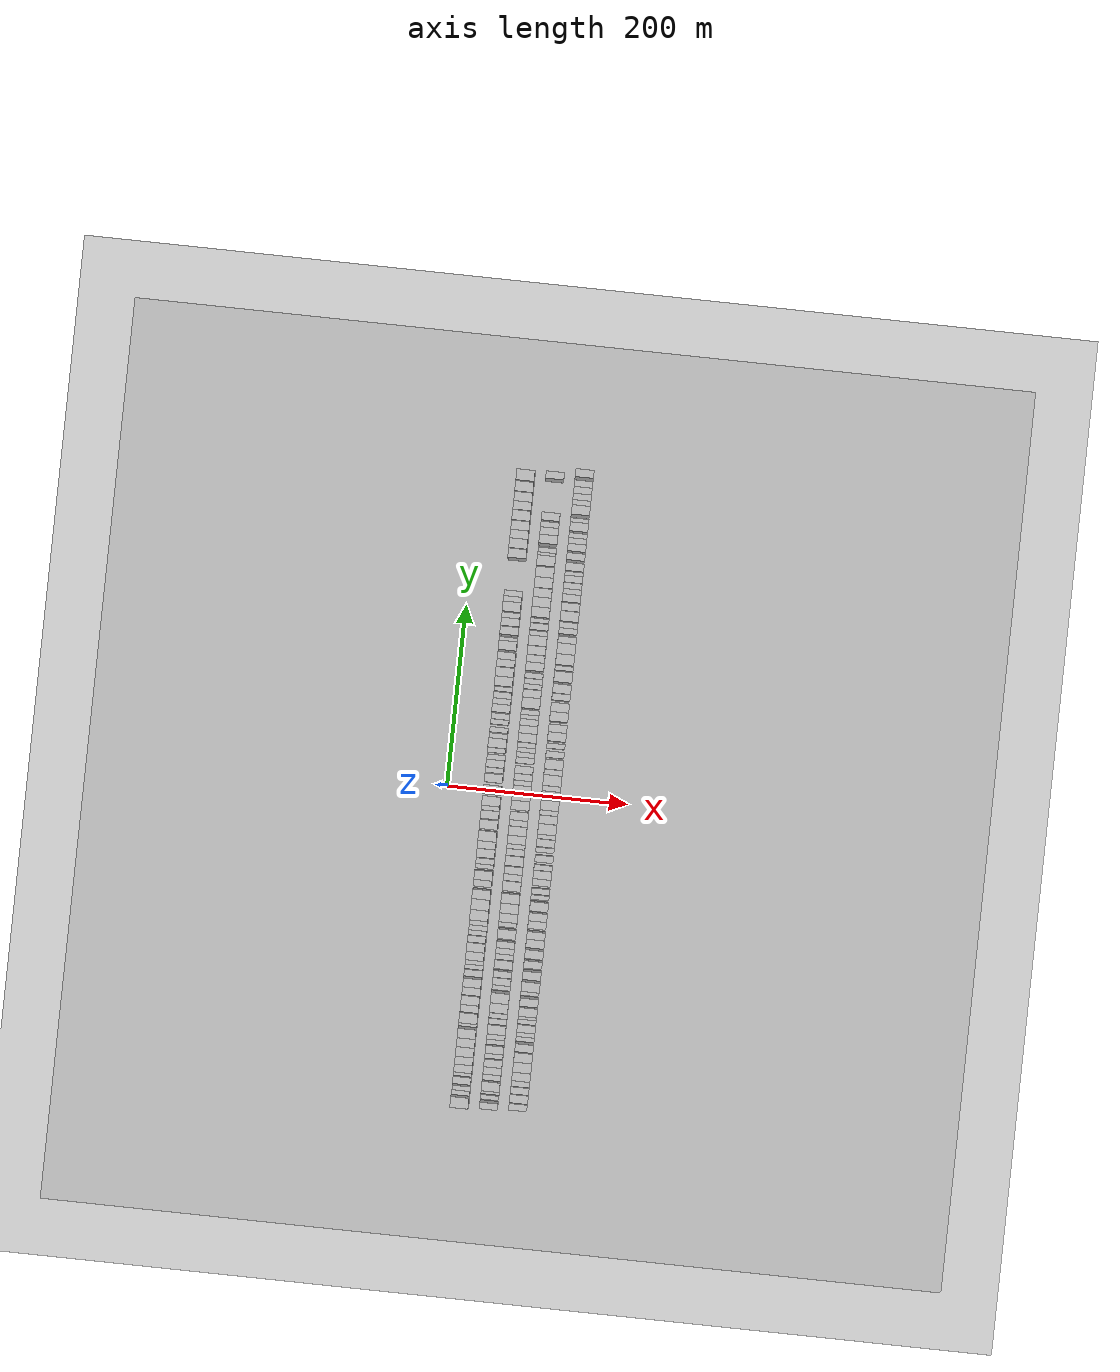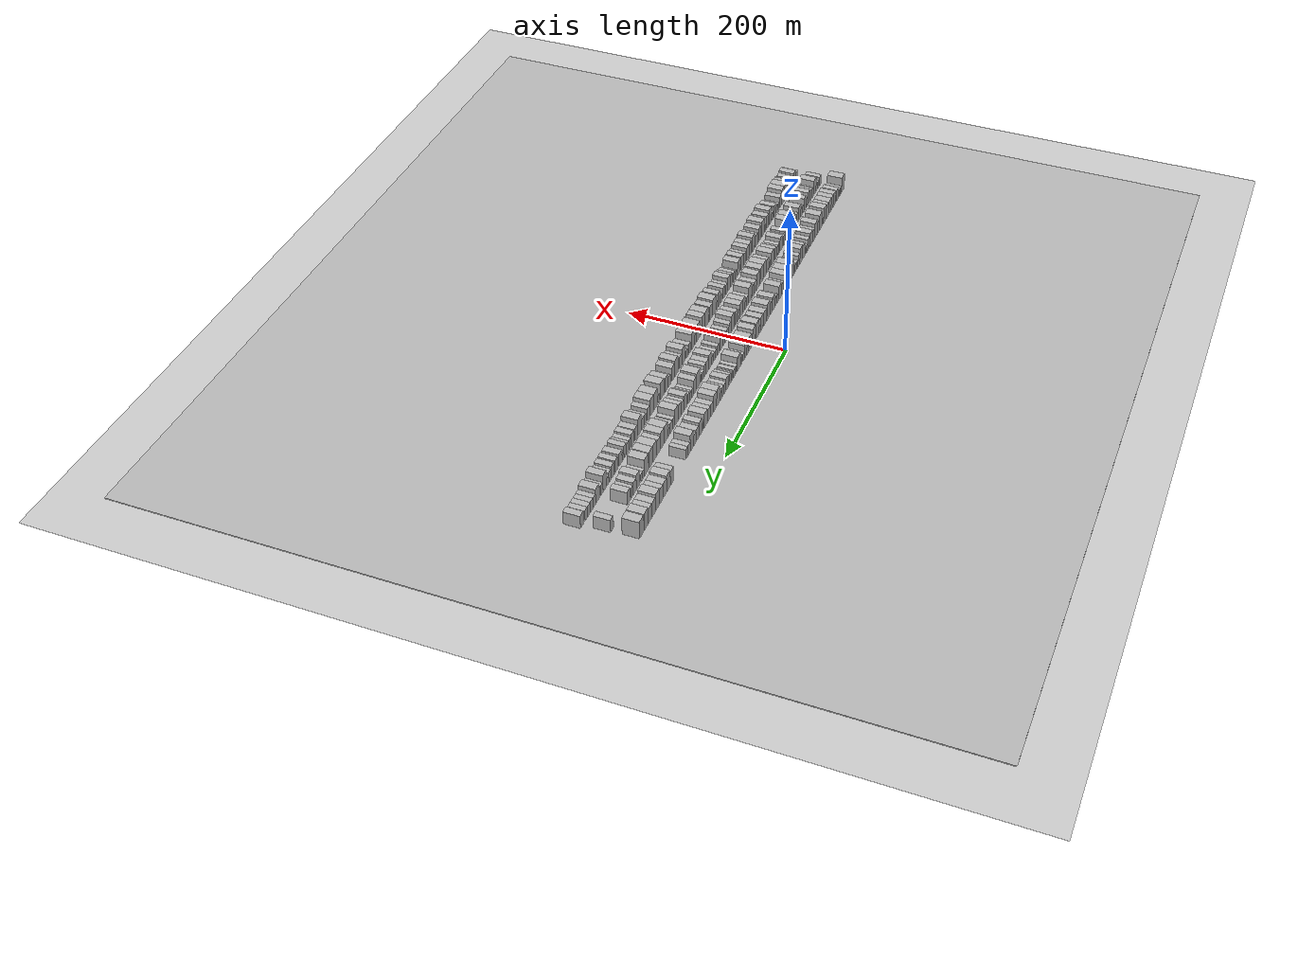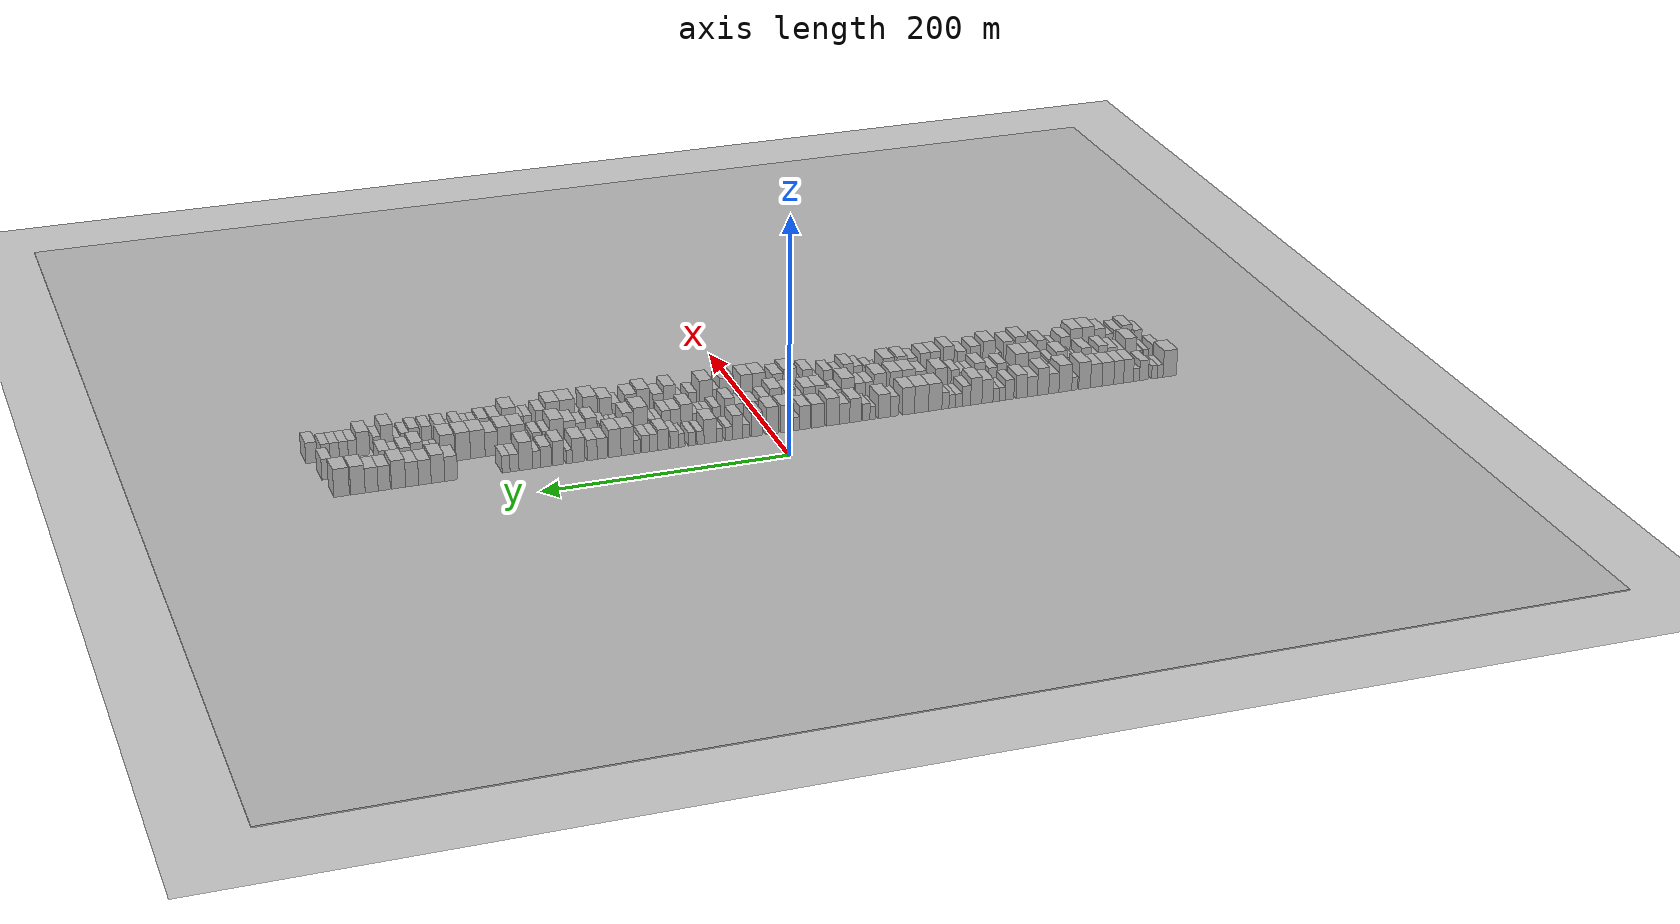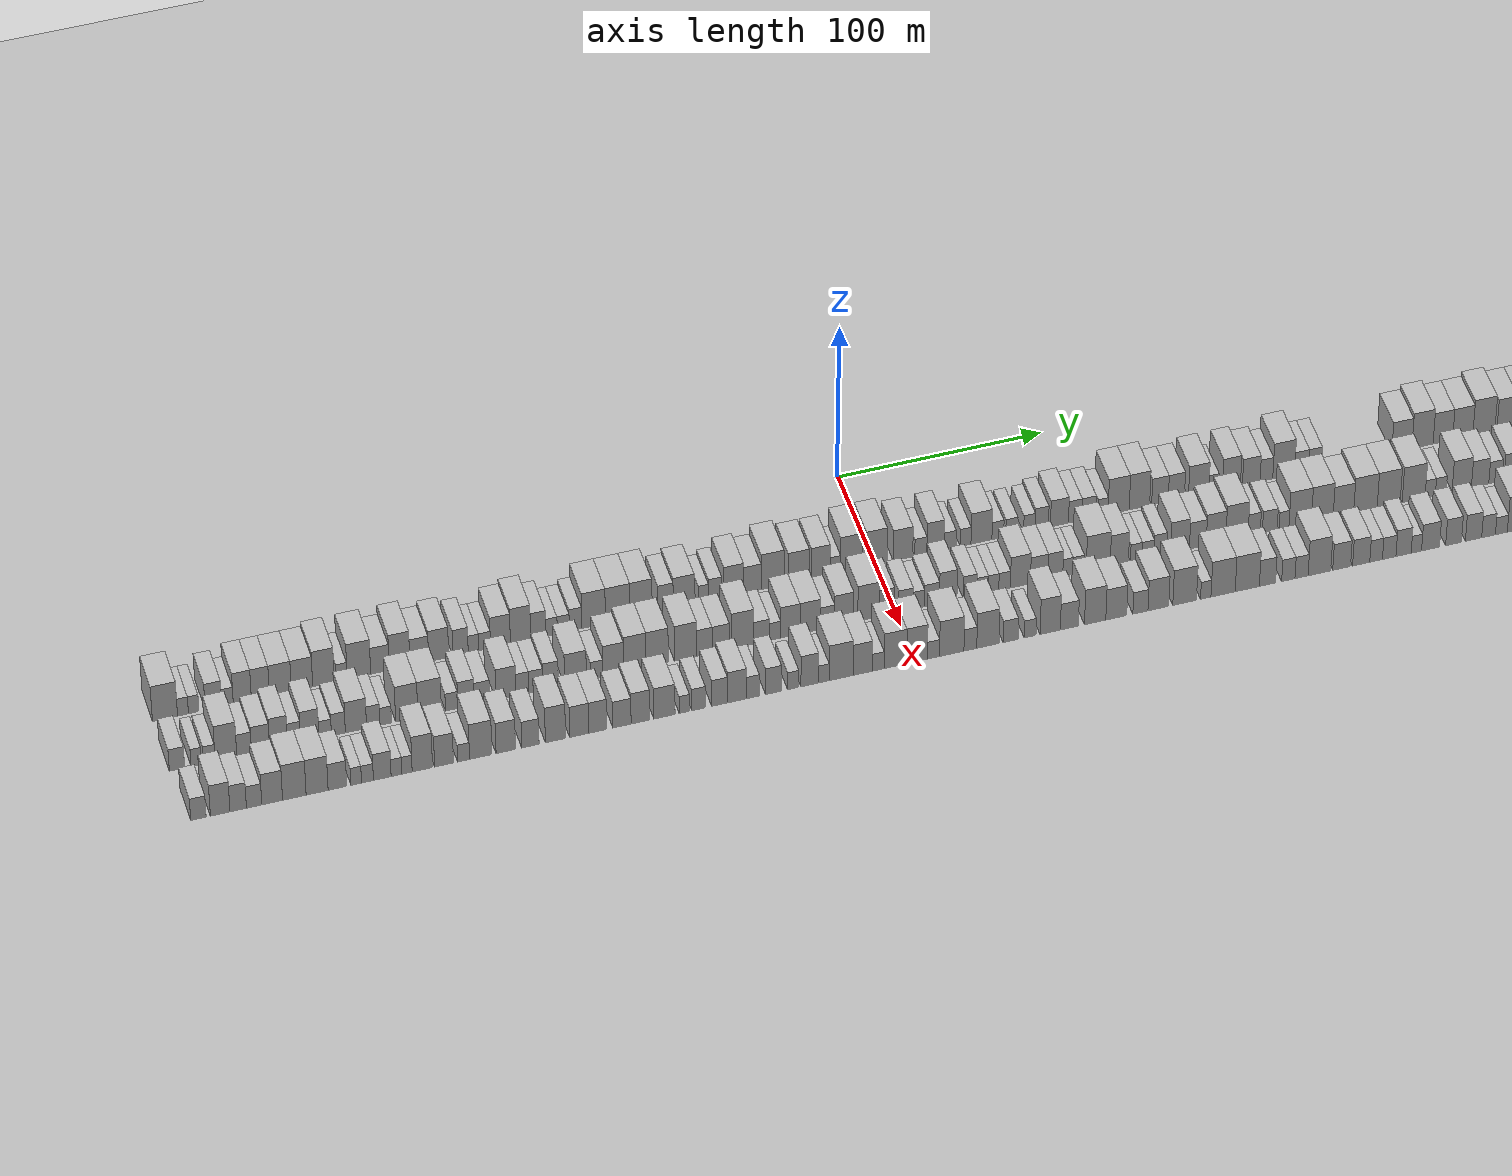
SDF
<?xml version="1.0" encoding="utf-8"?>

<sdf version="1.6">

   <world name="default">

      <gui fullscreen="0">

         <camera name="user_camera">

            <pose>-15 0 4.57585 0 0 0</pose>

            <view_controller>orbit</view_controller>

         </camera>

      </gui>

      <scene>

         <sky>

           <clouds>

             <speed>12</speed>

           </clouds>

         </sky>

         <ambient>0.4 0.4 0.4 1</ambient>

         <background>0.7 0.7 0.7 1</background>

         <shadows>1</shadows>

      </scene>

      <gravity>0 0 -9.8066</gravity>

      <magnetic_field>6e-06 2.3e-05 -4.2e-05</magnetic_field>

      <physics default="0" name="default_physics" type="ode">

         <ode>

            <solver>

               <type>quick</type>

               <iters>10</iters>

               <sor>1.0</sor>

               <use_dynamic_moi_rescaling>0</use_dynamic_moi_rescaling>

            </solver>

            <constraints>

               <cfm>0</cfm>

               <erp>0.2</erp>

               <contact_max_correcting_vel>100</contact_max_correcting_vel>

               <contact_surface_layer>0.001</contact_surface_layer>

            </constraints>

         </ode>

         <max_step_size>0.004</max_step_size>

         <real_time_factor>1</real_time_factor>

         <real_time_update_rate>250</real_time_update_rate>

      </physics>

      <light name="sun" type="directional">

         <cast_shadows>1</cast_shadows>

         <pose>0 0 10 0 0 0</pose>

         <diffuse>0.8 0.8 0.8 1</diffuse>

         <specular>0.2 0.2 0.2 1</specular>

         <attenuation>

            <range>1000</range>

            <constant>0.9</constant>

            <linear>0.01</linear>

            <quadratic>0.001</quadratic>

         </attenuation>

         <direction>-0.5 0.1 -0.9</direction>

      </light>

      <include>

         <name>ground_plane_1</name>

         <uri>model://HANNAS_ground_plane</uri>

         <pose>0 0 0  0 0 0</pose>

      </include>

      <include>

         <name>ground_plane_2</name>

         <uri>model://HANNAS_ground_plane</uri>

         <pose>100 0 0  0 0 0</pose>

      </include>

      <model name="building_1">

         <static>1</static>

         <pose frame="">50.0000 -342.0457 0 0.000000 0.000000 0.000000</pose>

         <link name="link">

            <pose frame="">0 0 12.00 0 0 0</pose>

            <collision name="collision">

               <geometry>

                  <box>

                     <size>20.0000 11.9086 24.0000</size>

                  </box>

               </geometry>

               <max_contacts>10</max_contacts>

               <surface>

                  <contact>

                     <ode/>

                  </contact>

                  <bounce/>

                  <friction>

                     <torsional>

                        <ode/>

                     </torsional>

                     <ode/>

                  </friction>

               </surface>

            </collision>

            <visual name="visual">

               <cast_shadows>0</cast_shadows>

               <geometry>

                  <box>

                     <size>20.0000 11.9086 24.0000</size>

                  </box>

               </geometry>

               <material>

                  <script>

                     <uri>model://HANNAS_wall/materials/scripts</uri>

                     <uri>model://HANNAS_wall/materials/textures</uri>

                     <name>vrc/HANNAS_wall</name>

                  </script>

               </material>

            </visual>

            <self_collide>0</self_collide>

            <enable_wind>0</enable_wind>

            <kinematic>0</kinematic>

         </link>

      </model>

      <model name="building_2">

         <static>1</static>

         <pose frame="">50.0000 -333.5086 0 0.000000 0.000000 0.000000</pose>

         <link name="link">

            <pose frame="">0 0 6.00 0 0 0</pose>

            <collision name="collision">

               <geometry>

                  <box>

                     <size>20.0000 5.1657 12.0000</size>

                  </box>

               </geometry>

               <max_contacts>10</max_contacts>

               <surface>

                  <contact>

                     <ode/>

                  </contact>

                  <bounce/>

                  <friction>

                     <torsional>

                        <ode/>

                     </torsional>

                     <ode/>

                  </friction>

               </surface>

            </collision>

            <visual name="visual">

               <cast_shadows>0</cast_shadows>

               <geometry>

                  <box>

                     <size>20.0000 5.1657 12.0000</size>

                  </box>

               </geometry>

               <material>

                  <script>

                     <uri>model://HANNAS_wall/materials/scripts</uri>

                     <uri>model://HANNAS_wall/materials/textures</uri>

                     <name>vrc/HANNAS_wall</name>

                  </script>

               </material>

            </visual>

            <self_collide>0</self_collide>

            <enable_wind>0</enable_wind>

            <kinematic>0</kinematic>

         </link>

      </model>

      <model name="building_3">

         <static>1</static>

         <pose frame="">50.0000 -328.4400 0 0.000000 0.000000 0.000000</pose>

         <link name="link">

            <pose frame="">0 0 6.00 0 0 0</pose>

            <collision name="collision">

               <geometry>

                  <box>

                     <size>20.0000 4.9714 12.0000</size>

                  </box>

               </geometry>

               <max_contacts>10</max_contacts>

               <surface>

                  <contact>

                     <ode/>

                  </contact>

                  <bounce/>

                  <friction>

                     <torsional>

                        <ode/>

                     </torsional>

                     <ode/>

                  </friction>

               </surface>

            </collision>

            <visual name="visual">

               <cast_shadows>0</cast_shadows>

               <geometry>

                  <box>

                     <size>20.0000 4.9714 12.0000</size>

                  </box>

               </geometry>

               <material>

                  <script>

                     <uri>model://HANNAS_wall/materials/scripts</uri>

                     <uri>model://HANNAS_wall/materials/textures</uri>

                     <name>vrc/HANNAS_wall</name>

                  </script>

               </material>

            </visual>

            <self_collide>0</self_collide>

            <enable_wind>0</enable_wind>

            <kinematic>0</kinematic>

         </link>

      </model>

      <model name="building_4">

         <static>1</static>

         <pose frame="">50.0000 -319.0133 0 0.000000 0.000000 0.000000</pose>

         <link name="link">

            <pose frame="">0 0 9.00 0 0 0</pose>

            <collision name="collision">

               <geometry>

                  <box>

                     <size>20.0000 7.8820 18.0000</size>

                  </box>

               </geometry>

               <max_contacts>10</max_contacts>

               <surface>

                  <contact>

                     <ode/>

                  </contact>

                  <bounce/>

                  <friction>

                     <torsional>

                        <ode/>

                     </torsional>

                     <ode/>

                  </friction>

               </surface>

            </collision>

            <visual name="visual">

               <cast_shadows>0</cast_shadows>

               <geometry>

                  <box>

                     <size>20.0000 7.8820 18.0000</size>

                  </box>

               </geometry>

               <material>

                  <script>

                     <uri>model://HANNAS_wall/materials/scripts</uri>

                     <uri>model://HANNAS_wall/materials/textures</uri>

                     <name>vrc/HANNAS_wall</name>

                  </script>

               </material>

            </visual>

            <self_collide>0</self_collide>

            <enable_wind>0</enable_wind>

            <kinematic>0</kinematic>

         </link>

      </model>

      <model name="building_5">

         <static>1</static>

         <pose frame="">50.0000 -312.3489 0 0.000000 0.000000 0.000000</pose>

         <link name="link">

            <pose frame="">0 0 6.00 0 0 0</pose>

            <collision name="collision">

               <geometry>

                  <box>

                     <size>20.0000 5.4469 12.0000</size>

                  </box>

               </geometry>

               <max_contacts>10</max_contacts>

               <surface>

                  <contact>

                     <ode/>

                  </contact>

                  <bounce/>

                  <friction>

                     <torsional>

                        <ode/>

                     </torsional>

                     <ode/>

                  </friction>

               </surface>

            </collision>

            <visual name="visual">

               <cast_shadows>0</cast_shadows>

               <geometry>

                  <box>

                     <size>20.0000 5.4469 12.0000</size>

                  </box>

               </geometry>

               <material>

                  <script>

                     <uri>model://HANNAS_wall/materials/scripts</uri>

                     <uri>model://HANNAS_wall/materials/textures</uri>

                     <name>vrc/HANNAS_wall</name>

                  </script>

               </material>

            </visual>

            <self_collide>0</self_collide>

            <enable_wind>0</enable_wind>

            <kinematic>0</kinematic>

         </link>

      </model>

      <model name="building_6">

         <static>1</static>

         <pose frame="">50.0000 -305.3142 0 0.000000 0.000000 0.000000</pose>

         <link name="link">

            <pose frame="">0 0 10.50 0 0 0</pose>

            <collision name="collision">

               <geometry>

                  <box>

                     <size>20.0000 8.6225 21.0000</size>

                  </box>

               </geometry>

               <max_contacts>10</max_contacts>

               <surface>

                  <contact>

                     <ode/>

                  </contact>

                  <bounce/>

                  <friction>

                     <torsional>

                        <ode/>

                     </torsional>

                     <ode/>

                  </friction>

               </surface>

            </collision>

            <visual name="visual">

               <cast_shadows>0</cast_shadows>

               <geometry>

                  <box>

                     <size>20.0000 8.6225 21.0000</size>

                  </box>

               </geometry>

               <material>

                  <script>

                     <uri>model://HANNAS_wall/materials/scripts</uri>

                     <uri>model://HANNAS_wall/materials/textures</uri>

                     <name>vrc/HANNAS_wall</name>

                  </script>

               </material>

            </visual>

            <self_collide>0</self_collide>

            <enable_wind>0</enable_wind>

            <kinematic>0</kinematic>

         </link>

      </model>

      <model name="building_7">

         <static>1</static>

         <pose frame="">50.0000 -296.7071 0 0.000000 0.000000 0.000000</pose>

         <link name="link">

            <pose frame="">0 0 10.50 0 0 0</pose>

            <collision name="collision">

               <geometry>

                  <box>

                     <size>20.0000 8.5917 21.0000</size>

                  </box>

               </geometry>

               <max_contacts>10</max_contacts>

               <surface>

                  <contact>

                     <ode/>

                  </contact>

                  <bounce/>

                  <friction>

                     <torsional>

                        <ode/>

                     </torsional>

                     <ode/>

                  </friction>

               </surface>

            </collision>

            <visual name="visual">

               <cast_shadows>0</cast_shadows>

               <geometry>

                  <box>

                     <size>20.0000 8.5917 21.0000</size>

                  </box>

               </geometry>

               <material>

                  <script>

                     <uri>model://HANNAS_wall/materials/scripts</uri>

                     <uri>model://HANNAS_wall/materials/textures</uri>

                     <name>vrc/HANNAS_wall</name>

                  </script>

               </material>

            </visual>

            <self_collide>0</self_collide>

            <enable_wind>0</enable_wind>

            <kinematic>0</kinematic>

         </link>

      </model>

      <model name="building_8">

         <static>1</static>

         <pose frame="">50.0000 -287.1837 0 0.000000 0.000000 0.000000</pose>

         <link name="link">

            <pose frame="">0 0 10.50 0 0 0</pose>

            <collision name="collision">

               <geometry>

                  <box>

                     <size>20.0000 10.4551 21.0000</size>

                  </box>

               </geometry>

               <max_contacts>10</max_contacts>

               <surface>

                  <contact>

                     <ode/>

                  </contact>

                  <bounce/>

                  <friction>

                     <torsional>

                        <ode/>

                     </torsional>

                     <ode/>

                  </friction>

               </surface>

            </collision>

            <visual name="visual">

               <cast_shadows>0</cast_shadows>

               <geometry>

                  <box>

                     <size>20.0000 10.4551 21.0000</size>

                  </box>

               </geometry>

               <material>

                  <script>

                     <uri>model://HANNAS_wall/materials/scripts</uri>

                     <uri>model://HANNAS_wall/materials/textures</uri>

                     <name>vrc/HANNAS_wall</name>

                  </script>

               </material>

            </visual>

            <self_collide>0</self_collide>

            <enable_wind>0</enable_wind>

            <kinematic>0</kinematic>

         </link>

      </model>

      <model name="building_9">

         <static>1</static>

         <pose frame="">50.0000 -276.8616 0 0.000000 0.000000 0.000000</pose>

         <link name="link">

            <pose frame="">0 0 10.50 0 0 0</pose>

            <collision name="collision">

               <geometry>

                  <box>

                     <size>20.0000 10.1892 21.0000</size>

                  </box>

               </geometry>

               <max_contacts>10</max_contacts>

               <surface>

                  <contact>

                     <ode/>

                  </contact>

                  <bounce/>

                  <friction>

                     <torsional>

                        <ode/>

                     </torsional>

                     <ode/>

                  </friction>

               </surface>

            </collision>

            <visual name="visual">

               <cast_shadows>0</cast_shadows>

               <geometry>

                  <box>

                     <size>20.0000 10.1892 21.0000</size>

                  </box>

               </geometry>

               <material>

                  <script>

                     <uri>model://HANNAS_wall/materials/scripts</uri>

                     <uri>model://HANNAS_wall/materials/textures</uri>

                     <name>vrc/HANNAS_wall</name>

                  </script>

               </material>

            </visual>

            <self_collide>0</self_collide>

            <enable_wind>0</enable_wind>

            <kinematic>0</kinematic>

         </link>

      </model>

      <model name="building_10">

         <static>1</static>

         <pose frame="">50.0000 -266.6103 0 0.000000 0.000000 0.000000</pose>

         <link name="link">

            <pose frame="">0 0 12.00 0 0 0</pose>

            <collision name="collision">

               <geometry>

                  <box>

                     <size>20.0000 10.3135 24.0000</size>

                  </box>

               </geometry>

               <max_contacts>10</max_contacts>

               <surface>

                  <contact>

                     <ode/>

                  </contact>

                  <bounce/>

                  <friction>

                     <torsional>

                        <ode/>

                     </torsional>

                     <ode/>

                  </friction>

               </surface>

            </collision>

            <visual name="visual">

               <cast_shadows>0</cast_shadows>

               <geometry>

                  <box>

                     <size>20.0000 10.3135 24.0000</size>

                  </box>

               </geometry>

               <material>

                  <script>

                     <uri>model://HANNAS_wall/materials/scripts</uri>

                     <uri>model://HANNAS_wall/materials/textures</uri>

                     <name>vrc/HANNAS_wall</name>

                  </script>

               </material>

            </visual>

            <self_collide>0</self_collide>

            <enable_wind>0</enable_wind>

            <kinematic>0</kinematic>

         </link>

      </model>

      <model name="building_11">

         <static>1</static>

         <pose frame="">50.0000 -257.8836 0 0.000000 0.000000 0.000000</pose>

         <link name="link">

            <pose frame="">0 0 6.00 0 0 0</pose>

            <collision name="collision">

               <geometry>

                  <box>

                     <size>20.0000 5.1400 12.0000</size>

                  </box>

               </geometry>

               <max_contacts>10</max_contacts>

               <surface>

                  <contact>

                     <ode/>

                  </contact>

                  <bounce/>

                  <friction>

                     <torsional>

                        <ode/>

                     </torsional>

                     <ode/>

                  </friction>

               </surface>

            </collision>

            <visual name="visual">

               <cast_shadows>0</cast_shadows>

               <geometry>

                  <box>

                     <size>20.0000 5.1400 12.0000</size>

                  </box>

               </geometry>

               <material>

                  <script>

                     <uri>model://HANNAS_wall/materials/scripts</uri>

                     <uri>model://HANNAS_wall/materials/textures</uri>

                     <name>vrc/HANNAS_wall</name>

                  </script>

               </material>

            </visual>

            <self_collide>0</self_collide>

            <enable_wind>0</enable_wind>

            <kinematic>0</kinematic>

         </link>

      </model>

      <model name="building_12">

         <static>1</static>

         <pose frame="">50.0000 -249.6979 0 0.000000 0.000000 0.000000</pose>

         <link name="link">

            <pose frame="">0 0 12.00 0 0 0</pose>

            <collision name="collision">

               <geometry>

                  <box>

                     <size>20.0000 11.2315 24.0000</size>

                  </box>

               </geometry>

               <max_contacts>10</max_contacts>

               <surface>

                  <contact>

                     <ode/>

                  </contact>

                  <bounce/>

                  <friction>

                     <torsional>

                        <ode/>

                     </torsional>

                     <ode/>

                  </friction>

               </surface>

            </collision>

            <visual name="visual">

               <cast_shadows>0</cast_shadows>

               <geometry>

                  <box>

                     <size>20.0000 11.2315 24.0000</size>

                  </box>

               </geometry>

               <material>

                  <script>

                     <uri>model://HANNAS_wall/materials/scripts</uri>

                     <uri>model://HANNAS_wall/materials/textures</uri>

                     <name>vrc/HANNAS_wall</name>

                  </script>

               </material>

            </visual>

            <self_collide>0</self_collide>

            <enable_wind>0</enable_wind>

            <kinematic>0</kinematic>

         </link>

      </model>

      <model name="building_13">

         <static>1</static>

         <pose frame="">50.0000 -239.6436 0 0.000000 0.000000 0.000000</pose>

         <link name="link">

            <pose frame="">0 0 9.00 0 0 0</pose>

            <collision name="collision">

               <geometry>

                  <box>

                     <size>20.0000 8.8770 18.0000</size>

                  </box>

               </geometry>

               <max_contacts>10</max_contacts>

               <surface>

                  <contact>

                     <ode/>

                  </contact>

                  <bounce/>

                  <friction>

                     <torsional>

                        <ode/>

                     </torsional>

                     <ode/>

                  </friction>

               </surface>

            </collision>

            <visual name="visual">

               <cast_shadows>0</cast_shadows>

               <geometry>

                  <box>

                     <size>20.0000 8.8770 18.0000</size>

                  </box>

               </geometry>

               <material>

                  <script>

                     <uri>model://HANNAS_wall/materials/scripts</uri>

                     <uri>model://HANNAS_wall/materials/textures</uri>

                     <name>vrc/HANNAS_wall</name>

                  </script>

               </material>

            </visual>

            <self_collide>0</self_collide>

            <enable_wind>0</enable_wind>

            <kinematic>0</kinematic>

         </link>

      </model>

      <model name="building_14">

         <static>1</static>

         <pose frame="">50.0000 -230.2538 0 0.000000 0.000000 0.000000</pose>

         <link name="link">

            <pose frame="">0 0 12.00 0 0 0</pose>

            <collision name="collision">

               <geometry>

                  <box>

                     <size>20.0000 9.9026 24.0000</size>

                  </box>

               </geometry>

               <max_contacts>10</max_contacts>

               <surface>

                  <contact>

                     <ode/>

                  </contact>

                  <bounce/>

                  <friction>

                     <torsional>

                        <ode/>

                     </torsional>

                     <ode/>

                  </friction>

               </surface>

            </collision>

            <visual name="visual">

               <cast_shadows>0</cast_shadows>

               <geometry>

                  <box>

                     <size>20.0000 9.9026 24.0000</size>

                  </box>

               </geometry>

               <material>

                  <script>

                     <uri>model://HANNAS_wall/materials/scripts</uri>

                     <uri>model://HANNAS_wall/materials/textures</uri>

                     <name>vrc/HANNAS_wall</name>

                  </script>

               </material>

            </visual>

            <self_collide>0</self_collide>

            <enable_wind>0</enable_wind>

            <kinematic>0</kinematic>

         </link>

      </model>

      <model name="building_15">

         <static>1</static>

         <pose frame="">50.0000 -220.8089 0 0.000000 0.000000 0.000000</pose>

         <link name="link">

            <pose frame="">0 0 9.00 0 0 0</pose>

            <collision name="collision">

               <geometry>

                  <box>

                     <size>20.0000 8.9873 18.0000</size>

                  </box>

               </geometry>

               <max_contacts>10</max_contacts>

               <surface>

                  <contact>

                     <ode/>

                  </contact>

                  <bounce/>

                  <friction>

                     <torsional>

                        <ode/>

                     </torsional>

                     <ode/>

                  </friction>

               </surface>

            </collision>

            <visual name="visual">

               <cast_shadows>0</cast_shadows>

               <geometry>

                  <box>

                     <size>20.0000 8.9873 18.0000</size>

                  </box>

               </geometry>

               <material>

                  <script>

                     <uri>model://HANNAS_wall/materials/scripts</uri>

                     <uri>model://HANNAS_wall/materials/textures</uri>

                     <name>vrc/HANNAS_wall</name>

                  </script>

               </material>

            </visual>

            <self_collide>0</self_collide>

            <enable_wind>0</enable_wind>

            <kinematic>0</kinematic>

         </link>

      </model>

      <model name="building_16">

         <static>1</static>

         <pose frame="">50.0000 -211.5176 0 0.000000 0.000000 0.000000</pose>

         <link name="link">

            <pose frame="">0 0 10.50 0 0 0</pose>

            <collision name="collision">

               <geometry>

                  <box>

                     <size>20.0000 9.5953 21.0000</size>

                  </box>

               </geometry>

               <max_contacts>10</max_contacts>

               <surface>

                  <contact>

                     <ode/>

                  </contact>

                  <bounce/>

                  <friction>

                     <torsional>

                        <ode/>

                     </torsional>

                     <ode/>

                  </friction>

               </surface>

            </collision>

            <visual name="visual">

               <cast_shadows>0</cast_shadows>

               <geometry>

                  <box>

                     <size>20.0000 9.5953 21.0000</size>

                  </box>

               </geometry>

               <material>

                  <script>

                     <uri>model://HANNAS_wall/materials/scripts</uri>

                     <uri>model://HANNAS_wall/materials/textures</uri>

                     <name>vrc/HANNAS_wall</name>

                  </script>

               </material>

            </visual>

            <self_collide>0</self_collide>

            <enable_wind>0</enable_wind>

            <kinematic>0</kinematic>

         </link>

      </model>

      <model name="building_17">

         <static>1</static>

         <pose frame="">50.0000 -201.0342 0 0.000000 0.000000 0.000000</pose>

         <link name="link">

            <pose frame="">0 0 9.00 0 0 0</pose>

            <collision name="collision">

               <geometry>

                  <box>

                     <size>20.0000 7.3714 18.0000</size>

                  </box>

               </geometry>

               <max_contacts>10</max_contacts>

               <surface>

                  <contact>

                     <ode/>

                  </contact>

                  <bounce/>

                  <friction>

                     <torsional>

                        <ode/>

                     </torsional>

                     <ode/>

                  </friction>

               </surface>

            </collision>

            <visual name="visual">

               <cast_shadows>0</cast_shadows>

               <geometry>

                  <box>

                     <size>20.0000 7.3714 18.0000</size>

                  </box>

               </geometry>

               <material>

                  <script>

                     <uri>model://HANNAS_wall/materials/scripts</uri>

                     <uri>model://HANNAS_wall/materials/textures</uri>

                     <name>vrc/HANNAS_wall</name>

                  </script>

               </material>

            </visual>

            <self_collide>0</self_collide>

            <enable_wind>0</enable_wind>

            <kinematic>0</kinematic>

         </link>

      </model>

      <model name="building_18">

         <static>1</static>

         <pose frame="">50.0000 -194.8207 0 0.000000 0.000000 0.000000</pose>

         <link name="link">

            <pose frame="">0 0 6.00 0 0 0</pose>

            <collision name="collision">

               <geometry>

                  <box>

                     <size>20.0000 5.0557 12.0000</size>

                  </box>

               </geometry>

               <max_contacts>10</max_contacts>

               <surface>

                  <contact>

                     <ode/>

                  </contact>

                  <bounce/>

                  <friction>

                     <torsional>

                        <ode/>

                     </torsional>

                     <ode/>

                  </friction>

               </surface>

            </collision>

            <visual name="visual">

               <cast_shadows>0</cast_shadows>

               <geometry>

                  <box>

                     <size>20.0000 5.0557 12.0000</size>

                  </box>

               </geometry>

               <material>

                  <script>

                     <uri>model://HANNAS_wall/materials/scripts</uri>

                     <uri>model://HANNAS_wall/materials/textures</uri>

                     <name>vrc/HANNAS_wall</name>

                  </script>

               </material>

            </visual>

            <self_collide>0</self_collide>

            <enable_wind>0</enable_wind>

            <kinematic>0</kinematic>

         </link>

      </model>

      <model name="building_19">

         <static>1</static>

         <pose frame="">50.0000 -189.4772 0 0.000000 0.000000 0.000000</pose>

         <link name="link">

            <pose frame="">0 0 6.00 0 0 0</pose>

            <collision name="collision">

               <geometry>

                  <box>

                     <size>20.0000 5.6313 12.0000</size>

                  </box>

               </geometry>

               <max_contacts>10</max_contacts>

               <surface>

                  <contact>

                     <ode/>

                  </contact>

                  <bounce/>

                  <friction>

                     <torsional>

                        <ode/>

                     </torsional>

                     <ode/>

                  </friction>

               </surface>

            </collision>

            <visual name="visual">

               <cast_shadows>0</cast_shadows>

               <geometry>

                  <box>

                     <size>20.0000 5.6313 12.0000</size>

                  </box>

               </geometry>

               <material>

                  <script>

                     <uri>model://HANNAS_wall/materials/scripts</uri>

                     <uri>model://HANNAS_wall/materials/textures</uri>

                     <name>vrc/HANNAS_wall</name>

                  </script>

               </material>

            </visual>

            <self_collide>0</self_collide>

            <enable_wind>0</enable_wind>

            <kinematic>0</kinematic>

         </link>

      </model>

      <model name="building_20">

         <static>1</static>

         <pose frame="">50.0000 -181.8742 0 0.000000 0.000000 0.000000</pose>

         <link name="link">

            <pose frame="">0 0 10.50 0 0 0</pose>

            <collision name="collision">

               <geometry>

                  <box>

                     <size>20.0000 9.5747 21.0000</size>

                  </box>

               </geometry>

               <max_contacts>10</max_contacts>

               <surface>

                  <contact>

                     <ode/>

                  </contact>

                  <bounce/>

                  <friction>

                     <torsional>

                        <ode/>

                     </torsional>

                     <ode/>

                  </friction>

               </surface>

            </collision>

            <visual name="visual">

               <cast_shadows>0</cast_shadows>

               <geometry>

                  <box>

                     <size>20.0000 9.5747 21.0000</size>

                  </box>

               </geometry>

               <material>

                  <script>

                     <uri>model://HANNAS_wall/materials/scripts</uri>

                     <uri>model://HANNAS_wall/materials/textures</uri>

                     <name>vrc/HANNAS_wall</name>

                  </script>

               </material>

            </visual>

            <self_collide>0</self_collide>

            <enable_wind>0</enable_wind>

            <kinematic>0</kinematic>

         </link>

      </model>

      <model name="building_21">

         <static>1</static>

         <pose frame="">50.0000 -172.2154 0 0.000000 0.000000 0.000000</pose>

         <link name="link">

            <pose frame="">0 0 12.00 0 0 0</pose>

            <collision name="collision">

               <geometry>

                  <box>

                     <size>20.0000 9.7429 24.0000</size>

                  </box>

               </geometry>

               <max_contacts>10</max_contacts>

               <surface>

                  <contact>

                     <ode/>

                  </contact>

                  <bounce/>

                  <friction>

                     <torsional>

                        <ode/>

                     </torsional>

                     <ode/>

                  </friction>

               </surface>

            </collision>

            <visual name="visual">

               <cast_shadows>0</cast_shadows>

               <geometry>

                  <box>

                     <size>20.0000 9.7429 24.0000</size>

                  </box>

               </geometry>

               <material>

                  <script>

                     <uri>model://HANNAS_wall/materials/scripts</uri>

                     <uri>model://HANNAS_wall/materials/textures</uri>

                     <name>vrc/HANNAS_wall</name>

                  </script>

               </material>

            </visual>

            <self_collide>0</self_collide>

            <enable_wind>0</enable_wind>

            <kinematic>0</kinematic>

         </link>

      </model>

      <model name="building_22">

         <static>1</static>

         <pose frame="">50.0000 -163.6782 0 0.000000 0.000000 0.000000</pose>

         <link name="link">

            <pose frame="">0 0 9.00 0 0 0</pose>

            <collision name="collision">

               <geometry>

                  <box>

                     <size>20.0000 7.3314 18.0000</size>

                  </box>

               </geometry>

               <max_contacts>10</max_contacts>

               <surface>

                  <contact>

                     <ode/>

                  </contact>

                  <bounce/>

                  <friction>

                     <torsional>

                        <ode/>

                     </torsional>

                     <ode/>

                  </friction>

               </surface>

            </collision>

            <visual name="visual">

               <cast_shadows>0</cast_shadows>

               <geometry>

                  <box>

                     <size>20.0000 7.3314 18.0000</size>

                  </box>

               </geometry>

               <material>

                  <script>

                     <uri>model://HANNAS_wall/materials/scripts</uri>

                     <uri>model://HANNAS_wall/materials/textures</uri>

                     <name>vrc/HANNAS_wall</name>

                  </script>

               </material>

            </visual>

            <self_collide>0</self_collide>

            <enable_wind>0</enable_wind>

            <kinematic>0</kinematic>

         </link>

      </model>

      <model name="building_23">

         <static>1</static>

         <pose frame="">50.0000 -157.2608 0 0.000000 0.000000 0.000000</pose>

         <link name="link">

            <pose frame="">0 0 6.00 0 0 0</pose>

            <collision name="collision">

               <geometry>

                  <box>

                     <size>20.0000 5.5035 12.0000</size>

                  </box>

               </geometry>

               <max_contacts>10</max_contacts>

               <surface>

                  <contact>

                     <ode/>

                  </contact>

                  <bounce/>

                  <friction>

                     <torsional>

                        <ode/>

                     </torsional>

                     <ode/>

                  </friction>

               </surface>

            </collision>

            <visual name="visual">

               <cast_shadows>0</cast_shadows>

               <geometry>

                  <box>

                     <size>20.0000 5.5035 12.0000</size>

                  </box>

               </geometry>

               <material>

                  <script>

                     <uri>model://HANNAS_wall/materials/scripts</uri>

                     <uri>model://HANNAS_wall/materials/textures</uri>

                     <name>vrc/HANNAS_wall</name>

                  </script>

               </material>

            </visual>

            <self_collide>0</self_collide>

            <enable_wind>0</enable_wind>

            <kinematic>0</kinematic>

         </link>

      </model>

      <model name="building_24">

         <static>1</static>

         <pose frame="">50.0000 -151.6057 0 0.000000 0.000000 0.000000</pose>

         <link name="link">

            <pose frame="">0 0 6.00 0 0 0</pose>

            <collision name="collision">

               <geometry>

                  <box>

                     <size>20.0000 5.8067 12.0000</size>

                  </box>

               </geometry>

               <max_contacts>10</max_contacts>

               <surface>

                  <contact>

                     <ode/>

                  </contact>

                  <bounce/>

                  <friction>

                     <torsional>

                        <ode/>

                     </torsional>

                     <ode/>

                  </friction>

               </surface>

            </collision>

            <visual name="visual">

               <cast_shadows>0</cast_shadows>

               <geometry>

                  <box>

                     <size>20.0000 5.8067 12.0000</size>

                  </box>

               </geometry>

               <material>

                  <script>

                     <uri>model://HANNAS_wall/materials/scripts</uri>

                     <uri>model://HANNAS_wall/materials/textures</uri>

                     <name>vrc/HANNAS_wall</name>

                  </script>

               </material>

            </visual>

            <self_collide>0</self_collide>

            <enable_wind>0</enable_wind>

            <kinematic>0</kinematic>

         </link>

      </model>

      <model name="building_25">

         <static>1</static>

         <pose frame="">50.0000 -145.6941 0 0.000000 0.000000 0.000000</pose>

         <link name="link">

            <pose frame="">0 0 7.50 0 0 0</pose>

            <collision name="collision">

               <geometry>

                  <box>

                     <size>20.0000 6.0165 15.0000</size>

                  </box>

               </geometry>

               <max_contacts>10</max_contacts>

               <surface>

                  <contact>

                     <ode/>

                  </contact>

                  <bounce/>

                  <friction>

                     <torsional>

                        <ode/>

                     </torsional>

                     <ode/>

                  </friction>

               </surface>

            </collision>

            <visual name="visual">

               <cast_shadows>0</cast_shadows>

               <geometry>

                  <box>

                     <size>20.0000 6.0165 15.0000</size>

                  </box>

               </geometry>

               <material>

                  <script>

                     <uri>model://HANNAS_wall/materials/scripts</uri>

                     <uri>model://HANNAS_wall/materials/textures</uri>

                     <name>vrc/HANNAS_wall</name>

                  </script>

               </material>

            </visual>

            <self_collide>0</self_collide>

            <enable_wind>0</enable_wind>

            <kinematic>0</kinematic>

         </link>

      </model>

      <model name="building_26">

         <static>1</static>

         <pose frame="">50.0000 -136.9792 0 0.000000 0.000000 0.000000</pose>

         <link name="link">

            <pose frame="">0 0 12.00 0 0 0</pose>

            <collision name="collision">

               <geometry>

                  <box>

                     <size>20.0000 11.4132 24.0000</size>

                  </box>

               </geometry>

               <max_contacts>10</max_contacts>

               <surface>

                  <contact>

                     <ode/>

                  </contact>

                  <bounce/>

                  <friction>

                     <torsional>

                        <ode/>

                     </torsional>

                     <ode/>

                  </friction>

               </surface>

            </collision>

            <visual name="visual">

               <cast_shadows>0</cast_shadows>

               <geometry>

                  <box>

                     <size>20.0000 11.4132 24.0000</size>

                  </box>

               </geometry>

               <material>

                  <script>

                     <uri>model://HANNAS_wall/materials/scripts</uri>

                     <uri>model://HANNAS_wall/materials/textures</uri>

                     <name>vrc/HANNAS_wall</name>

                  </script>

               </material>

            </visual>

            <self_collide>0</self_collide>

            <enable_wind>0</enable_wind>

            <kinematic>0</kinematic>

         </link>

      </model>

      <model name="building_27">

         <static>1</static>

         <pose frame="">50.0000 -125.3124 0 0.000000 0.000000 0.000000</pose>

         <link name="link">

            <pose frame="">0 0 12.00 0 0 0</pose>

            <collision name="collision">

               <geometry>

                  <box>

                     <size>20.0000 11.9204 24.0000</size>

                  </box>

               </geometry>

               <max_contacts>10</max_contacts>

               <surface>

                  <contact>

                     <ode/>

                  </contact>

                  <bounce/>

                  <friction>

                     <torsional>

                        <ode/>

                     </torsional>

                     <ode/>

                  </friction>

               </surface>

            </collision>

            <visual name="visual">

               <cast_shadows>0</cast_shadows>

               <geometry>

                  <box>

                     <size>20.0000 11.9204 24.0000</size>

                  </box>

               </geometry>

               <material>

                  <script>

                     <uri>model://HANNAS_wall/materials/scripts</uri>

                     <uri>model://HANNAS_wall/materials/textures</uri>

                     <name>vrc/HANNAS_wall</name>

                  </script>

               </material>

            </visual>

            <self_collide>0</self_collide>

            <enable_wind>0</enable_wind>

            <kinematic>0</kinematic>

         </link>

      </model>

      <model name="building_28">

         <static>1</static>

         <pose frame="">50.0000 -114.1023 0 0.000000 0.000000 0.000000</pose>

         <link name="link">

            <pose frame="">0 0 12.00 0 0 0</pose>

            <collision name="collision">

               <geometry>

                  <box>

                     <size>20.0000 10.4998 24.0000</size>

                  </box>

               </geometry>

               <max_contacts>10</max_contacts>

               <surface>

                  <contact>

                     <ode/>

                  </contact>

                  <bounce/>

                  <friction>

                     <torsional>

                        <ode/>

                     </torsional>

                     <ode/>

                  </friction>

               </surface>

            </collision>

            <visual name="visual">

               <cast_shadows>0</cast_shadows>

               <geometry>

                  <box>

                     <size>20.0000 10.4998 24.0000</size>

                  </box>

               </geometry>

               <material>

                  <script>

                     <uri>model://HANNAS_wall/materials/scripts</uri>

                     <uri>model://HANNAS_wall/materials/textures</uri>

                     <name>vrc/HANNAS_wall</name>

                  </script>

               </material>

            </visual>

            <self_collide>0</self_collide>

            <enable_wind>0</enable_wind>

            <kinematic>0</kinematic>

         </link>

      </model>

      <model name="building_29">

         <static>1</static>

         <pose frame="">50.0000 -102.1703 0 0.000000 0.000000 0.000000</pose>

         <link name="link">

            <pose frame="">0 0 9.00 0 0 0</pose>

            <collision name="collision">

               <geometry>

                  <box>

                     <size>20.0000 7.3641 18.0000</size>

                  </box>

               </geometry>

               <max_contacts>10</max_contacts>

               <surface>

                  <contact>

                     <ode/>

                  </contact>

                  <bounce/>

                  <friction>

                     <torsional>

                        <ode/>

                     </torsional>

                     <ode/>

                  </friction>

               </surface>

            </collision>

            <visual name="visual">

               <cast_shadows>0</cast_shadows>

               <geometry>

                  <box>

                     <size>20.0000 7.3641 18.0000</size>

                  </box>

               </geometry>

               <material>

                  <script>

                     <uri>model://HANNAS_wall/materials/scripts</uri>

                     <uri>model://HANNAS_wall/materials/textures</uri>

                     <name>vrc/HANNAS_wall</name>

                  </script>

               </material>

            </visual>

            <self_collide>0</self_collide>

            <enable_wind>0</enable_wind>

            <kinematic>0</kinematic>

         </link>

      </model>

      <model name="building_30">

         <static>1</static>

         <pose frame="">50.0000 -93.3679 0 0.000000 0.000000 0.000000</pose>

         <link name="link">

            <pose frame="">0 0 10.50 0 0 0</pose>

            <collision name="collision">

               <geometry>

                  <box>

                     <size>20.0000 10.2407 21.0000</size>

                  </box>

               </geometry>

               <max_contacts>10</max_contacts>

               <surface>

                  <contact>

                     <ode/>

                  </contact>

                  <bounce/>

                  <friction>

                     <torsional>

                        <ode/>

                     </torsional>

                     <ode/>

                  </friction>

               </surface>

            </collision>

            <visual name="visual">

               <cast_shadows>0</cast_shadows>

               <geometry>

                  <box>

                     <size>20.0000 10.2407 21.0000</size>

                  </box>

               </geometry>

               <material>

                  <script>

                     <uri>model://HANNAS_wall/materials/scripts</uri>

                     <uri>model://HANNAS_wall/materials/textures</uri>

                     <name>vrc/HANNAS_wall</name>

                  </script>

               </material>

            </visual>

            <self_collide>0</self_collide>

            <enable_wind>0</enable_wind>

            <kinematic>0</kinematic>

         </link>

      </model>

      <model name="building_31">

         <static>1</static>

         <pose frame="">50.0000 -83.7968 0 0.000000 0.000000 0.000000</pose>

         <link name="link">

            <pose frame="">0 0 6.00 0 0 0</pose>

            <collision name="collision">

               <geometry>

                  <box>

                     <size>20.0000 4.9016 12.0000</size>

                  </box>

               </geometry>

               <max_contacts>10</max_contacts>

               <surface>

                  <contact>

                     <ode/>

                  </contact>

                  <bounce/>

                  <friction>

                     <torsional>

                        <ode/>

                     </torsional>

                     <ode/>

                  </friction>

               </surface>

            </collision>

            <visual name="visual">

               <cast_shadows>0</cast_shadows>

               <geometry>

                  <box>

                     <size>20.0000 4.9016 12.0000</size>

                  </box>

               </geometry>

               <material>

                  <script>

                     <uri>model://HANNAS_wall/materials/scripts</uri>

                     <uri>model://HANNAS_wall/materials/textures</uri>

                     <name>vrc/HANNAS_wall</name>

                  </script>

               </material>

            </visual>

            <self_collide>0</self_collide>

            <enable_wind>0</enable_wind>

            <kinematic>0</kinematic>

         </link>

      </model>

      <model name="building_32">

         <static>1</static>

         <pose frame="">50.0000 -78.1430 0 0.000000 0.000000 0.000000</pose>

         <link name="link">

            <pose frame="">0 0 7.50 0 0 0</pose>

            <collision name="collision">

               <geometry>

                  <box>

                     <size>20.0000 6.4060 15.0000</size>

                  </box>

               </geometry>

               <max_contacts>10</max_contacts>

               <surface>

                  <contact>

                     <ode/>

                  </contact>

                  <bounce/>

                  <friction>

                     <torsional>

                        <ode/>

                     </torsional>

                     <ode/>

                  </friction>

               </surface>

            </collision>

            <visual name="visual">

               <cast_shadows>0</cast_shadows>

               <geometry>

                  <box>

                     <size>20.0000 6.4060 15.0000</size>

                  </box>

               </geometry>

               <material>

                  <script>

                     <uri>model://HANNAS_wall/materials/scripts</uri>

                     <uri>model://HANNAS_wall/materials/textures</uri>

                     <name>vrc/HANNAS_wall</name>

                  </script>

               </material>

            </visual>

            <self_collide>0</self_collide>

            <enable_wind>0</enable_wind>

            <kinematic>0</kinematic>

         </link>

      </model>

      <model name="building_33">

         <static>1</static>

         <pose frame="">50.0000 -69.1517 0 0.000000 0.000000 0.000000</pose>

         <link name="link">

            <pose frame="">0 0 10.50 0 0 0</pose>

            <collision name="collision">

               <geometry>

                  <box>

                     <size>20.0000 9.5765 21.0000</size>

                  </box>

               </geometry>

               <max_contacts>10</max_contacts>

               <surface>

                  <contact>

                     <ode/>

                  </contact>

                  <bounce/>

                  <friction>

                     <torsional>

                        <ode/>

                     </torsional>

                     <ode/>

                  </friction>

               </surface>

            </collision>

            <visual name="visual">

               <cast_shadows>0</cast_shadows>

               <geometry>

                  <box>

                     <size>20.0000 9.5765 21.0000</size>

                  </box>

               </geometry>

               <material>

                  <script>

                     <uri>model://HANNAS_wall/materials/scripts</uri>

                     <uri>model://HANNAS_wall/materials/textures</uri>

                     <name>vrc/HANNAS_wall</name>

                  </script>

               </material>

            </visual>

            <self_collide>0</self_collide>

            <enable_wind>0</enable_wind>

            <kinematic>0</kinematic>

         </link>

      </model>

      <model name="building_34">

         <static>1</static>

         <pose frame="">50.0000 -60.0749 0 0.000000 0.000000 0.000000</pose>

         <link name="link">

            <pose frame="">0 0 9.00 0 0 0</pose>

            <collision name="collision">

               <geometry>

                  <box>

                     <size>20.0000 8.5772 18.0000</size>

                  </box>

               </geometry>

               <max_contacts>10</max_contacts>

               <surface>

                  <contact>

                     <ode/>

                  </contact>

                  <bounce/>

                  <friction>

                     <torsional>

                        <ode/>

                     </torsional>

                     <ode/>

                  </friction>

               </surface>

            </collision>

            <visual name="visual">

               <cast_shadows>0</cast_shadows>

               <geometry>

                  <box>

                     <size>20.0000 8.5772 18.0000</size>

                  </box>

               </geometry>

               <material>

                  <script>

                     <uri>model://HANNAS_wall/materials/scripts</uri>

                     <uri>model://HANNAS_wall/materials/textures</uri>

                     <name>vrc/HANNAS_wall</name>

                  </script>

               </material>

            </visual>

            <self_collide>0</self_collide>

            <enable_wind>0</enable_wind>

            <kinematic>0</kinematic>

         </link>

      </model>

      <model name="building_35">

         <static>1</static>

         <pose frame="">50.0000 -50.2443 0 0.000000 0.000000 0.000000</pose>

         <link name="link">

            <pose frame="">0 0 12.00 0 0 0</pose>

            <collision name="collision">

               <geometry>

                  <box>

                     <size>20.0000 11.0839 24.0000</size>

                  </box>

               </geometry>

               <max_contacts>10</max_contacts>

               <surface>

                  <contact>

                     <ode/>

                  </contact>

                  <bounce/>

                  <friction>

                     <torsional>

                        <ode/>

                     </torsional>

                     <ode/>

                  </friction>

               </surface>

            </collision>

            <visual name="visual">

               <cast_shadows>0</cast_shadows>

               <geometry>

                  <box>

                     <size>20.0000 11.0839 24.0000</size>

                  </box>

               </geometry>

               <material>

                  <script>

                     <uri>model://HANNAS_wall/materials/scripts</uri>

                     <uri>model://HANNAS_wall/materials/textures</uri>

                     <name>vrc/HANNAS_wall</name>

                  </script>

               </material>

            </visual>

            <self_collide>0</self_collide>

            <enable_wind>0</enable_wind>

            <kinematic>0</kinematic>

         </link>

      </model>

      <model name="building_36">

         <static>1</static>

         <pose frame="">50.0000 -37.5665 0 0.000000 0.000000 0.000000</pose>

         <link name="link">

            <pose frame="">0 0 10.50 0 0 0</pose>

            <collision name="collision">

               <geometry>

                  <box>

                     <size>20.0000 10.2716 21.0000</size>

                  </box>

               </geometry>

               <max_contacts>10</max_contacts>

               <surface>

                  <contact>

                     <ode/>

                  </contact>

                  <bounce/>

                  <friction>

                     <torsional>

                        <ode/>

                     </torsional>

                     <ode/>

                  </friction>

               </surface>

            </collision>

            <visual name="visual">

               <cast_shadows>0</cast_shadows>

               <geometry>

                  <box>

                     <size>20.0000 10.2716 21.0000</size>

                  </box>

               </geometry>

               <material>

                  <script>

                     <uri>model://HANNAS_wall/materials/scripts</uri>

                     <uri>model://HANNAS_wall/materials/textures</uri>

                     <name>vrc/HANNAS_wall</name>

                  </script>

               </material>

            </visual>

            <self_collide>0</self_collide>

            <enable_wind>0</enable_wind>

            <kinematic>0</kinematic>

         </link>

      </model>

      <model name="building_37">

         <static>1</static>

         <pose frame="">50.0000 -26.8635 0 0.000000 0.000000 0.000000</pose>

         <link name="link">

            <pose frame="">0 0 10.50 0 0 0</pose>

            <collision name="collision">

               <geometry>

                  <box>

                     <size>20.0000 9.1346 21.0000</size>

                  </box>

               </geometry>

               <max_contacts>10</max_contacts>

               <surface>

                  <contact>

                     <ode/>

                  </contact>

                  <bounce/>

                  <friction>

                     <torsional>

                        <ode/>

                     </torsional>

                     <ode/>

                  </friction>

               </surface>

            </collision>

            <visual name="visual">

               <cast_shadows>0</cast_shadows>

               <geometry>

                  <box>

                     <size>20.0000 9.1346 21.0000</size>

                  </box>

               </geometry>

               <material>

                  <script>

                     <uri>model://HANNAS_wall/materials/scripts</uri>

                     <uri>model://HANNAS_wall/materials/textures</uri>

                     <name>vrc/HANNAS_wall</name>

                  </script>

               </material>

            </visual>

            <self_collide>0</self_collide>

            <enable_wind>0</enable_wind>

            <kinematic>0</kinematic>

         </link>

      </model>

      <model name="building_38">

         <static>1</static>

         <pose frame="">50.0000 -19.7377 0 0.000000 0.000000 0.000000</pose>

         <link name="link">

            <pose frame="">0 0 6.00 0 0 0</pose>

            <collision name="collision">

               <geometry>

                  <box>

                     <size>20.0000 5.1169 12.0000</size>

                  </box>

               </geometry>

               <max_contacts>10</max_contacts>

               <surface>

                  <contact>

                     <ode/>

                  </contact>

                  <bounce/>

                  <friction>

                     <torsional>

                        <ode/>

                     </torsional>

                     <ode/>

                  </friction>

               </surface>

            </collision>

            <visual name="visual">

               <cast_shadows>0</cast_shadows>

               <geometry>

                  <box>

                     <size>20.0000 5.1169 12.0000</size>

                  </box>

               </geometry>

               <material>

                  <script>

                     <uri>model://HANNAS_wall/materials/scripts</uri>

                     <uri>model://HANNAS_wall/materials/textures</uri>

                     <name>vrc/HANNAS_wall</name>

                  </script>

               </material>

            </visual>

            <self_collide>0</self_collide>

            <enable_wind>0</enable_wind>

            <kinematic>0</kinematic>

         </link>

      </model>

      <model name="building_39">

         <static>1</static>

         <pose frame="">50.0000 -11.8805 0 0.000000 0.000000 0.000000</pose>

         <link name="link">

            <pose frame="">0 0 12.00 0 0 0</pose>

            <collision name="collision">

               <geometry>

                  <box>

                     <size>20.0000 10.5976 24.0000</size>

                  </box>

               </geometry>

               <max_contacts>10</max_contacts>

               <surface>

                  <contact>

                     <ode/>

                  </contact>

                  <bounce/>

                  <friction>

                     <torsional>

                        <ode/>

                     </torsional>

                     <ode/>

                  </friction>

               </surface>

            </collision>

            <visual name="visual">

               <cast_shadows>0</cast_shadows>

               <geometry>

                  <box>

                     <size>20.0000 10.5976 24.0000</size>

                  </box>

               </geometry>

               <material>

                  <script>

                     <uri>model://HANNAS_wall/materials/scripts</uri>

                     <uri>model://HANNAS_wall/materials/textures</uri>

                     <name>vrc/HANNAS_wall</name>

                  </script>

               </material>

            </visual>

            <self_collide>0</self_collide>

            <enable_wind>0</enable_wind>

            <kinematic>0</kinematic>

         </link>

      </model>

      <model name="building_40">

         <static>1</static>

         <pose frame="">50.0000 0.5116 0 0.000000 0.000000 0.000000</pose>

         <link name="link">

            <pose frame="">0 0 12.00 0 0 0</pose>

            <collision name="collision">

               <geometry>

                  <box>

                     <size>20.0000 10.1865 24.0000</size>

                  </box>

               </geometry>

               <max_contacts>10</max_contacts>

               <surface>

                  <contact>

                     <ode/>

                  </contact>

                  <bounce/>

                  <friction>

                     <torsional>

                        <ode/>

                     </torsional>

                     <ode/>

                  </friction>

               </surface>

            </collision>

            <visual name="visual">

               <cast_shadows>0</cast_shadows>

               <geometry>

                  <box>

                     <size>20.0000 10.1865 24.0000</size>

                  </box>

               </geometry>

               <material>

                  <script>

                     <uri>model://HANNAS_wall/materials/scripts</uri>

                     <uri>model://HANNAS_wall/materials/textures</uri>

                     <name>vrc/HANNAS_wall</name>

                  </script>

               </material>

            </visual>

            <self_collide>0</self_collide>

            <enable_wind>0</enable_wind>

            <kinematic>0</kinematic>

         </link>

      </model>

      <model name="building_41">

         <static>1</static>

         <pose frame="">50.0000 13.3730 0 0.000000 0.000000 0.000000</pose>

         <link name="link">

            <pose frame="">0 0 10.50 0 0 0</pose>

            <collision name="collision">

               <geometry>

                  <box>

                     <size>20.0000 9.5363 21.0000</size>

                  </box>

               </geometry>

               <max_contacts>10</max_contacts>

               <surface>

                  <contact>

                     <ode/>

                  </contact>

                  <bounce/>

                  <friction>

                     <torsional>

                        <ode/>

                     </torsional>

                     <ode/>

                  </friction>

               </surface>

            </collision>

            <visual name="visual">

               <cast_shadows>0</cast_shadows>

               <geometry>

                  <box>

                     <size>20.0000 9.5363 21.0000</size>

                  </box>

               </geometry>

               <material>

                  <script>

                     <uri>model://HANNAS_wall/materials/scripts</uri>

                     <uri>model://HANNAS_wall/materials/textures</uri>

                     <name>vrc/HANNAS_wall</name>

                  </script>

               </material>

            </visual>

            <self_collide>0</self_collide>

            <enable_wind>0</enable_wind>

            <kinematic>0</kinematic>

         </link>

      </model>

      <model name="building_42">

         <static>1</static>

         <pose frame="">50.0000 22.0868 0 0.000000 0.000000 0.000000</pose>

         <link name="link">

            <pose frame="">0 0 6.00 0 0 0</pose>

            <collision name="collision">

               <geometry>

                  <box>

                     <size>20.0000 5.8913 12.0000</size>

                  </box>

               </geometry>

               <max_contacts>10</max_contacts>

               <surface>

                  <contact>

                     <ode/>

                  </contact>

                  <bounce/>

                  <friction>

                     <torsional>

                        <ode/>

                     </torsional>

                     <ode/>

                  </friction>

               </surface>

            </collision>

            <visual name="visual">

               <cast_shadows>0</cast_shadows>

               <geometry>

                  <box>

                     <size>20.0000 5.8913 12.0000</size>

                  </box>

               </geometry>

               <material>

                  <script>

                     <uri>model://HANNAS_wall/materials/scripts</uri>

                     <uri>model://HANNAS_wall/materials/textures</uri>

                     <name>vrc/HANNAS_wall</name>

                  </script>

               </material>

            </visual>

            <self_collide>0</self_collide>

            <enable_wind>0</enable_wind>

            <kinematic>0</kinematic>

         </link>

      </model>

      <model name="building_43">

         <static>1</static>

         <pose frame="">50.0000 29.2545 0 0.000000 0.000000 0.000000</pose>

         <link name="link">

            <pose frame="">0 0 10.50 0 0 0</pose>

            <collision name="collision">

               <geometry>

                  <box>

                     <size>20.0000 8.4440 21.0000</size>

                  </box>

               </geometry>

               <max_contacts>10</max_contacts>

               <surface>

                  <contact>

                     <ode/>

                  </contact>

                  <bounce/>

                  <friction>

                     <torsional>

                        <ode/>

                     </torsional>

                     <ode/>

                  </friction>

               </surface>

            </collision>

            <visual name="visual">

               <cast_shadows>0</cast_shadows>

               <geometry>

                  <box>

                     <size>20.0000 8.4440 21.0000</size>

                  </box>

               </geometry>

               <material>

                  <script>

                     <uri>model://HANNAS_wall/materials/scripts</uri>

                     <uri>model://HANNAS_wall/materials/textures</uri>

                     <name>vrc/HANNAS_wall</name>

                  </script>

               </material>

            </visual>

            <self_collide>0</self_collide>

            <enable_wind>0</enable_wind>

            <kinematic>0</kinematic>

         </link>

      </model>

      <model name="building_44">

         <static>1</static>

         <pose frame="">50.0000 36.4297 0 0.000000 0.000000 0.000000</pose>

         <link name="link">

            <pose frame="">0 0 6.00 0 0 0</pose>

            <collision name="collision">

               <geometry>

                  <box>

                     <size>20.0000 5.9065 12.0000</size>

                  </box>

               </geometry>

               <max_contacts>10</max_contacts>

               <surface>

                  <contact>

                     <ode/>

                  </contact>

                  <bounce/>

                  <friction>

                     <torsional>

                        <ode/>

                     </torsional>

                     <ode/>

                  </friction>

               </surface>

            </collision>

            <visual name="visual">

               <cast_shadows>0</cast_shadows>

               <geometry>

                  <box>

                     <size>20.0000 5.9065 12.0000</size>

                  </box>

               </geometry>

               <material>

                  <script>

                     <uri>model://HANNAS_wall/materials/scripts</uri>

                     <uri>model://HANNAS_wall/materials/textures</uri>

                     <name>vrc/HANNAS_wall</name>

                  </script>

               </material>

            </visual>

            <self_collide>0</self_collide>

            <enable_wind>0</enable_wind>

            <kinematic>0</kinematic>

         </link>

      </model>

      <model name="building_45">

         <static>1</static>

         <pose frame="">50.0000 44.0277 0 0.000000 0.000000 0.000000</pose>

         <link name="link">

            <pose frame="">0 0 6.00 0 0 0</pose>

            <collision name="collision">

               <geometry>

                  <box>

                     <size>20.0000 5.2894 12.0000</size>

                  </box>

               </geometry>

               <max_contacts>10</max_contacts>

               <surface>

                  <contact>

                     <ode/>

                  </contact>

                  <bounce/>

                  <friction>

                     <torsional>

                        <ode/>

                     </torsional>

                     <ode/>

                  </friction>

               </surface>

            </collision>

            <visual name="visual">

               <cast_shadows>0</cast_shadows>

               <geometry>

                  <box>

                     <size>20.0000 5.2894 12.0000</size>

                  </box>

               </geometry>

               <material>

                  <script>

                     <uri>model://HANNAS_wall/materials/scripts</uri>

                     <uri>model://HANNAS_wall/materials/textures</uri>

                     <name>vrc/HANNAS_wall</name>

                  </script>

               </material>

            </visual>

            <self_collide>0</self_collide>

            <enable_wind>0</enable_wind>

            <kinematic>0</kinematic>

         </link>

      </model>

      <model name="building_46">

         <static>1</static>

         <pose frame="">50.0000 51.8122 0 0.000000 0.000000 0.000000</pose>

         <link name="link">

            <pose frame="">0 0 10.50 0 0 0</pose>

            <collision name="collision">

               <geometry>

                  <box>

                     <size>20.0000 10.2796 21.0000</size>

                  </box>

               </geometry>

               <max_contacts>10</max_contacts>

               <surface>

                  <contact>

                     <ode/>

                  </contact>

                  <bounce/>

                  <friction>

                     <torsional>

                        <ode/>

                     </torsional>

                     <ode/>

                  </friction>

               </surface>

            </collision>

            <visual name="visual">

               <cast_shadows>0</cast_shadows>

               <geometry>

                  <box>

                     <size>20.0000 10.2796 21.0000</size>

                  </box>

               </geometry>

               <material>

                  <script>

                     <uri>model://HANNAS_wall/materials/scripts</uri>

                     <uri>model://HANNAS_wall/materials/textures</uri>

                     <name>vrc/HANNAS_wall</name>

                  </script>

               </material>

            </visual>

            <self_collide>0</self_collide>

            <enable_wind>0</enable_wind>

            <kinematic>0</kinematic>

         </link>

      </model>

      <model name="building_47">

         <static>1</static>

         <pose frame="">50.0000 59.8387 0 0.000000 0.000000 0.000000</pose>

         <link name="link">

            <pose frame="">0 0 6.00 0 0 0</pose>

            <collision name="collision">

               <geometry>

                  <box>

                     <size>20.0000 5.7734 12.0000</size>

                  </box>

               </geometry>

               <max_contacts>10</max_contacts>

               <surface>

                  <contact>

                     <ode/>

                  </contact>

                  <bounce/>

                  <friction>

                     <torsional>

                        <ode/>

                     </torsional>

                     <ode/>

                  </friction>

               </surface>

            </collision>

            <visual name="visual">

               <cast_shadows>0</cast_shadows>

               <geometry>

                  <box>

                     <size>20.0000 5.7734 12.0000</size>

                  </box>

               </geometry>

               <material>

                  <script>

                     <uri>model://HANNAS_wall/materials/scripts</uri>

                     <uri>model://HANNAS_wall/materials/textures</uri>

                     <name>vrc/HANNAS_wall</name>

                  </script>

               </material>

            </visual>

            <self_collide>0</self_collide>

            <enable_wind>0</enable_wind>

            <kinematic>0</kinematic>

         </link>

      </model>

      <model name="building_48">

         <static>1</static>

         <pose frame="">50.0000 66.6407 0 0.000000 0.000000 0.000000</pose>

         <link name="link">

            <pose frame="">0 0 6.00 0 0 0</pose>

            <collision name="collision">

               <geometry>

                  <box>

                     <size>20.0000 5.8307 12.0000</size>

                  </box>

               </geometry>

               <max_contacts>10</max_contacts>

               <surface>

                  <contact>

                     <ode/>

                  </contact>

                  <bounce/>

                  <friction>

                     <torsional>

                        <ode/>

                     </torsional>

                     <ode/>

                  </friction>

               </surface>

            </collision>

            <visual name="visual">

               <cast_shadows>0</cast_shadows>

               <geometry>

                  <box>

                     <size>20.0000 5.8307 12.0000</size>

                  </box>

               </geometry>

               <material>

                  <script>

                     <uri>model://HANNAS_wall/materials/scripts</uri>

                     <uri>model://HANNAS_wall/materials/textures</uri>

                     <name>vrc/HANNAS_wall</name>

                  </script>

               </material>

            </visual>

            <self_collide>0</self_collide>

            <enable_wind>0</enable_wind>

            <kinematic>0</kinematic>

         </link>

      </model>

      <model name="building_49">

         <static>1</static>

         <pose frame="">50.0000 75.3613 0 0.000000 0.000000 0.000000</pose>

         <link name="link">

            <pose frame="">0 0 6.00 0 0 0</pose>

            <collision name="collision">

               <geometry>

                  <box>

                     <size>20.0000 5.6104 12.0000</size>

                  </box>

               </geometry>

               <max_contacts>10</max_contacts>

               <surface>

                  <contact>

                     <ode/>

                  </contact>

                  <bounce/>

                  <friction>

                     <torsional>

                        <ode/>

                     </torsional>

                     <ode/>

                  </friction>

               </surface>

            </collision>

            <visual name="visual">

               <cast_shadows>0</cast_shadows>

               <geometry>

                  <box>

                     <size>20.0000 5.6104 12.0000</size>

                  </box>

               </geometry>

               <material>

                  <script>

                     <uri>model://HANNAS_wall/materials/scripts</uri>

                     <uri>model://HANNAS_wall/materials/textures</uri>

                     <name>vrc/HANNAS_wall</name>

                  </script>

               </material>

            </visual>

            <self_collide>0</self_collide>

            <enable_wind>0</enable_wind>

            <kinematic>0</kinematic>

         </link>

      </model>

      <model name="building_50">

         <static>1</static>

         <pose frame="">50.0000 81.4512 0 0.000000 0.000000 0.000000</pose>

         <link name="link">

            <pose frame="">0 0 7.50 0 0 0</pose>

            <collision name="collision">

               <geometry>

                  <box>

                     <size>20.0000 6.5694 15.0000</size>

                  </box>

               </geometry>

               <max_contacts>10</max_contacts>

               <surface>

                  <contact>

                     <ode/>

                  </contact>

                  <bounce/>

                  <friction>

                     <torsional>

                        <ode/>

                     </torsional>

                     <ode/>

                  </friction>

               </surface>

            </collision>

            <visual name="visual">

               <cast_shadows>0</cast_shadows>

               <geometry>

                  <box>

                     <size>20.0000 6.5694 15.0000</size>

                  </box>

               </geometry>

               <material>

                  <script>

                     <uri>model://HANNAS_wall/materials/scripts</uri>

                     <uri>model://HANNAS_wall/materials/textures</uri>

                     <name>vrc/HANNAS_wall</name>

                  </script>

               </material>

            </visual>

            <self_collide>0</self_collide>

            <enable_wind>0</enable_wind>

            <kinematic>0</kinematic>

         </link>

      </model>

      <model name="building_51">

         <static>1</static>

         <pose frame="">50.0000 90.1794 0 0.000000 0.000000 0.000000</pose>

         <link name="link">

            <pose frame="">0 0 9.00 0 0 0</pose>

            <collision name="collision">

               <geometry>

                  <box>

                     <size>20.0000 8.8872 18.0000</size>

                  </box>

               </geometry>

               <max_contacts>10</max_contacts>

               <surface>

                  <contact>

                     <ode/>

                  </contact>

                  <bounce/>

                  <friction>

                     <torsional>

                        <ode/>

                     </torsional>

                     <ode/>

                  </friction>

               </surface>

            </collision>

            <visual name="visual">

               <cast_shadows>0</cast_shadows>

               <geometry>

                  <box>

                     <size>20.0000 8.8872 18.0000</size>

                  </box>

               </geometry>

               <material>

                  <script>

                     <uri>model://HANNAS_wall/materials/scripts</uri>

                     <uri>model://HANNAS_wall/materials/textures</uri>

                     <name>vrc/HANNAS_wall</name>

                  </script>

               </material>

            </visual>

            <self_collide>0</self_collide>

            <enable_wind>0</enable_wind>

            <kinematic>0</kinematic>

         </link>

      </model>

      <model name="building_52">

         <static>1</static>

         <pose frame="">50.0000 97.8968 0 0.000000 0.000000 0.000000</pose>

         <link name="link">

            <pose frame="">0 0 7.50 0 0 0</pose>

            <collision name="collision">

               <geometry>

                  <box>

                     <size>20.0000 6.5476 15.0000</size>

                  </box>

               </geometry>

               <max_contacts>10</max_contacts>

               <surface>

                  <contact>

                     <ode/>

                  </contact>

                  <bounce/>

                  <friction>

                     <torsional>

                        <ode/>

                     </torsional>

                     <ode/>

                  </friction>

               </surface>

            </collision>

            <visual name="visual">

               <cast_shadows>0</cast_shadows>

               <geometry>

                  <box>

                     <size>20.0000 6.5476 15.0000</size>

                  </box>

               </geometry>

               <material>

                  <script>

                     <uri>model://HANNAS_wall/materials/scripts</uri>

                     <uri>model://HANNAS_wall/materials/textures</uri>

                     <name>vrc/HANNAS_wall</name>

                  </script>

               </material>

            </visual>

            <self_collide>0</self_collide>

            <enable_wind>0</enable_wind>

            <kinematic>0</kinematic>

         </link>

      </model>

      <model name="building_53">

         <static>1</static>

         <pose frame="">50.0000 104.6237 0 0.000000 0.000000 0.000000</pose>

         <link name="link">

            <pose frame="">0 0 7.50 0 0 0</pose>

            <collision name="collision">

               <geometry>

                  <box>

                     <size>20.0000 6.9063 15.0000</size>

                  </box>

               </geometry>

               <max_contacts>10</max_contacts>

               <surface>

                  <contact>

                     <ode/>

                  </contact>

                  <bounce/>

                  <friction>

                     <torsional>

                        <ode/>

                     </torsional>

                     <ode/>

                  </friction>

               </surface>

            </collision>

            <visual name="visual">

               <cast_shadows>0</cast_shadows>

               <geometry>

                  <box>

                     <size>20.0000 6.9063 15.0000</size>

                  </box>

               </geometry>

               <material>

                  <script>

                     <uri>model://HANNAS_wall/materials/scripts</uri>

                     <uri>model://HANNAS_wall/materials/textures</uri>

                     <name>vrc/HANNAS_wall</name>

                  </script>

               </material>

            </visual>

            <self_collide>0</self_collide>

            <enable_wind>0</enable_wind>

            <kinematic>0</kinematic>

         </link>

      </model>

      <model name="building_54">

         <static>1</static>

         <pose frame="">50.0000 111.5952 0 0.000000 0.000000 0.000000</pose>

         <link name="link">

            <pose frame="">0 0 6.00 0 0 0</pose>

            <collision name="collision">

               <geometry>

                  <box>

                     <size>20.0000 5.0366 12.0000</size>

                  </box>

               </geometry>

               <max_contacts>10</max_contacts>

               <surface>

                  <contact>

                     <ode/>

                  </contact>

                  <bounce/>

                  <friction>

                     <torsional>

                        <ode/>

                     </torsional>

                     <ode/>

                  </friction>

               </surface>

            </collision>

            <visual name="visual">

               <cast_shadows>0</cast_shadows>

               <geometry>

                  <box>

                     <size>20.0000 5.0366 12.0000</size>

                  </box>

               </geometry>

               <material>

                  <script>

                     <uri>model://HANNAS_wall/materials/scripts</uri>

                     <uri>model://HANNAS_wall/materials/textures</uri>

                     <name>vrc/HANNAS_wall</name>

                  </script>

               </material>

            </visual>

            <self_collide>0</self_collide>

            <enable_wind>0</enable_wind>

            <kinematic>0</kinematic>

         </link>

      </model>

      <model name="building_55">

         <static>1</static>

         <pose frame="">50.0000 119.3480 0 0.000000 0.000000 0.000000</pose>

         <link name="link">

            <pose frame="">0 0 12.00 0 0 0</pose>

            <collision name="collision">

               <geometry>

                  <box>

                     <size>20.0000 10.4690 24.0000</size>

                  </box>

               </geometry>

               <max_contacts>10</max_contacts>

               <surface>

                  <contact>

                     <ode/>

                  </contact>

                  <bounce/>

                  <friction>

                     <torsional>

                        <ode/>

                     </torsional>

                     <ode/>

                  </friction>

               </surface>

            </collision>

            <visual name="visual">

               <cast_shadows>0</cast_shadows>

               <geometry>

                  <box>

                     <size>20.0000 10.4690 24.0000</size>

                  </box>

               </geometry>

               <material>

                  <script>

                     <uri>model://HANNAS_wall/materials/scripts</uri>

                     <uri>model://HANNAS_wall/materials/textures</uri>

                     <name>vrc/HANNAS_wall</name>

                  </script>

               </material>

            </visual>

            <self_collide>0</self_collide>

            <enable_wind>0</enable_wind>

            <kinematic>0</kinematic>

         </link>

      </model>

      <model name="building_56">

         <static>1</static>

         <pose frame="">50.0000 129.6237 0 0.000000 0.000000 0.000000</pose>

         <link name="link">

            <pose frame="">0 0 12.00 0 0 0</pose>

            <collision name="collision">

               <geometry>

                  <box>

                     <size>20.0000 10.0824 24.0000</size>

                  </box>

               </geometry>

               <max_contacts>10</max_contacts>

               <surface>

                  <contact>

                     <ode/>

                  </contact>

                  <bounce/>

                  <friction>

                     <torsional>

                        <ode/>

                     </torsional>

                     <ode/>

                  </friction>

               </surface>

            </collision>

            <visual name="visual">

               <cast_shadows>0</cast_shadows>

               <geometry>

                  <box>

                     <size>20.0000 10.0824 24.0000</size>

                  </box>

               </geometry>

               <material>

                  <script>

                     <uri>model://HANNAS_wall/materials/scripts</uri>

                     <uri>model://HANNAS_wall/materials/textures</uri>

                     <name>vrc/HANNAS_wall</name>

                  </script>

               </material>

            </visual>

            <self_collide>0</self_collide>

            <enable_wind>0</enable_wind>

            <kinematic>0</kinematic>

         </link>

      </model>

      <model name="building_57">

         <static>1</static>

         <pose frame="">50.0000 139.7622 0 0.000000 0.000000 0.000000</pose>

         <link name="link">

            <pose frame="">0 0 9.00 0 0 0</pose>

            <collision name="collision">

               <geometry>

                  <box>

                     <size>20.0000 8.1948 18.0000</size>

                  </box>

               </geometry>

               <max_contacts>10</max_contacts>

               <surface>

                  <contact>

                     <ode/>

                  </contact>

                  <bounce/>

                  <friction>

                     <torsional>

                        <ode/>

                     </torsional>

                     <ode/>

                  </friction>

               </surface>

            </collision>

            <visual name="visual">

               <cast_shadows>0</cast_shadows>

               <geometry>

                  <box>

                     <size>20.0000 8.1948 18.0000</size>

                  </box>

               </geometry>

               <material>

                  <script>

                     <uri>model://HANNAS_wall/materials/scripts</uri>

                     <uri>model://HANNAS_wall/materials/textures</uri>

                     <name>vrc/HANNAS_wall</name>

                  </script>

               </material>

            </visual>

            <self_collide>0</self_collide>

            <enable_wind>0</enable_wind>

            <kinematic>0</kinematic>

         </link>

      </model>

      <model name="building_58">

         <static>1</static>

         <pose frame="">50.0000 147.8684 0 0.000000 0.000000 0.000000</pose>

         <link name="link">

            <pose frame="">0 0 9.00 0 0 0</pose>

            <collision name="collision">

               <geometry>

                  <box>

                     <size>20.0000 8.0174 18.0000</size>

                  </box>

               </geometry>

               <max_contacts>10</max_contacts>

               <surface>

                  <contact>

                     <ode/>

                  </contact>

                  <bounce/>

                  <friction>

                     <torsional>

                        <ode/>

                     </torsional>

                     <ode/>

                  </friction>

               </surface>

            </collision>

            <visual name="visual">

               <cast_shadows>0</cast_shadows>

               <geometry>

                  <box>

                     <size>20.0000 8.0174 18.0000</size>

                  </box>

               </geometry>

               <material>

                  <script>

                     <uri>model://HANNAS_wall/materials/scripts</uri>

                     <uri>model://HANNAS_wall/materials/textures</uri>

                     <name>vrc/HANNAS_wall</name>

                  </script>

               </material>

            </visual>

            <self_collide>0</self_collide>

            <enable_wind>0</enable_wind>

            <kinematic>0</kinematic>

         </link>

      </model>

      <model name="building_59">

         <static>1</static>

         <pose frame="">50.0000 158.9098 0 0.000000 0.000000 0.000000</pose>

         <link name="link">

            <pose frame="">0 0 10.50 0 0 0</pose>

            <collision name="collision">

               <geometry>

                  <box>

                     <size>20.0000 10.0654 21.0000</size>

                  </box>

               </geometry>

               <max_contacts>10</max_contacts>

               <surface>

                  <contact>

                     <ode/>

                  </contact>

                  <bounce/>

                  <friction>

                     <torsional>

                        <ode/>

                     </torsional>

                     <ode/>

                  </friction>

               </surface>

            </collision>

            <visual name="visual">

               <cast_shadows>0</cast_shadows>

               <geometry>

                  <box>

                     <size>20.0000 10.0654 21.0000</size>

                  </box>

               </geometry>

               <material>

                  <script>

                     <uri>model://HANNAS_wall/materials/scripts</uri>

                     <uri>model://HANNAS_wall/materials/textures</uri>

                     <name>vrc/HANNAS_wall</name>

                  </script>

               </material>

            </visual>

            <self_collide>0</self_collide>

            <enable_wind>0</enable_wind>

            <kinematic>0</kinematic>

         </link>

      </model>

      <model name="building_60">

         <static>1</static>

         <pose frame="">50.0000 166.3435 0 0.000000 0.000000 0.000000</pose>

         <link name="link">

            <pose frame="">0 0 6.00 0 0 0</pose>

            <collision name="collision">

               <geometry>

                  <box>

                     <size>20.0000 4.8020 12.0000</size>

                  </box>

               </geometry>

               <max_contacts>10</max_contacts>

               <surface>

                  <contact>

                     <ode/>

                  </contact>

                  <bounce/>

                  <friction>

                     <torsional>

                        <ode/>

                     </torsional>

                     <ode/>

                  </friction>

               </surface>

            </collision>

            <visual name="visual">

               <cast_shadows>0</cast_shadows>

               <geometry>

                  <box>

                     <size>20.0000 4.8020 12.0000</size>

                  </box>

               </geometry>

               <material>

                  <script>

                     <uri>model://HANNAS_wall/materials/scripts</uri>

                     <uri>model://HANNAS_wall/materials/textures</uri>

                     <name>vrc/HANNAS_wall</name>

                  </script>

               </material>

            </visual>

            <self_collide>0</self_collide>

            <enable_wind>0</enable_wind>

            <kinematic>0</kinematic>

         </link>

      </model>

      <model name="building_61">

         <static>1</static>

         <pose frame="">50.0000 175.1790 0 0.000000 0.000000 0.000000</pose>

         <link name="link">

            <pose frame="">0 0 10.50 0 0 0</pose>

            <collision name="collision">

               <geometry>

                  <box>

                     <size>20.0000 8.8691 21.0000</size>

                  </box>

               </geometry>

               <max_contacts>10</max_contacts>

               <surface>

                  <contact>

                     <ode/>

                  </contact>

                  <bounce/>

                  <friction>

                     <torsional>

                        <ode/>

                     </torsional>

                     <ode/>

                  </friction>

               </surface>

            </collision>

            <visual name="visual">

               <cast_shadows>0</cast_shadows>

               <geometry>

                  <box>

                     <size>20.0000 8.8691 21.0000</size>

                  </box>

               </geometry>

               <material>

                  <script>

                     <uri>model://HANNAS_wall/materials/scripts</uri>

                     <uri>model://HANNAS_wall/materials/textures</uri>

                     <name>vrc/HANNAS_wall</name>

                  </script>

               </material>

            </visual>

            <self_collide>0</self_collide>

            <enable_wind>0</enable_wind>

            <kinematic>0</kinematic>

         </link>

      </model>

      <model name="building_62">

         <static>1</static>

         <pose frame="">50.0000 184.9909 0 0.000000 0.000000 0.000000</pose>

         <link name="link">

            <pose frame="">0 0 9.00 0 0 0</pose>

            <collision name="collision">

               <geometry>

                  <box>

                     <size>20.0000 8.7547 18.0000</size>

                  </box>

               </geometry>

               <max_contacts>10</max_contacts>

               <surface>

                  <contact>

                     <ode/>

                  </contact>

                  <bounce/>

                  <friction>

                     <torsional>

                        <ode/>

                     </torsional>

                     <ode/>

                  </friction>

               </surface>

            </collision>

            <visual name="visual">

               <cast_shadows>0</cast_shadows>

               <geometry>

                  <box>

                     <size>20.0000 8.7547 18.0000</size>

                  </box>

               </geometry>

               <material>

                  <script>

                     <uri>model://HANNAS_wall/materials/scripts</uri>

                     <uri>model://HANNAS_wall/materials/textures</uri>

                     <name>vrc/HANNAS_wall</name>

                  </script>

               </material>

            </visual>

            <self_collide>0</self_collide>

            <enable_wind>0</enable_wind>

            <kinematic>0</kinematic>

         </link>

      </model>

      <model name="building_63">

         <static>1</static>

         <pose frame="">50.0000 192.5342 0 0.000000 0.000000 0.000000</pose>

         <link name="link">

            <pose frame="">0 0 7.50 0 0 0</pose>

            <collision name="collision">

               <geometry>

                  <box>

                     <size>20.0000 6.3318 15.0000</size>

                  </box>

               </geometry>

               <max_contacts>10</max_contacts>

               <surface>

                  <contact>

                     <ode/>

                  </contact>

                  <bounce/>

                  <friction>

                     <torsional>

                        <ode/>

                     </torsional>

                     <ode/>

                  </friction>

               </surface>

            </collision>

            <visual name="visual">

               <cast_shadows>0</cast_shadows>

               <geometry>

                  <box>

                     <size>20.0000 6.3318 15.0000</size>

                  </box>

               </geometry>

               <material>

                  <script>

                     <uri>model://HANNAS_wall/materials/scripts</uri>

                     <uri>model://HANNAS_wall/materials/textures</uri>

                     <name>vrc/HANNAS_wall</name>

                  </script>

               </material>

            </visual>

            <self_collide>0</self_collide>

            <enable_wind>0</enable_wind>

            <kinematic>0</kinematic>

         </link>

      </model>

      <model name="building_64">

         <static>1</static>

         <pose frame="">50.0000 201.0897 0 0.000000 0.000000 0.000000</pose>

         <link name="link">

            <pose frame="">0 0 12.00 0 0 0</pose>

            <collision name="collision">

               <geometry>

                  <box>

                     <size>20.0000 10.7792 24.0000</size>

                  </box>

               </geometry>

               <max_contacts>10</max_contacts>

               <surface>

                  <contact>

                     <ode/>

                  </contact>

                  <bounce/>

                  <friction>

                     <torsional>

                        <ode/>

                     </torsional>

                     <ode/>

                  </friction>

               </surface>

            </collision>

            <visual name="visual">

               <cast_shadows>0</cast_shadows>

               <geometry>

                  <box>

                     <size>20.0000 10.7792 24.0000</size>

                  </box>

               </geometry>

               <material>

                  <script>

                     <uri>model://HANNAS_wall/materials/scripts</uri>

                     <uri>model://HANNAS_wall/materials/textures</uri>

                     <name>vrc/HANNAS_wall</name>

                  </script>

               </material>

            </visual>

            <self_collide>0</self_collide>

            <enable_wind>0</enable_wind>

            <kinematic>0</kinematic>

         </link>

      </model>

      <model name="building_65">

         <static>1</static>

         <pose frame="">50.0000 210.0357 0 0.000000 0.000000 0.000000</pose>

         <link name="link">

            <pose frame="">0 0 7.50 0 0 0</pose>

            <collision name="collision">

               <geometry>

                  <box>

                     <size>20.0000 7.1128 15.0000</size>

                  </box>

               </geometry>

               <max_contacts>10</max_contacts>

               <surface>

                  <contact>

                     <ode/>

                  </contact>

                  <bounce/>

                  <friction>

                     <torsional>

                        <ode/>

                     </torsional>

                     <ode/>

                  </friction>

               </surface>

            </collision>

            <visual name="visual">

               <cast_shadows>0</cast_shadows>

               <geometry>

                  <box>

                     <size>20.0000 7.1128 15.0000</size>

                  </box>

               </geometry>

               <material>

                  <script>

                     <uri>model://HANNAS_wall/materials/scripts</uri>

                     <uri>model://HANNAS_wall/materials/textures</uri>

                     <name>vrc/HANNAS_wall</name>

                  </script>

               </material>

            </visual>

            <self_collide>0</self_collide>

            <enable_wind>0</enable_wind>

            <kinematic>0</kinematic>

         </link>

      </model>

      <model name="building_66">

         <static>1</static>

         <pose frame="">50.0000 216.7397 0 0.000000 0.000000 0.000000</pose>

         <link name="link">

            <pose frame="">0 0 7.50 0 0 0</pose>

            <collision name="collision">

               <geometry>

                  <box>

                     <size>20.0000 6.2953 15.0000</size>

                  </box>

               </geometry>

               <max_contacts>10</max_contacts>

               <surface>

                  <contact>

                     <ode/>

                  </contact>

                  <bounce/>

                  <friction>

                     <torsional>

                        <ode/>

                     </torsional>

                     <ode/>

                  </friction>

               </surface>

            </collision>

            <visual name="visual">

               <cast_shadows>0</cast_shadows>

               <geometry>

                  <box>

                     <size>20.0000 6.2953 15.0000</size>

                  </box>

               </geometry>

               <material>

                  <script>

                     <uri>model://HANNAS_wall/materials/scripts</uri>

                     <uri>model://HANNAS_wall/materials/textures</uri>

                     <name>vrc/HANNAS_wall</name>

                  </script>

               </material>

            </visual>

            <self_collide>0</self_collide>

            <enable_wind>0</enable_wind>

            <kinematic>0</kinematic>

         </link>

      </model>

      <model name="building_67">

         <static>1</static>

         <pose frame="">50.0000 260.0310 0 0.000000 0.000000 0.000000</pose>

         <link name="link">

            <pose frame="">0 0 10.50 0 0 0</pose>

            <collision name="collision">

               <geometry>

                  <box>

                     <size>20.0000 10.0957 21.0000</size>

                  </box>

               </geometry>

               <max_contacts>10</max_contacts>

               <surface>

                  <contact>

                     <ode/>

                  </contact>

                  <bounce/>

                  <friction>

                     <torsional>

                        <ode/>

                     </torsional>

                     <ode/>

                  </friction>

               </surface>

            </collision>

            <visual name="visual">

               <cast_shadows>0</cast_shadows>

               <geometry>

                  <box>

                     <size>20.0000 10.0957 21.0000</size>

                  </box>

               </geometry>

               <material>

                  <script>

                     <uri>model://HANNAS_wall/materials/scripts</uri>

                     <uri>model://HANNAS_wall/materials/textures</uri>

                     <name>vrc/HANNAS_wall</name>

                  </script>

               </material>

            </visual>

            <self_collide>0</self_collide>

            <enable_wind>0</enable_wind>

            <kinematic>0</kinematic>

         </link>

      </model>

      <model name="building_68">

         <static>1</static>

         <pose frame="">50.0000 270.3916 0 0.000000 0.000000 0.000000</pose>

         <link name="link">

            <pose frame="">0 0 12.00 0 0 0</pose>

            <collision name="collision">

               <geometry>

                  <box>

                     <size>20.0000 10.6254 24.0000</size>

                  </box>

               </geometry>

               <max_contacts>10</max_contacts>

               <surface>

                  <contact>

                     <ode/>

                  </contact>

                  <bounce/>

                  <friction>

                     <torsional>

                        <ode/>

                     </torsional>

                     <ode/>

                  </friction>

               </surface>

            </collision>

            <visual name="visual">

               <cast_shadows>0</cast_shadows>

               <geometry>

                  <box>

                     <size>20.0000 10.6254 24.0000</size>

                  </box>

               </geometry>

               <material>

                  <script>

                     <uri>model://HANNAS_wall/materials/scripts</uri>

                     <uri>model://HANNAS_wall/materials/textures</uri>

                     <name>vrc/HANNAS_wall</name>

                  </script>

               </material>

            </visual>

            <self_collide>0</self_collide>

            <enable_wind>0</enable_wind>

            <kinematic>0</kinematic>

         </link>

      </model>

      <model name="building_69">

         <static>1</static>

         <pose frame="">50.0000 280.6120 0 0.000000 0.000000 0.000000</pose>

         <link name="link">

            <pose frame="">0 0 10.50 0 0 0</pose>

            <collision name="collision">

               <geometry>

                  <box>

                     <size>20.0000 9.8154 21.0000</size>

                  </box>

               </geometry>

               <max_contacts>10</max_contacts>

               <surface>

                  <contact>

                     <ode/>

                  </contact>

                  <bounce/>

                  <friction>

                     <torsional>

                        <ode/>

                     </torsional>

                     <ode/>

                  </friction>

               </surface>

            </collision>

            <visual name="visual">

               <cast_shadows>0</cast_shadows>

               <geometry>

                  <box>

                     <size>20.0000 9.8154 21.0000</size>

                  </box>

               </geometry>

               <material>

                  <script>

                     <uri>model://HANNAS_wall/materials/scripts</uri>

                     <uri>model://HANNAS_wall/materials/textures</uri>

                     <name>vrc/HANNAS_wall</name>

                  </script>

               </material>

            </visual>

            <self_collide>0</self_collide>

            <enable_wind>0</enable_wind>

            <kinematic>0</kinematic>

         </link>

      </model>

      <model name="building_70">

         <static>1</static>

         <pose frame="">50.0000 290.5713 0 0.000000 0.000000 0.000000</pose>

         <link name="link">

            <pose frame="">0 0 10.50 0 0 0</pose>

            <collision name="collision">

               <geometry>

                  <box>

                     <size>20.0000 10.1032 21.0000</size>

                  </box>

               </geometry>

               <max_contacts>10</max_contacts>

               <surface>

                  <contact>

                     <ode/>

                  </contact>

                  <bounce/>

                  <friction>

                     <torsional>

                        <ode/>

                     </torsional>

                     <ode/>

                  </friction>

               </surface>

            </collision>

            <visual name="visual">

               <cast_shadows>0</cast_shadows>

               <geometry>

                  <box>

                     <size>20.0000 10.1032 21.0000</size>

                  </box>

               </geometry>

               <material>

                  <script>

                     <uri>model://HANNAS_wall/materials/scripts</uri>

                     <uri>model://HANNAS_wall/materials/textures</uri>

                     <name>vrc/HANNAS_wall</name>

                  </script>

               </material>

            </visual>

            <self_collide>0</self_collide>

            <enable_wind>0</enable_wind>

            <kinematic>0</kinematic>

         </link>

      </model>

      <model name="building_71">

         <static>1</static>

         <pose frame="">50.0000 301.1397 0 0.000000 0.000000 0.000000</pose>

         <link name="link">

            <pose frame="">0 0 12.00 0 0 0</pose>

            <collision name="collision">

               <geometry>

                  <box>

                     <size>20.0000 11.0336 24.0000</size>

                  </box>

               </geometry>

               <max_contacts>10</max_contacts>

               <surface>

                  <contact>

                     <ode/>

                  </contact>

                  <bounce/>

                  <friction>

                     <torsional>

                        <ode/>

                     </torsional>

                     <ode/>

                  </friction>

               </surface>

            </collision>

            <visual name="visual">

               <cast_shadows>0</cast_shadows>

               <geometry>

                  <box>

                     <size>20.0000 11.0336 24.0000</size>

                  </box>

               </geometry>

               <material>

                  <script>

                     <uri>model://HANNAS_wall/materials/scripts</uri>

                     <uri>model://HANNAS_wall/materials/textures</uri>

                     <name>vrc/HANNAS_wall</name>

                  </script>

               </material>

            </visual>

            <self_collide>0</self_collide>

            <enable_wind>0</enable_wind>

            <kinematic>0</kinematic>

         </link>

      </model>

      <model name="building_72">

         <static>1</static>

         <pose frame="">50.0000 312.3624 0 0.000000 0.000000 0.000000</pose>

         <link name="link">

            <pose frame="">0 0 10.50 0 0 0</pose>

            <collision name="collision">

               <geometry>

                  <box>

                     <size>20.0000 9.4117 21.0000</size>

                  </box>

               </geometry>

               <max_contacts>10</max_contacts>

               <surface>

                  <contact>

                     <ode/>

                  </contact>

                  <bounce/>

                  <friction>

                     <torsional>

                        <ode/>

                     </torsional>

                     <ode/>

                  </friction>

               </surface>

            </collision>

            <visual name="visual">

               <cast_shadows>0</cast_shadows>

               <geometry>

                  <box>

                     <size>20.0000 9.4117 21.0000</size>

                  </box>

               </geometry>

               <material>

                  <script>

                     <uri>model://HANNAS_wall/materials/scripts</uri>

                     <uri>model://HANNAS_wall/materials/textures</uri>

                     <name>vrc/HANNAS_wall</name>

                  </script>

               </material>

            </visual>

            <self_collide>0</self_collide>

            <enable_wind>0</enable_wind>

            <kinematic>0</kinematic>

         </link>

      </model>

      <model name="building_73">

         <static>1</static>

         <pose frame="">50.0000 322.1083 0 0.000000 0.000000 0.000000</pose>

         <link name="link">

            <pose frame="">0 0 10.50 0 0 0</pose>

            <collision name="collision">

               <geometry>

                  <box>

                     <size>20.0000 10.0800 21.0000</size>

                  </box>

               </geometry>

               <max_contacts>10</max_contacts>

               <surface>

                  <contact>

                     <ode/>

                  </contact>

                  <bounce/>

                  <friction>

                     <torsional>

                        <ode/>

                     </torsional>

                     <ode/>

                  </friction>

               </surface>

            </collision>

            <visual name="visual">

               <cast_shadows>0</cast_shadows>

               <geometry>

                  <box>

                     <size>20.0000 10.0800 21.0000</size>

                  </box>

               </geometry>

               <material>

                  <script>

                     <uri>model://HANNAS_wall/materials/scripts</uri>

                     <uri>model://HANNAS_wall/materials/textures</uri>

                     <name>vrc/HANNAS_wall</name>

                  </script>

               </material>

            </visual>

            <self_collide>0</self_collide>

            <enable_wind>0</enable_wind>

            <kinematic>0</kinematic>

         </link>

      </model>

      <model name="building_74">

         <static>1</static>

         <pose frame="">50.0000 332.7266 0 0.000000 0.000000 0.000000</pose>

         <link name="link">

            <pose frame="">0 0 12.00 0 0 0</pose>

            <collision name="collision">

               <geometry>

                  <box>

                     <size>20.0000 11.1566 24.0000</size>

                  </box>

               </geometry>

               <max_contacts>10</max_contacts>

               <surface>

                  <contact>

                     <ode/>

                  </contact>

                  <bounce/>

                  <friction>

                     <torsional>

                        <ode/>

                     </torsional>

                     <ode/>

                  </friction>

               </surface>

            </collision>

            <visual name="visual">

               <cast_shadows>0</cast_shadows>

               <geometry>

                  <box>

                     <size>20.0000 11.1566 24.0000</size>

                  </box>

               </geometry>

               <material>

                  <script>

                     <uri>model://HANNAS_wall/materials/scripts</uri>

                     <uri>model://HANNAS_wall/materials/textures</uri>

                     <name>vrc/HANNAS_wall</name>

                  </script>

               </material>

            </visual>

            <self_collide>0</self_collide>

            <enable_wind>0</enable_wind>

            <kinematic>0</kinematic>

         </link>

      </model>

      <model name="building_75">

         <static>1</static>

         <pose frame="">50.0000 345.2990 0 0.000000 0.000000 0.000000</pose>

         <link name="link">

            <pose frame="">0 0 12.00 0 0 0</pose>

            <collision name="collision">

               <geometry>

                  <box>

                     <size>20.0000 11.9881 24.0000</size>

                  </box>

               </geometry>

               <max_contacts>10</max_contacts>

               <surface>

                  <contact>

                     <ode/>

                  </contact>

                  <bounce/>

                  <friction>

                     <torsional>

                        <ode/>

                     </torsional>

                     <ode/>

                  </friction>

               </surface>

            </collision>

            <visual name="visual">

               <cast_shadows>0</cast_shadows>

               <geometry>

                  <box>

                     <size>20.0000 11.9881 24.0000</size>

                  </box>

               </geometry>

               <material>

                  <script>

                     <uri>model://HANNAS_wall/materials/scripts</uri>

                     <uri>model://HANNAS_wall/materials/textures</uri>

                     <name>vrc/HANNAS_wall</name>

                  </script>

               </material>

            </visual>

            <self_collide>0</self_collide>

            <enable_wind>0</enable_wind>

            <kinematic>0</kinematic>

         </link>

      </model>

      <model name="building_76">

         <static>1</static>

         <pose frame="">82.0000 -344.3810 0 0.000000 0.000000 0.000000</pose>

         <link name="link">

            <pose frame="">0 0 7.50 0 0 0</pose>

            <collision name="collision">

               <geometry>

                  <box>

                     <size>20.0000 7.2379 15.0000</size>

                  </box>

               </geometry>

               <max_contacts>10</max_contacts>

               <surface>

                  <contact>

                     <ode/>

                  </contact>

                  <bounce/>

                  <friction>

                     <torsional>

                        <ode/>

                     </torsional>

                     <ode/>

                  </friction>

               </surface>

            </collision>

            <visual name="visual">

               <cast_shadows>0</cast_shadows>

               <geometry>

                  <box>

                     <size>20.0000 7.2379 15.0000</size>

                  </box>

               </geometry>

               <material>

                  <script>

                     <uri>model://HANNAS_wall/materials/scripts</uri>

                     <uri>model://HANNAS_wall/materials/textures</uri>

                     <name>vrc/HANNAS_wall</name>

                  </script>

               </material>

            </visual>

            <self_collide>0</self_collide>

            <enable_wind>0</enable_wind>

            <kinematic>0</kinematic>

         </link>

      </model>

      <model name="building_77">

         <static>1</static>

         <pose frame="">82.0000 -335.2873 0 0.000000 0.000000 0.000000</pose>

         <link name="link">

            <pose frame="">0 0 6.00 0 0 0</pose>

            <collision name="collision">

               <geometry>

                  <box>

                     <size>20.0000 4.9496 12.0000</size>

                  </box>

               </geometry>

               <max_contacts>10</max_contacts>

               <surface>

                  <contact>

                     <ode/>

                  </contact>

                  <bounce/>

                  <friction>

                     <torsional>

                        <ode/>

                     </torsional>

                     <ode/>

                  </friction>

               </surface>

            </collision>

            <visual name="visual">

               <cast_shadows>0</cast_shadows>

               <geometry>

                  <box>

                     <size>20.0000 4.9496 12.0000</size>

                  </box>

               </geometry>

               <material>

                  <script>

                     <uri>model://HANNAS_wall/materials/scripts</uri>

                     <uri>model://HANNAS_wall/materials/textures</uri>

                     <name>vrc/HANNAS_wall</name>

                  </script>

               </material>

            </visual>

            <self_collide>0</self_collide>

            <enable_wind>0</enable_wind>

            <kinematic>0</kinematic>

         </link>

      </model>

      <model name="building_78">

         <static>1</static>

         <pose frame="">82.0000 -329.0906 0 0.000000 0.000000 0.000000</pose>

         <link name="link">

            <pose frame="">0 0 6.00 0 0 0</pose>

            <collision name="collision">

               <geometry>

                  <box>

                     <size>20.0000 5.4438 12.0000</size>

                  </box>

               </geometry>

               <max_contacts>10</max_contacts>

               <surface>

                  <contact>

                     <ode/>

                  </contact>

                  <bounce/>

                  <friction>

                     <torsional>

                        <ode/>

                     </torsional>

                     <ode/>

                  </friction>

               </surface>

            </collision>

            <visual name="visual">

               <cast_shadows>0</cast_shadows>

               <geometry>

                  <box>

                     <size>20.0000 5.4438 12.0000</size>

                  </box>

               </geometry>

               <material>

                  <script>

                     <uri>model://HANNAS_wall/materials/scripts</uri>

                     <uri>model://HANNAS_wall/materials/textures</uri>

                     <name>vrc/HANNAS_wall</name>

                  </script>

               </material>

            </visual>

            <self_collide>0</self_collide>

            <enable_wind>0</enable_wind>

            <kinematic>0</kinematic>

         </link>

      </model>

      <model name="building_79">

         <static>1</static>

         <pose frame="">82.0000 -321.2497 0 0.000000 0.000000 0.000000</pose>

         <link name="link">

            <pose frame="">0 0 12.00 0 0 0</pose>

            <collision name="collision">

               <geometry>

                  <box>

                     <size>20.0000 10.2379 24.0000</size>

                  </box>

               </geometry>

               <max_contacts>10</max_contacts>

               <surface>

                  <contact>

                     <ode/>

                  </contact>

                  <bounce/>

                  <friction>

                     <torsional>

                        <ode/>

                     </torsional>

                     <ode/>

                  </friction>

               </surface>

            </collision>

            <visual name="visual">

               <cast_shadows>0</cast_shadows>

               <geometry>

                  <box>

                     <size>20.0000 10.2379 24.0000</size>

                  </box>

               </geometry>

               <material>

                  <script>

                     <uri>model://HANNAS_wall/materials/scripts</uri>

                     <uri>model://HANNAS_wall/materials/textures</uri>

                     <name>vrc/HANNAS_wall</name>

                  </script>

               </material>

            </visual>

            <self_collide>0</self_collide>

            <enable_wind>0</enable_wind>

            <kinematic>0</kinematic>

         </link>

      </model>

      <model name="building_80">

         <static>1</static>

         <pose frame="">82.0000 -312.6354 0 0.000000 0.000000 0.000000</pose>

         <link name="link">

            <pose frame="">0 0 7.50 0 0 0</pose>

            <collision name="collision">

               <geometry>

                  <box>

                     <size>20.0000 6.9907 15.0000</size>

                  </box>

               </geometry>

               <max_contacts>10</max_contacts>

               <surface>

                  <contact>

                     <ode/>

                  </contact>

                  <bounce/>

                  <friction>

                     <torsional>

                        <ode/>

                     </torsional>

                     <ode/>

                  </friction>

               </surface>

            </collision>

            <visual name="visual">

               <cast_shadows>0</cast_shadows>

               <geometry>

                  <box>

                     <size>20.0000 6.9907 15.0000</size>

                  </box>

               </geometry>

               <material>

                  <script>

                     <uri>model://HANNAS_wall/materials/scripts</uri>

                     <uri>model://HANNAS_wall/materials/textures</uri>

                     <name>vrc/HANNAS_wall</name>

                  </script>

               </material>

            </visual>

            <self_collide>0</self_collide>

            <enable_wind>0</enable_wind>

            <kinematic>0</kinematic>

         </link>

      </model>

      <model name="building_81">

         <static>1</static>

         <pose frame="">82.0000 -304.8638 0 0.000000 0.000000 0.000000</pose>

         <link name="link">

            <pose frame="">0 0 9.00 0 0 0</pose>

            <collision name="collision">

               <geometry>

                  <box>

                     <size>20.0000 8.5523 18.0000</size>

                  </box>

               </geometry>

               <max_contacts>10</max_contacts>

               <surface>

                  <contact>

                     <ode/>

                  </contact>

                  <bounce/>

                  <friction>

                     <torsional>

                        <ode/>

                     </torsional>

                     <ode/>

                  </friction>

               </surface>

            </collision>

            <visual name="visual">

               <cast_shadows>0</cast_shadows>

               <geometry>

                  <box>

                     <size>20.0000 8.5523 18.0000</size>

                  </box>

               </geometry>

               <material>

                  <script>

                     <uri>model://HANNAS_wall/materials/scripts</uri>

                     <uri>model://HANNAS_wall/materials/textures</uri>

                     <name>vrc/HANNAS_wall</name>

                  </script>

               </material>

            </visual>

            <self_collide>0</self_collide>

            <enable_wind>0</enable_wind>

            <kinematic>0</kinematic>

         </link>

      </model>

      <model name="building_82">

         <static>1</static>

         <pose frame="">82.0000 -296.3422 0 0.000000 0.000000 0.000000</pose>

         <link name="link">

            <pose frame="">0 0 10.50 0 0 0</pose>

            <collision name="collision">

               <geometry>

                  <box>

                     <size>20.0000 8.4910 21.0000</size>

                  </box>

               </geometry>

               <max_contacts>10</max_contacts>

               <surface>

                  <contact>

                     <ode/>

                  </contact>

                  <bounce/>

                  <friction>

                     <torsional>

                        <ode/>

                     </torsional>

                     <ode/>

                  </friction>

               </surface>

            </collision>

            <visual name="visual">

               <cast_shadows>0</cast_shadows>

               <geometry>

                  <box>

                     <size>20.0000 8.4910 21.0000</size>

                  </box>

               </geometry>

               <material>

                  <script>

                     <uri>model://HANNAS_wall/materials/scripts</uri>

                     <uri>model://HANNAS_wall/materials/textures</uri>

                     <name>vrc/HANNAS_wall</name>

                  </script>

               </material>

            </visual>

            <self_collide>0</self_collide>

            <enable_wind>0</enable_wind>

            <kinematic>0</kinematic>

         </link>

      </model>

      <model name="building_83">

         <static>1</static>

         <pose frame="">82.0000 -288.9648 0 0.000000 0.000000 0.000000</pose>

         <link name="link">

            <pose frame="">0 0 7.50 0 0 0</pose>

            <collision name="collision">

               <geometry>

                  <box>

                     <size>20.0000 6.2637 15.0000</size>

                  </box>

               </geometry>

               <max_contacts>10</max_contacts>

               <surface>

                  <contact>

                     <ode/>

                  </contact>

                  <bounce/>

                  <friction>

                     <torsional>

                        <ode/>

                     </torsional>

                     <ode/>

                  </friction>

               </surface>

            </collision>

            <visual name="visual">

               <cast_shadows>0</cast_shadows>

               <geometry>

                  <box>

                     <size>20.0000 6.2637 15.0000</size>

                  </box>

               </geometry>

               <material>

                  <script>

                     <uri>model://HANNAS_wall/materials/scripts</uri>

                     <uri>model://HANNAS_wall/materials/textures</uri>

                     <name>vrc/HANNAS_wall</name>

                  </script>

               </material>

            </visual>

            <self_collide>0</self_collide>

            <enable_wind>0</enable_wind>

            <kinematic>0</kinematic>

         </link>

      </model>

      <model name="building_84">

         <static>1</static>

         <pose frame="">82.0000 -281.4961 0 0.000000 0.000000 0.000000</pose>

         <link name="link">

            <pose frame="">0 0 10.50 0 0 0</pose>

            <collision name="collision">

               <geometry>

                  <box>

                     <size>20.0000 8.6739 21.0000</size>

                  </box>

               </geometry>

               <max_contacts>10</max_contacts>

               <surface>

                  <contact>

                     <ode/>

                  </contact>

                  <bounce/>

                  <friction>

                     <torsional>

                        <ode/>

                     </torsional>

                     <ode/>

                  </friction>

               </surface>

            </collision>

            <visual name="visual">

               <cast_shadows>0</cast_shadows>

               <geometry>

                  <box>

                     <size>20.0000 8.6739 21.0000</size>

                  </box>

               </geometry>

               <material>

                  <script>

                     <uri>model://HANNAS_wall/materials/scripts</uri>

                     <uri>model://HANNAS_wall/materials/textures</uri>

                     <name>vrc/HANNAS_wall</name>

                  </script>

               </material>

            </visual>

            <self_collide>0</self_collide>

            <enable_wind>0</enable_wind>

            <kinematic>0</kinematic>

         </link>

      </model>

      <model name="building_85">

         <static>1</static>

         <pose frame="">82.0000 -274.2077 0 0.000000 0.000000 0.000000</pose>

         <link name="link">

            <pose frame="">0 0 6.00 0 0 0</pose>

            <collision name="collision">

               <geometry>

                  <box>

                     <size>20.0000 5.9028 12.0000</size>

                  </box>

               </geometry>

               <max_contacts>10</max_contacts>

               <surface>

                  <contact>

                     <ode/>

                  </contact>

                  <bounce/>

                  <friction>

                     <torsional>

                        <ode/>

                     </torsional>

                     <ode/>

                  </friction>

               </surface>

            </collision>

            <visual name="visual">

               <cast_shadows>0</cast_shadows>

               <geometry>

                  <box>

                     <size>20.0000 5.9028 12.0000</size>

                  </box>

               </geometry>

               <material>

                  <script>

                     <uri>model://HANNAS_wall/materials/scripts</uri>

                     <uri>model://HANNAS_wall/materials/textures</uri>

                     <name>vrc/HANNAS_wall</name>

                  </script>

               </material>

            </visual>

            <self_collide>0</self_collide>

            <enable_wind>0</enable_wind>

            <kinematic>0</kinematic>

         </link>

      </model>

      <model name="building_86">

         <static>1</static>

         <pose frame="">82.0000 -267.9488 0 0.000000 0.000000 0.000000</pose>

         <link name="link">

            <pose frame="">0 0 7.50 0 0 0</pose>

            <collision name="collision">

               <geometry>

                  <box>

                     <size>20.0000 6.6152 15.0000</size>

                  </box>

               </geometry>

               <max_contacts>10</max_contacts>

               <surface>

                  <contact>

                     <ode/>

                  </contact>

                  <bounce/>

                  <friction>

                     <torsional>

                        <ode/>

                     </torsional>

                     <ode/>

                  </friction>

               </surface>

            </collision>

            <visual name="visual">

               <cast_shadows>0</cast_shadows>

               <geometry>

                  <box>

                     <size>20.0000 6.6152 15.0000</size>

                  </box>

               </geometry>

               <material>

                  <script>

                     <uri>model://HANNAS_wall/materials/scripts</uri>

                     <uri>model://HANNAS_wall/materials/textures</uri>

                     <name>vrc/HANNAS_wall</name>

                  </script>

               </material>

            </visual>

            <self_collide>0</self_collide>

            <enable_wind>0</enable_wind>

            <kinematic>0</kinematic>

         </link>

      </model>

      <model name="building_87">

         <static>1</static>

         <pose frame="">82.0000 -259.5979 0 0.000000 0.000000 0.000000</pose>

         <link name="link">

            <pose frame="">0 0 10.50 0 0 0</pose>

            <collision name="collision">

               <geometry>

                  <box>

                     <size>20.0000 10.0865 21.0000</size>

                  </box>

               </geometry>

               <max_contacts>10</max_contacts>

               <surface>

                  <contact>

                     <ode/>

                  </contact>

                  <bounce/>

                  <friction>

                     <torsional>

                        <ode/>

                     </torsional>

                     <ode/>

                  </friction>

               </surface>

            </collision>

            <visual name="visual">

               <cast_shadows>0</cast_shadows>

               <geometry>

                  <box>

                     <size>20.0000 10.0865 21.0000</size>

                  </box>

               </geometry>

               <material>

                  <script>

                     <uri>model://HANNAS_wall/materials/scripts</uri>

                     <uri>model://HANNAS_wall/materials/textures</uri>

                     <name>vrc/HANNAS_wall</name>

                  </script>

               </material>

            </visual>

            <self_collide>0</self_collide>

            <enable_wind>0</enable_wind>

            <kinematic>0</kinematic>

         </link>

      </model>

      <model name="building_88">

         <static>1</static>

         <pose frame="">82.0000 -251.3991 0 0.000000 0.000000 0.000000</pose>

         <link name="link">

            <pose frame="">0 0 7.50 0 0 0</pose>

            <collision name="collision">

               <geometry>

                  <box>

                     <size>20.0000 6.3112 15.0000</size>

                  </box>

               </geometry>

               <max_contacts>10</max_contacts>

               <surface>

                  <contact>

                     <ode/>

                  </contact>

                  <bounce/>

                  <friction>

                     <torsional>

                        <ode/>

                     </torsional>

                     <ode/>

                  </friction>

               </surface>

            </collision>

            <visual name="visual">

               <cast_shadows>0</cast_shadows>

               <geometry>

                  <box>

                     <size>20.0000 6.3112 15.0000</size>

                  </box>

               </geometry>

               <material>

                  <script>

                     <uri>model://HANNAS_wall/materials/scripts</uri>

                     <uri>model://HANNAS_wall/materials/textures</uri>

                     <name>vrc/HANNAS_wall</name>

                  </script>

               </material>

            </visual>

            <self_collide>0</self_collide>

            <enable_wind>0</enable_wind>

            <kinematic>0</kinematic>

         </link>

      </model>

      <model name="building_89">

         <static>1</static>

         <pose frame="">82.0000 -245.4839 0 0.000000 0.000000 0.000000</pose>

         <link name="link">

            <pose frame="">0 0 6.00 0 0 0</pose>

            <collision name="collision">

               <geometry>

                  <box>

                     <size>20.0000 5.5193 12.0000</size>

                  </box>

               </geometry>

               <max_contacts>10</max_contacts>

               <surface>

                  <contact>

                     <ode/>

                  </contact>

                  <bounce/>

                  <friction>

                     <torsional>

                        <ode/>

                     </torsional>

                     <ode/>

                  </friction>

               </surface>

            </collision>

            <visual name="visual">

               <cast_shadows>0</cast_shadows>

               <geometry>

                  <box>

                     <size>20.0000 5.5193 12.0000</size>

                  </box>

               </geometry>

               <material>

                  <script>

                     <uri>model://HANNAS_wall/materials/scripts</uri>

                     <uri>model://HANNAS_wall/materials/textures</uri>

                     <name>vrc/HANNAS_wall</name>

                  </script>

               </material>

            </visual>

            <self_collide>0</self_collide>

            <enable_wind>0</enable_wind>

            <kinematic>0</kinematic>

         </link>

      </model>

      <model name="building_90">

         <static>1</static>

         <pose frame="">82.0000 -235.4243 0 0.000000 0.000000 0.000000</pose>

         <link name="link">

            <pose frame="">0 0 12.00 0 0 0</pose>

            <collision name="collision">

               <geometry>

                  <box>

                     <size>20.0000 10.5997 24.0000</size>

                  </box>

               </geometry>

               <max_contacts>10</max_contacts>

               <surface>

                  <contact>

                     <ode/>

                  </contact>

                  <bounce/>

                  <friction>

                     <torsional>

                        <ode/>

                     </torsional>

                     <ode/>

                  </friction>

               </surface>

            </collision>

            <visual name="visual">

               <cast_shadows>0</cast_shadows>

               <geometry>

                  <box>

                     <size>20.0000 10.5997 24.0000</size>

                  </box>

               </geometry>

               <material>

                  <script>

                     <uri>model://HANNAS_wall/materials/scripts</uri>

                     <uri>model://HANNAS_wall/materials/textures</uri>

                     <name>vrc/HANNAS_wall</name>

                  </script>

               </material>

            </visual>

            <self_collide>0</self_collide>

            <enable_wind>0</enable_wind>

            <kinematic>0</kinematic>

         </link>

      </model>

      <model name="building_91">

         <static>1</static>

         <pose frame="">82.0000 -224.5522 0 0.000000 0.000000 0.000000</pose>

         <link name="link">

            <pose frame="">0 0 12.00 0 0 0</pose>

            <collision name="collision">

               <geometry>

                  <box>

                     <size>20.0000 11.1445 24.0000</size>

                  </box>

               </geometry>

               <max_contacts>10</max_contacts>

               <surface>

                  <contact>

                     <ode/>

                  </contact>

                  <bounce/>

                  <friction>

                     <torsional>

                        <ode/>

                     </torsional>

                     <ode/>

                  </friction>

               </surface>

            </collision>

            <visual name="visual">

               <cast_shadows>0</cast_shadows>

               <geometry>

                  <box>

                     <size>20.0000 11.1445 24.0000</size>

                  </box>

               </geometry>

               <material>

                  <script>

                     <uri>model://HANNAS_wall/materials/scripts</uri>

                     <uri>model://HANNAS_wall/materials/textures</uri>

                     <name>vrc/HANNAS_wall</name>

                  </script>

               </material>

            </visual>

            <self_collide>0</self_collide>

            <enable_wind>0</enable_wind>

            <kinematic>0</kinematic>

         </link>

      </model>

      <model name="building_92">

         <static>1</static>

         <pose frame="">82.0000 -214.0313 0 0.000000 0.000000 0.000000</pose>

         <link name="link">

            <pose frame="">0 0 6.00 0 0 0</pose>

            <collision name="collision">

               <geometry>

                  <box>

                     <size>20.0000 5.8974 12.0000</size>

                  </box>

               </geometry>

               <max_contacts>10</max_contacts>

               <surface>

                  <contact>

                     <ode/>

                  </contact>

                  <bounce/>

                  <friction>

                     <torsional>

                        <ode/>

                     </torsional>

                     <ode/>

                  </friction>

               </surface>

            </collision>

            <visual name="visual">

               <cast_shadows>0</cast_shadows>

               <geometry>

                  <box>

                     <size>20.0000 5.8974 12.0000</size>

                  </box>

               </geometry>

               <material>

                  <script>

                     <uri>model://HANNAS_wall/materials/scripts</uri>

                     <uri>model://HANNAS_wall/materials/textures</uri>

                     <name>vrc/HANNAS_wall</name>

                  </script>

               </material>

            </visual>

            <self_collide>0</self_collide>

            <enable_wind>0</enable_wind>

            <kinematic>0</kinematic>

         </link>

      </model>

      <model name="building_93">

         <static>1</static>

         <pose frame="">82.0000 -207.1233 0 0.000000 0.000000 0.000000</pose>

         <link name="link">

            <pose frame="">0 0 9.00 0 0 0</pose>

            <collision name="collision">

               <geometry>

                  <box>

                     <size>20.0000 7.9185 18.0000</size>

                  </box>

               </geometry>

               <max_contacts>10</max_contacts>

               <surface>

                  <contact>

                     <ode/>

                  </contact>

                  <bounce/>

                  <friction>

                     <torsional>

                        <ode/>

                     </torsional>

                     <ode/>

                  </friction>

               </surface>

            </collision>

            <visual name="visual">

               <cast_shadows>0</cast_shadows>

               <geometry>

                  <box>

                     <size>20.0000 7.9185 18.0000</size>

                  </box>

               </geometry>

               <material>

                  <script>

                     <uri>model://HANNAS_wall/materials/scripts</uri>

                     <uri>model://HANNAS_wall/materials/textures</uri>

                     <name>vrc/HANNAS_wall</name>

                  </script>

               </material>

            </visual>

            <self_collide>0</self_collide>

            <enable_wind>0</enable_wind>

            <kinematic>0</kinematic>

         </link>

      </model>

      <model name="building_94">

         <static>1</static>

         <pose frame="">82.0000 -199.5191 0 0.000000 0.000000 0.000000</pose>

         <link name="link">

            <pose frame="">0 0 7.50 0 0 0</pose>

            <collision name="collision">

               <geometry>

                  <box>

                     <size>20.0000 7.2900 15.0000</size>

                  </box>

               </geometry>

               <max_contacts>10</max_contacts>

               <surface>

                  <contact>

                     <ode/>

                  </contact>

                  <bounce/>

                  <friction>

                     <torsional>

                        <ode/>

                     </torsional>

                     <ode/>

                  </friction>

               </surface>

            </collision>

            <visual name="visual">

               <cast_shadows>0</cast_shadows>

               <geometry>

                  <box>

                     <size>20.0000 7.2900 15.0000</size>

                  </box>

               </geometry>

               <material>

                  <script>

                     <uri>model://HANNAS_wall/materials/scripts</uri>

                     <uri>model://HANNAS_wall/materials/textures</uri>

                     <name>vrc/HANNAS_wall</name>

                  </script>

               </material>

            </visual>

            <self_collide>0</self_collide>

            <enable_wind>0</enable_wind>

            <kinematic>0</kinematic>

         </link>

      </model>

      <model name="building_95">

         <static>1</static>

         <pose frame="">82.0000 -188.0851 0 0.000000 0.000000 0.000000</pose>

         <link name="link">

            <pose frame="">0 0 10.50 0 0 0</pose>

            <collision name="collision">

               <geometry>

                  <box>

                     <size>20.0000 9.5780 21.0000</size>

                  </box>

               </geometry>

               <max_contacts>10</max_contacts>

               <surface>

                  <contact>

                     <ode/>

                  </contact>

                  <bounce/>

                  <friction>

                     <torsional>

                        <ode/>

                     </torsional>

                     <ode/>

                  </friction>

               </surface>

            </collision>

            <visual name="visual">

               <cast_shadows>0</cast_shadows>

               <geometry>

                  <box>

                     <size>20.0000 9.5780 21.0000</size>

                  </box>

               </geometry>

               <material>

                  <script>

                     <uri>model://HANNAS_wall/materials/scripts</uri>

                     <uri>model://HANNAS_wall/materials/textures</uri>

                     <name>vrc/HANNAS_wall</name>

                  </script>

               </material>

            </visual>

            <self_collide>0</self_collide>

            <enable_wind>0</enable_wind>

            <kinematic>0</kinematic>

         </link>

      </model>

      <model name="building_96">

         <static>1</static>

         <pose frame="">82.0000 -180.2418 0 0.000000 0.000000 0.000000</pose>

         <link name="link">

            <pose frame="">0 0 7.50 0 0 0</pose>

            <collision name="collision">

               <geometry>

                  <box>

                     <size>20.0000 6.1086 15.0000</size>

                  </box>

               </geometry>

               <max_contacts>10</max_contacts>

               <surface>

                  <contact>

                     <ode/>

                  </contact>

                  <bounce/>

                  <friction>

                     <torsional>

                        <ode/>

                     </torsional>

                     <ode/>

                  </friction>

               </surface>

            </collision>

            <visual name="visual">

               <cast_shadows>0</cast_shadows>

               <geometry>

                  <box>

                     <size>20.0000 6.1086 15.0000</size>

                  </box>

               </geometry>

               <material>

                  <script>

                     <uri>model://HANNAS_wall/materials/scripts</uri>

                     <uri>model://HANNAS_wall/materials/textures</uri>

                     <name>vrc/HANNAS_wall</name>

                  </script>

               </material>

            </visual>

            <self_collide>0</self_collide>

            <enable_wind>0</enable_wind>

            <kinematic>0</kinematic>

         </link>

      </model>

      <model name="building_97">

         <static>1</static>

         <pose frame="">82.0000 -173.7613 0 0.000000 0.000000 0.000000</pose>

         <link name="link">

            <pose frame="">0 0 7.50 0 0 0</pose>

            <collision name="collision">

               <geometry>

                  <box>

                     <size>20.0000 6.8523 15.0000</size>

                  </box>

               </geometry>

               <max_contacts>10</max_contacts>

               <surface>

                  <contact>

                     <ode/>

                  </contact>

                  <bounce/>

                  <friction>

                     <torsional>

                        <ode/>

                     </torsional>

                     <ode/>

                  </friction>

               </surface>

            </collision>

            <visual name="visual">

               <cast_shadows>0</cast_shadows>

               <geometry>

                  <box>

                     <size>20.0000 6.8523 15.0000</size>

                  </box>

               </geometry>

               <material>

                  <script>

                     <uri>model://HANNAS_wall/materials/scripts</uri>

                     <uri>model://HANNAS_wall/materials/textures</uri>

                     <name>vrc/HANNAS_wall</name>

                  </script>

               </material>

            </visual>

            <self_collide>0</self_collide>

            <enable_wind>0</enable_wind>

            <kinematic>0</kinematic>

         </link>

      </model>

      <model name="building_98">

         <static>1</static>

         <pose frame="">82.0000 -166.6548 0 0.000000 0.000000 0.000000</pose>

         <link name="link">

            <pose frame="">0 0 9.00 0 0 0</pose>

            <collision name="collision">

               <geometry>

                  <box>

                     <size>20.0000 7.3609 18.0000</size>

                  </box>

               </geometry>

               <max_contacts>10</max_contacts>

               <surface>

                  <contact>

                     <ode/>

                  </contact>

                  <bounce/>

                  <friction>

                     <torsional>

                        <ode/>

                     </torsional>

                     <ode/>

                  </friction>

               </surface>

            </collision>

            <visual name="visual">

               <cast_shadows>0</cast_shadows>

               <geometry>

                  <box>

                     <size>20.0000 7.3609 18.0000</size>

                  </box>

               </geometry>

               <material>

                  <script>

                     <uri>model://HANNAS_wall/materials/scripts</uri>

                     <uri>model://HANNAS_wall/materials/textures</uri>

                     <name>vrc/HANNAS_wall</name>

                  </script>

               </material>

            </visual>

            <self_collide>0</self_collide>

            <enable_wind>0</enable_wind>

            <kinematic>0</kinematic>

         </link>

      </model>

      <model name="building_99">

         <static>1</static>

         <pose frame="">82.0000 -154.7380 0 0.000000 0.000000 0.000000</pose>

         <link name="link">

            <pose frame="">0 0 10.50 0 0 0</pose>

            <collision name="collision">

               <geometry>

                  <box>

                     <size>20.0000 10.4727 21.0000</size>

                  </box>

               </geometry>

               <max_contacts>10</max_contacts>

               <surface>

                  <contact>

                     <ode/>

                  </contact>

                  <bounce/>

                  <friction>

                     <torsional>

                        <ode/>

                     </torsional>

                     <ode/>

                  </friction>

               </surface>

            </collision>

            <visual name="visual">

               <cast_shadows>0</cast_shadows>

               <geometry>

                  <box>

                     <size>20.0000 10.4727 21.0000</size>

                  </box>

               </geometry>

               <material>

                  <script>

                     <uri>model://HANNAS_wall/materials/scripts</uri>

                     <uri>model://HANNAS_wall/materials/textures</uri>

                     <name>vrc/HANNAS_wall</name>

                  </script>

               </material>

            </visual>

            <self_collide>0</self_collide>

            <enable_wind>0</enable_wind>

            <kinematic>0</kinematic>

         </link>

      </model>

      <model name="building_100">

         <static>1</static>

         <pose frame="">82.0000 -144.5510 0 0.000000 0.000000 0.000000</pose>

         <link name="link">

            <pose frame="">0 0 6.00 0 0 0</pose>

            <collision name="collision">

               <geometry>

                  <box>

                     <size>20.0000 5.9012 12.0000</size>

                  </box>

               </geometry>

               <max_contacts>10</max_contacts>

               <surface>

                  <contact>

                     <ode/>

                  </contact>

                  <bounce/>

                  <friction>

                     <torsional>

                        <ode/>

                     </torsional>

                     <ode/>

                  </friction>

               </surface>

            </collision>

            <visual name="visual">

               <cast_shadows>0</cast_shadows>

               <geometry>

                  <box>

                     <size>20.0000 5.9012 12.0000</size>

                  </box>

               </geometry>

               <material>

                  <script>

                     <uri>model://HANNAS_wall/materials/scripts</uri>

                     <uri>model://HANNAS_wall/materials/textures</uri>

                     <name>vrc/HANNAS_wall</name>

                  </script>

               </material>

            </visual>

            <self_collide>0</self_collide>

            <enable_wind>0</enable_wind>

            <kinematic>0</kinematic>

         </link>

      </model>

      <model name="building_101">

         <static>1</static>

         <pose frame="">82.0000 -136.6147 0 0.000000 0.000000 0.000000</pose>

         <link name="link">

            <pose frame="">0 0 10.50 0 0 0</pose>

            <collision name="collision">

               <geometry>

                  <box>

                     <size>20.0000 9.9715 21.0000</size>

                  </box>

               </geometry>

               <max_contacts>10</max_contacts>

               <surface>

                  <contact>

                     <ode/>

                  </contact>

                  <bounce/>

                  <friction>

                     <torsional>

                        <ode/>

                     </torsional>

                     <ode/>

                  </friction>

               </surface>

            </collision>

            <visual name="visual">

               <cast_shadows>0</cast_shadows>

               <geometry>

                  <box>

                     <size>20.0000 9.9715 21.0000</size>

                  </box>

               </geometry>

               <material>

                  <script>

                     <uri>model://HANNAS_wall/materials/scripts</uri>

                     <uri>model://HANNAS_wall/materials/textures</uri>

                     <name>vrc/HANNAS_wall</name>

                  </script>

               </material>

            </visual>

            <self_collide>0</self_collide>

            <enable_wind>0</enable_wind>

            <kinematic>0</kinematic>

         </link>

      </model>

      <model name="building_102">

         <static>1</static>

         <pose frame="">82.0000 -126.2194 0 0.000000 0.000000 0.000000</pose>

         <link name="link">

            <pose frame="">0 0 12.00 0 0 0</pose>

            <collision name="collision">

               <geometry>

                  <box>

                     <size>20.0000 10.8189 24.0000</size>

                  </box>

               </geometry>

               <max_contacts>10</max_contacts>

               <surface>

                  <contact>

                     <ode/>

                  </contact>

                  <bounce/>

                  <friction>

                     <torsional>

                        <ode/>

                     </torsional>

                     <ode/>

                  </friction>

               </surface>

            </collision>

            <visual name="visual">

               <cast_shadows>0</cast_shadows>

               <geometry>

                  <box>

                     <size>20.0000 10.8189 24.0000</size>

                  </box>

               </geometry>

               <material>

                  <script>

                     <uri>model://HANNAS_wall/materials/scripts</uri>

                     <uri>model://HANNAS_wall/materials/textures</uri>

                     <name>vrc/HANNAS_wall</name>

                  </script>

               </material>

            </visual>

            <self_collide>0</self_collide>

            <enable_wind>0</enable_wind>

            <kinematic>0</kinematic>

         </link>

      </model>

      <model name="building_103">

         <static>1</static>

         <pose frame="">82.0000 -115.4729 0 0.000000 0.000000 0.000000</pose>

         <link name="link">

            <pose frame="">0 0 12.00 0 0 0</pose>

            <collision name="collision">

               <geometry>

                  <box>

                     <size>20.0000 10.6742 24.0000</size>

                  </box>

               </geometry>

               <max_contacts>10</max_contacts>

               <surface>

                  <contact>

                     <ode/>

                  </contact>

                  <bounce/>

                  <friction>

                     <torsional>

                        <ode/>

                     </torsional>

                     <ode/>

                  </friction>

               </surface>

            </collision>

            <visual name="visual">

               <cast_shadows>0</cast_shadows>

               <geometry>

                  <box>

                     <size>20.0000 10.6742 24.0000</size>

                  </box>

               </geometry>

               <material>

                  <script>

                     <uri>model://HANNAS_wall/materials/scripts</uri>

                     <uri>model://HANNAS_wall/materials/textures</uri>

                     <name>vrc/HANNAS_wall</name>

                  </script>

               </material>

            </visual>

            <self_collide>0</self_collide>

            <enable_wind>0</enable_wind>

            <kinematic>0</kinematic>

         </link>

      </model>

      <model name="building_104">

         <static>1</static>

         <pose frame="">82.0000 -101.7848 0 0.000000 0.000000 0.000000</pose>

         <link name="link">

            <pose frame="">0 0 12.00 0 0 0</pose>

            <collision name="collision">

               <geometry>

                  <box>

                     <size>20.0000 10.7020 24.0000</size>

                  </box>

               </geometry>

               <max_contacts>10</max_contacts>

               <surface>

                  <contact>

                     <ode/>

                  </contact>

                  <bounce/>

                  <friction>

                     <torsional>

                        <ode/>

                     </torsional>

                     <ode/>

                  </friction>

               </surface>

            </collision>

            <visual name="visual">

               <cast_shadows>0</cast_shadows>

               <geometry>

                  <box>

                     <size>20.0000 10.7020 24.0000</size>

                  </box>

               </geometry>

               <material>

                  <script>

                     <uri>model://HANNAS_wall/materials/scripts</uri>

                     <uri>model://HANNAS_wall/materials/textures</uri>

                     <name>vrc/HANNAS_wall</name>

                  </script>

               </material>

            </visual>

            <self_collide>0</self_collide>

            <enable_wind>0</enable_wind>

            <kinematic>0</kinematic>

         </link>

      </model>

      <model name="building_105">

         <static>1</static>

         <pose frame="">82.0000 -92.6926 0 0.000000 0.000000 0.000000</pose>

         <link name="link">

            <pose frame="">0 0 9.00 0 0 0</pose>

            <collision name="collision">

               <geometry>

                  <box>

                     <size>20.0000 7.4823 18.0000</size>

                  </box>

               </geometry>

               <max_contacts>10</max_contacts>

               <surface>

                  <contact>

                     <ode/>

                  </contact>

                  <bounce/>

                  <friction>

                     <torsional>

                        <ode/>

                     </torsional>

                     <ode/>

                  </friction>

               </surface>

            </collision>

            <visual name="visual">

               <cast_shadows>0</cast_shadows>

               <geometry>

                  <box>

                     <size>20.0000 7.4823 18.0000</size>

                  </box>

               </geometry>

               <material>

                  <script>

                     <uri>model://HANNAS_wall/materials/scripts</uri>

                     <uri>model://HANNAS_wall/materials/textures</uri>

                     <name>vrc/HANNAS_wall</name>

                  </script>

               </material>

            </visual>

            <self_collide>0</self_collide>

            <enable_wind>0</enable_wind>

            <kinematic>0</kinematic>

         </link>

      </model>

      <model name="building_106">

         <static>1</static>

         <pose frame="">82.0000 -84.7755 0 0.000000 0.000000 0.000000</pose>

         <link name="link">

            <pose frame="">0 0 9.00 0 0 0</pose>

            <collision name="collision">

               <geometry>

                  <box>

                     <size>20.0000 8.3520 18.0000</size>

                  </box>

               </geometry>

               <max_contacts>10</max_contacts>

               <surface>

                  <contact>

                     <ode/>

                  </contact>

                  <bounce/>

                  <friction>

                     <torsional>

                        <ode/>

                     </torsional>

                     <ode/>

                  </friction>

               </surface>

            </collision>

            <visual name="visual">

               <cast_shadows>0</cast_shadows>

               <geometry>

                  <box>

                     <size>20.0000 8.3520 18.0000</size>

                  </box>

               </geometry>

               <material>

                  <script>

                     <uri>model://HANNAS_wall/materials/scripts</uri>

                     <uri>model://HANNAS_wall/materials/textures</uri>

                     <name>vrc/HANNAS_wall</name>

                  </script>

               </material>

            </visual>

            <self_collide>0</self_collide>

            <enable_wind>0</enable_wind>

            <kinematic>0</kinematic>

         </link>

      </model>

      <model name="building_107">

         <static>1</static>

         <pose frame="">82.0000 -74.2154 0 0.000000 0.000000 0.000000</pose>

         <link name="link">

            <pose frame="">0 0 12.00 0 0 0</pose>

            <collision name="collision">

               <geometry>

                  <box>

                     <size>20.0000 10.7682 24.0000</size>

                  </box>

               </geometry>

               <max_contacts>10</max_contacts>

               <surface>

                  <contact>

                     <ode/>

                  </contact>

                  <bounce/>

                  <friction>

                     <torsional>

                        <ode/>

                     </torsional>

                     <ode/>

                  </friction>

               </surface>

            </collision>

            <visual name="visual">

               <cast_shadows>0</cast_shadows>

               <geometry>

                  <box>

                     <size>20.0000 10.7682 24.0000</size>

                  </box>

               </geometry>

               <material>

                  <script>

                     <uri>model://HANNAS_wall/materials/scripts</uri>

                     <uri>model://HANNAS_wall/materials/textures</uri>

                     <name>vrc/HANNAS_wall</name>

                  </script>

               </material>

            </visual>

            <self_collide>0</self_collide>

            <enable_wind>0</enable_wind>

            <kinematic>0</kinematic>

         </link>

      </model>

      <model name="building_108">

         <static>1</static>

         <pose frame="">82.0000 -65.1127 0 0.000000 0.000000 0.000000</pose>

         <link name="link">

            <pose frame="">0 0 7.50 0 0 0</pose>

            <collision name="collision">

               <geometry>

                  <box>

                     <size>20.0000 7.4371 15.0000</size>

                  </box>

               </geometry>

               <max_contacts>10</max_contacts>

               <surface>

                  <contact>

                     <ode/>

                  </contact>

                  <bounce/>

                  <friction>

                     <torsional>

                        <ode/>

                     </torsional>

                     <ode/>

                  </friction>

               </surface>

            </collision>

            <visual name="visual">

               <cast_shadows>0</cast_shadows>

               <geometry>

                  <box>

                     <size>20.0000 7.4371 15.0000</size>

                  </box>

               </geometry>

               <material>

                  <script>

                     <uri>model://HANNAS_wall/materials/scripts</uri>

                     <uri>model://HANNAS_wall/materials/textures</uri>

                     <name>vrc/HANNAS_wall</name>

                  </script>

               </material>

            </visual>

            <self_collide>0</self_collide>

            <enable_wind>0</enable_wind>

            <kinematic>0</kinematic>

         </link>

      </model>

      <model name="building_109">

         <static>1</static>

         <pose frame="">82.0000 -58.6278 0 0.000000 0.000000 0.000000</pose>

         <link name="link">

            <pose frame="">0 0 6.00 0 0 0</pose>

            <collision name="collision">

               <geometry>

                  <box>

                     <size>20.0000 5.5326 12.0000</size>

                  </box>

               </geometry>

               <max_contacts>10</max_contacts>

               <surface>

                  <contact>

                     <ode/>

                  </contact>

                  <bounce/>

                  <friction>

                     <torsional>

                        <ode/>

                     </torsional>

                     <ode/>

                  </friction>

               </surface>

            </collision>

            <visual name="visual">

               <cast_shadows>0</cast_shadows>

               <geometry>

                  <box>

                     <size>20.0000 5.5326 12.0000</size>

                  </box>

               </geometry>

               <material>

                  <script>

                     <uri>model://HANNAS_wall/materials/scripts</uri>

                     <uri>model://HANNAS_wall/materials/textures</uri>

                     <name>vrc/HANNAS_wall</name>

                  </script>

               </material>

            </visual>

            <self_collide>0</self_collide>

            <enable_wind>0</enable_wind>

            <kinematic>0</kinematic>

         </link>

      </model>

      <model name="building_110">

         <static>1</static>

         <pose frame="">82.0000 -51.1802 0 0.000000 0.000000 0.000000</pose>

         <link name="link">

            <pose frame="">0 0 10.50 0 0 0</pose>

            <collision name="collision">

               <geometry>

                  <box>

                     <size>20.0000 9.3626 21.0000</size>

                  </box>

               </geometry>

               <max_contacts>10</max_contacts>

               <surface>

                  <contact>

                     <ode/>

                  </contact>

                  <bounce/>

                  <friction>

                     <torsional>

                        <ode/>

                     </torsional>

                     <ode/>

                  </friction>

               </surface>

            </collision>

            <visual name="visual">

               <cast_shadows>0</cast_shadows>

               <geometry>

                  <box>

                     <size>20.0000 9.3626 21.0000</size>

                  </box>

               </geometry>

               <material>

                  <script>

                     <uri>model://HANNAS_wall/materials/scripts</uri>

                     <uri>model://HANNAS_wall/materials/textures</uri>

                     <name>vrc/HANNAS_wall</name>

                  </script>

               </material>

            </visual>

            <self_collide>0</self_collide>

            <enable_wind>0</enable_wind>

            <kinematic>0</kinematic>

         </link>

      </model>

      <model name="building_111">

         <static>1</static>

         <pose frame="">82.0000 -41.4585 0 0.000000 0.000000 0.000000</pose>

         <link name="link">

            <pose frame="">0 0 10.50 0 0 0</pose>

            <collision name="collision">

               <geometry>

                  <box>

                     <size>20.0000 10.0808 21.0000</size>

                  </box>

               </geometry>

               <max_contacts>10</max_contacts>

               <surface>

                  <contact>

                     <ode/>

                  </contact>

                  <bounce/>

                  <friction>

                     <torsional>

                        <ode/>

                     </torsional>

                     <ode/>

                  </friction>

               </surface>

            </collision>

            <visual name="visual">

               <cast_shadows>0</cast_shadows>

               <geometry>

                  <box>

                     <size>20.0000 10.0808 21.0000</size>

                  </box>

               </geometry>

               <material>

                  <script>

                     <uri>model://HANNAS_wall/materials/scripts</uri>

                     <uri>model://HANNAS_wall/materials/textures</uri>

                     <name>vrc/HANNAS_wall</name>

                  </script>

               </material>

            </visual>

            <self_collide>0</self_collide>

            <enable_wind>0</enable_wind>

            <kinematic>0</kinematic>

         </link>

      </model>

      <model name="building_112">

         <static>1</static>

         <pose frame="">82.0000 -33.0310 0 0.000000 0.000000 0.000000</pose>

         <link name="link">

            <pose frame="">0 0 7.50 0 0 0</pose>

            <collision name="collision">

               <geometry>

                  <box>

                     <size>20.0000 6.7742 15.0000</size>

                  </box>

               </geometry>

               <max_contacts>10</max_contacts>

               <surface>

                  <contact>

                     <ode/>

                  </contact>

                  <bounce/>

                  <friction>

                     <torsional>

                        <ode/>

                     </torsional>

                     <ode/>

                  </friction>

               </surface>

            </collision>

            <visual name="visual">

               <cast_shadows>0</cast_shadows>

               <geometry>

                  <box>

                     <size>20.0000 6.7742 15.0000</size>

                  </box>

               </geometry>

               <material>

                  <script>

                     <uri>model://HANNAS_wall/materials/scripts</uri>

                     <uri>model://HANNAS_wall/materials/textures</uri>

                     <name>vrc/HANNAS_wall</name>

                  </script>

               </material>

            </visual>

            <self_collide>0</self_collide>

            <enable_wind>0</enable_wind>

            <kinematic>0</kinematic>

         </link>

      </model>

      <model name="building_113">

         <static>1</static>

         <pose frame="">82.0000 -25.0526 0 0.000000 0.000000 0.000000</pose>

         <link name="link">

            <pose frame="">0 0 10.50 0 0 0</pose>

            <collision name="collision">

               <geometry>

                  <box>

                     <size>20.0000 9.1827 21.0000</size>

                  </box>

               </geometry>

               <max_contacts>10</max_contacts>

               <surface>

                  <contact>

                     <ode/>

                  </contact>

                  <bounce/>

                  <friction>

                     <torsional>

                        <ode/>

                     </torsional>

                     <ode/>

                  </friction>

               </surface>

            </collision>

            <visual name="visual">

               <cast_shadows>0</cast_shadows>

               <geometry>

                  <box>

                     <size>20.0000 9.1827 21.0000</size>

                  </box>

               </geometry>

               <material>

                  <script>

                     <uri>model://HANNAS_wall/materials/scripts</uri>

                     <uri>model://HANNAS_wall/materials/textures</uri>

                     <name>vrc/HANNAS_wall</name>

                  </script>

               </material>

            </visual>

            <self_collide>0</self_collide>

            <enable_wind>0</enable_wind>

            <kinematic>0</kinematic>

         </link>

      </model>

      <model name="building_114">

         <static>1</static>

         <pose frame="">82.0000 -13.3316 0 0.000000 0.000000 0.000000</pose>

         <link name="link">

            <pose frame="">0 0 12.00 0 0 0</pose>

            <collision name="collision">

               <geometry>

                  <box>

                     <size>20.0000 10.2594 24.0000</size>

                  </box>

               </geometry>

               <max_contacts>10</max_contacts>

               <surface>

                  <contact>

                     <ode/>

                  </contact>

                  <bounce/>

                  <friction>

                     <torsional>

                        <ode/>

                     </torsional>

                     <ode/>

                  </friction>

               </surface>

            </collision>

            <visual name="visual">

               <cast_shadows>0</cast_shadows>

               <geometry>

                  <box>

                     <size>20.0000 10.2594 24.0000</size>

                  </box>

               </geometry>

               <material>

                  <script>

                     <uri>model://HANNAS_wall/materials/scripts</uri>

                     <uri>model://HANNAS_wall/materials/textures</uri>

                     <name>vrc/HANNAS_wall</name>

                  </script>

               </material>

            </visual>

            <self_collide>0</self_collide>

            <enable_wind>0</enable_wind>

            <kinematic>0</kinematic>

         </link>

      </model>

      <model name="building_115">

         <static>1</static>

         <pose frame="">82.0000 -4.3898 0 0.000000 0.000000 0.000000</pose>

         <link name="link">

            <pose frame="">0 0 9.00 0 0 0</pose>

            <collision name="collision">

               <geometry>

                  <box>

                     <size>20.0000 7.6242 18.0000</size>

                  </box>

               </geometry>

               <max_contacts>10</max_contacts>

               <surface>

                  <contact>

                     <ode/>

                  </contact>

                  <bounce/>

                  <friction>

                     <torsional>

                        <ode/>

                     </torsional>

                     <ode/>

                  </friction>

               </surface>

            </collision>

            <visual name="visual">

               <cast_shadows>0</cast_shadows>

               <geometry>

                  <box>

                     <size>20.0000 7.6242 18.0000</size>

                  </box>

               </geometry>

               <material>

                  <script>

                     <uri>model://HANNAS_wall/materials/scripts</uri>

                     <uri>model://HANNAS_wall/materials/textures</uri>

                     <name>vrc/HANNAS_wall</name>

                  </script>

               </material>

            </visual>

            <self_collide>0</self_collide>

            <enable_wind>0</enable_wind>

            <kinematic>0</kinematic>

         </link>

      </model>

      <model name="building_116">

         <static>1</static>

         <pose frame="">82.0000 4.9558 0 0.000000 0.000000 0.000000</pose>

         <link name="link">

            <pose frame="">0 0 7.50 0 0 0</pose>

            <collision name="collision">

               <geometry>

                  <box>

                     <size>20.0000 7.0670 15.0000</size>

                  </box>

               </geometry>

               <max_contacts>10</max_contacts>

               <surface>

                  <contact>

                     <ode/>

                  </contact>

                  <bounce/>

                  <friction>

                     <torsional>

                        <ode/>

                     </torsional>

                     <ode/>

                  </friction>

               </surface>

            </collision>

            <visual name="visual">

               <cast_shadows>0</cast_shadows>

               <geometry>

                  <box>

                     <size>20.0000 7.0670 15.0000</size>

                  </box>

               </geometry>

               <material>

                  <script>

                     <uri>model://HANNAS_wall/materials/scripts</uri>

                     <uri>model://HANNAS_wall/materials/textures</uri>

                     <name>vrc/HANNAS_wall</name>

                  </script>

               </material>

            </visual>

            <self_collide>0</self_collide>

            <enable_wind>0</enable_wind>

            <kinematic>0</kinematic>

         </link>

      </model>

      <model name="building_117">

         <static>1</static>

         <pose frame="">82.0000 11.2498 0 0.000000 0.000000 0.000000</pose>

         <link name="link">

            <pose frame="">0 0 6.00 0 0 0</pose>

            <collision name="collision">

               <geometry>

                  <box>

                     <size>20.0000 5.5210 12.0000</size>

                  </box>

               </geometry>

               <max_contacts>10</max_contacts>

               <surface>

                  <contact>

                     <ode/>

                  </contact>

                  <bounce/>

                  <friction>

                     <torsional>

                        <ode/>

                     </torsional>

                     <ode/>

                  </friction>

               </surface>

            </collision>

            <visual name="visual">

               <cast_shadows>0</cast_shadows>

               <geometry>

                  <box>

                     <size>20.0000 5.5210 12.0000</size>

                  </box>

               </geometry>

               <material>

                  <script>

                     <uri>model://HANNAS_wall/materials/scripts</uri>

                     <uri>model://HANNAS_wall/materials/textures</uri>

                     <name>vrc/HANNAS_wall</name>

                  </script>

               </material>

            </visual>

            <self_collide>0</self_collide>

            <enable_wind>0</enable_wind>

            <kinematic>0</kinematic>

         </link>

      </model>

      <model name="building_118">

         <static>1</static>

         <pose frame="">82.0000 17.6462 0 0.000000 0.000000 0.000000</pose>

         <link name="link">

            <pose frame="">0 0 7.50 0 0 0</pose>

            <collision name="collision">

               <geometry>

                  <box>

                     <size>20.0000 7.2718 15.0000</size>

                  </box>

               </geometry>

               <max_contacts>10</max_contacts>

               <surface>

                  <contact>

                     <ode/>

                  </contact>

                  <bounce/>

                  <friction>

                     <torsional>

                        <ode/>

                     </torsional>

                     <ode/>

                  </friction>

               </surface>

            </collision>

            <visual name="visual">

               <cast_shadows>0</cast_shadows>

               <geometry>

                  <box>

                     <size>20.0000 7.2718 15.0000</size>

                  </box>

               </geometry>

               <material>

                  <script>

                     <uri>model://HANNAS_wall/materials/scripts</uri>

                     <uri>model://HANNAS_wall/materials/textures</uri>

                     <name>vrc/HANNAS_wall</name>

                  </script>

               </material>

            </visual>

            <self_collide>0</self_collide>

            <enable_wind>0</enable_wind>

            <kinematic>0</kinematic>

         </link>

      </model>

      <model name="building_119">

         <static>1</static>

         <pose frame="">82.0000 25.5388 0 0.000000 0.000000 0.000000</pose>

         <link name="link">

            <pose frame="">0 0 10.50 0 0 0</pose>

            <collision name="collision">

               <geometry>

                  <box>

                     <size>20.0000 8.5133 21.0000</size>

                  </box>

               </geometry>

               <max_contacts>10</max_contacts>

               <surface>

                  <contact>

                     <ode/>

                  </contact>

                  <bounce/>

                  <friction>

                     <torsional>

                        <ode/>

                     </torsional>

                     <ode/>

                  </friction>

               </surface>

            </collision>

            <visual name="visual">

               <cast_shadows>0</cast_shadows>

               <geometry>

                  <box>

                     <size>20.0000 8.5133 21.0000</size>

                  </box>

               </geometry>

               <material>

                  <script>

                     <uri>model://HANNAS_wall/materials/scripts</uri>

                     <uri>model://HANNAS_wall/materials/textures</uri>

                     <name>vrc/HANNAS_wall</name>

                  </script>

               </material>

            </visual>

            <self_collide>0</self_collide>

            <enable_wind>0</enable_wind>

            <kinematic>0</kinematic>

         </link>

      </model>

      <model name="building_120">

         <static>1</static>

         <pose frame="">82.0000 36.1445 0 0.000000 0.000000 0.000000</pose>

         <link name="link">

            <pose frame="">0 0 7.50 0 0 0</pose>

            <collision name="collision">

               <geometry>

                  <box>

                     <size>20.0000 6.6982 15.0000</size>

                  </box>

               </geometry>

               <max_contacts>10</max_contacts>

               <surface>

                  <contact>

                     <ode/>

                  </contact>

                  <bounce/>

                  <friction>

                     <torsional>

                        <ode/>

                     </torsional>

                     <ode/>

                  </friction>

               </surface>

            </collision>

            <visual name="visual">

               <cast_shadows>0</cast_shadows>

               <geometry>

                  <box>

                     <size>20.0000 6.6982 15.0000</size>

                  </box>

               </geometry>

               <material>

                  <script>

                     <uri>model://HANNAS_wall/materials/scripts</uri>

                     <uri>model://HANNAS_wall/materials/textures</uri>

                     <name>vrc/HANNAS_wall</name>

                  </script>

               </material>

            </visual>

            <self_collide>0</self_collide>

            <enable_wind>0</enable_wind>

            <kinematic>0</kinematic>

         </link>

      </model>

      <model name="building_121">

         <static>1</static>

         <pose frame="">82.0000 42.3215 0 0.000000 0.000000 0.000000</pose>

         <link name="link">

            <pose frame="">0 0 6.00 0 0 0</pose>

            <collision name="collision">

               <geometry>

                  <box>

                     <size>20.0000 5.6557 12.0000</size>

                  </box>

               </geometry>

               <max_contacts>10</max_contacts>

               <surface>

                  <contact>

                     <ode/>

                  </contact>

                  <bounce/>

                  <friction>

                     <torsional>

                        <ode/>

                     </torsional>

                     <ode/>

                  </friction>

               </surface>

            </collision>

            <visual name="visual">

               <cast_shadows>0</cast_shadows>

               <geometry>

                  <box>

                     <size>20.0000 5.6557 12.0000</size>

                  </box>

               </geometry>

               <material>

                  <script>

                     <uri>model://HANNAS_wall/materials/scripts</uri>

                     <uri>model://HANNAS_wall/materials/textures</uri>

                     <name>vrc/HANNAS_wall</name>

                  </script>

               </material>

            </visual>

            <self_collide>0</self_collide>

            <enable_wind>0</enable_wind>

            <kinematic>0</kinematic>

         </link>

      </model>

      <model name="building_122">

         <static>1</static>

         <pose frame="">82.0000 47.6949 0 0.000000 0.000000 0.000000</pose>

         <link name="link">

            <pose frame="">0 0 6.00 0 0 0</pose>

            <collision name="collision">

               <geometry>

                  <box>

                     <size>20.0000 5.0912 12.0000</size>

                  </box>

               </geometry>

               <max_contacts>10</max_contacts>

               <surface>

                  <contact>

                     <ode/>

                  </contact>

                  <bounce/>

                  <friction>

                     <torsional>

                        <ode/>

                     </torsional>

                     <ode/>

                  </friction>

               </surface>

            </collision>

            <visual name="visual">

               <cast_shadows>0</cast_shadows>

               <geometry>

                  <box>

                     <size>20.0000 5.0912 12.0000</size>

                  </box>

               </geometry>

               <material>

                  <script>

                     <uri>model://HANNAS_wall/materials/scripts</uri>

                     <uri>model://HANNAS_wall/materials/textures</uri>

                     <name>vrc/HANNAS_wall</name>

                  </script>

               </material>

            </visual>

            <self_collide>0</self_collide>

            <enable_wind>0</enable_wind>

            <kinematic>0</kinematic>

         </link>

      </model>

      <model name="building_123">

         <static>1</static>

         <pose frame="">82.0000 53.0800 0 0.000000 0.000000 0.000000</pose>

         <link name="link">

            <pose frame="">0 0 6.00 0 0 0</pose>

            <collision name="collision">

               <geometry>

                  <box>

                     <size>20.0000 5.6789 12.0000</size>

                  </box>

               </geometry>

               <max_contacts>10</max_contacts>

               <surface>

                  <contact>

                     <ode/>

                  </contact>

                  <bounce/>

                  <friction>

                     <torsional>

                        <ode/>

                     </torsional>

                     <ode/>

                  </friction>

               </surface>

            </collision>

            <visual name="visual">

               <cast_shadows>0</cast_shadows>

               <geometry>

                  <box>

                     <size>20.0000 5.6789 12.0000</size>

                  </box>

               </geometry>

               <material>

                  <script>

                     <uri>model://HANNAS_wall/materials/scripts</uri>

                     <uri>model://HANNAS_wall/materials/textures</uri>

                     <name>vrc/HANNAS_wall</name>

                  </script>

               </material>

            </visual>

            <self_collide>0</self_collide>

            <enable_wind>0</enable_wind>

            <kinematic>0</kinematic>

         </link>

      </model>

      <model name="building_124">

         <static>1</static>

         <pose frame="">82.0000 60.8159 0 0.000000 0.000000 0.000000</pose>

         <link name="link">

            <pose frame="">0 0 10.50 0 0 0</pose>

            <collision name="collision">

               <geometry>

                  <box>

                     <size>20.0000 9.7928 21.0000</size>

                  </box>

               </geometry>

               <max_contacts>10</max_contacts>

               <surface>

                  <contact>

                     <ode/>

                  </contact>

                  <bounce/>

                  <friction>

                     <torsional>

                        <ode/>

                     </torsional>

                     <ode/>

                  </friction>

               </surface>

            </collision>

            <visual name="visual">

               <cast_shadows>0</cast_shadows>

               <geometry>

                  <box>

                     <size>20.0000 9.7928 21.0000</size>

                  </box>

               </geometry>

               <material>

                  <script>

                     <uri>model://HANNAS_wall/materials/scripts</uri>

                     <uri>model://HANNAS_wall/materials/textures</uri>

                     <name>vrc/HANNAS_wall</name>

                  </script>

               </material>

            </visual>

            <self_collide>0</self_collide>

            <enable_wind>0</enable_wind>

            <kinematic>0</kinematic>

         </link>

      </model>

      <model name="building_125">

         <static>1</static>

         <pose frame="">82.0000 70.0214 0 0.000000 0.000000 0.000000</pose>

         <link name="link">

            <pose frame="">0 0 9.00 0 0 0</pose>

            <collision name="collision">

               <geometry>

                  <box>

                     <size>20.0000 8.6184 18.0000</size>

                  </box>

               </geometry>

               <max_contacts>10</max_contacts>

               <surface>

                  <contact>

                     <ode/>

                  </contact>

                  <bounce/>

                  <friction>

                     <torsional>

                        <ode/>

                     </torsional>

                     <ode/>

                  </friction>

               </surface>

            </collision>

            <visual name="visual">

               <cast_shadows>0</cast_shadows>

               <geometry>

                  <box>

                     <size>20.0000 8.6184 18.0000</size>

                  </box>

               </geometry>

               <material>

                  <script>

                     <uri>model://HANNAS_wall/materials/scripts</uri>

                     <uri>model://HANNAS_wall/materials/textures</uri>

                     <name>vrc/HANNAS_wall</name>

                  </script>

               </material>

            </visual>

            <self_collide>0</self_collide>

            <enable_wind>0</enable_wind>

            <kinematic>0</kinematic>

         </link>

      </model>

      <model name="building_126">

         <static>1</static>

         <pose frame="">82.0000 77.9327 0 0.000000 0.000000 0.000000</pose>

         <link name="link">

            <pose frame="">0 0 9.00 0 0 0</pose>

            <collision name="collision">

               <geometry>

                  <box>

                     <size>20.0000 7.2041 18.0000</size>

                  </box>

               </geometry>

               <max_contacts>10</max_contacts>

               <surface>

                  <contact>

                     <ode/>

                  </contact>

                  <bounce/>

                  <friction>

                     <torsional>

                        <ode/>

                     </torsional>

                     <ode/>

                  </friction>

               </surface>

            </collision>

            <visual name="visual">

               <cast_shadows>0</cast_shadows>

               <geometry>

                  <box>

                     <size>20.0000 7.2041 18.0000</size>

                  </box>

               </geometry>

               <material>

                  <script>

                     <uri>model://HANNAS_wall/materials/scripts</uri>

                     <uri>model://HANNAS_wall/materials/textures</uri>

                     <name>vrc/HANNAS_wall</name>

                  </script>

               </material>

            </visual>

            <self_collide>0</self_collide>

            <enable_wind>0</enable_wind>

            <kinematic>0</kinematic>

         </link>

      </model>

      <model name="building_127">

         <static>1</static>

         <pose frame="">82.0000 84.0101 0 0.000000 0.000000 0.000000</pose>

         <link name="link">

            <pose frame="">0 0 6.00 0 0 0</pose>

            <collision name="collision">

               <geometry>

                  <box>

                     <size>20.0000 4.9508 12.0000</size>

                  </box>

               </geometry>

               <max_contacts>10</max_contacts>

               <surface>

                  <contact>

                     <ode/>

                  </contact>

                  <bounce/>

                  <friction>

                     <torsional>

                        <ode/>

                     </torsional>

                     <ode/>

                  </friction>

               </surface>

            </collision>

            <visual name="visual">

               <cast_shadows>0</cast_shadows>

               <geometry>

                  <box>

                     <size>20.0000 4.9508 12.0000</size>

                  </box>

               </geometry>

               <material>

                  <script>

                     <uri>model://HANNAS_wall/materials/scripts</uri>

                     <uri>model://HANNAS_wall/materials/textures</uri>

                     <name>vrc/HANNAS_wall</name>

                  </script>

               </material>

            </visual>

            <self_collide>0</self_collide>

            <enable_wind>0</enable_wind>

            <kinematic>0</kinematic>

         </link>

      </model>

      <model name="building_128">

         <static>1</static>

         <pose frame="">82.0000 89.2519 0 0.000000 0.000000 0.000000</pose>

         <link name="link">

            <pose frame="">0 0 6.00 0 0 0</pose>

            <collision name="collision">

               <geometry>

                  <box>

                     <size>20.0000 5.5328 12.0000</size>

                  </box>

               </geometry>

               <max_contacts>10</max_contacts>

               <surface>

                  <contact>

                     <ode/>

                  </contact>

                  <bounce/>

                  <friction>

                     <torsional>

                        <ode/>

                     </torsional>

                     <ode/>

                  </friction>

               </surface>

            </collision>

            <visual name="visual">

               <cast_shadows>0</cast_shadows>

               <geometry>

                  <box>

                     <size>20.0000 5.5328 12.0000</size>

                  </box>

               </geometry>

               <material>

                  <script>

                     <uri>model://HANNAS_wall/materials/scripts</uri>

                     <uri>model://HANNAS_wall/materials/textures</uri>

                     <name>vrc/HANNAS_wall</name>

                  </script>

               </material>

            </visual>

            <self_collide>0</self_collide>

            <enable_wind>0</enable_wind>

            <kinematic>0</kinematic>

         </link>

      </model>

      <model name="building_129">

         <static>1</static>

         <pose frame="">82.0000 98.9196 0 0.000000 0.000000 0.000000</pose>

         <link name="link">

            <pose frame="">0 0 12.00 0 0 0</pose>

            <collision name="collision">

               <geometry>

                  <box>

                     <size>20.0000 11.8027 24.0000</size>

                  </box>

               </geometry>

               <max_contacts>10</max_contacts>

               <surface>

                  <contact>

                     <ode/>

                  </contact>

                  <bounce/>

                  <friction>

                     <torsional>

                        <ode/>

                     </torsional>

                     <ode/>

                  </friction>

               </surface>

            </collision>

            <visual name="visual">

               <cast_shadows>0</cast_shadows>

               <geometry>

                  <box>

                     <size>20.0000 11.8027 24.0000</size>

                  </box>

               </geometry>

               <material>

                  <script>

                     <uri>model://HANNAS_wall/materials/scripts</uri>

                     <uri>model://HANNAS_wall/materials/textures</uri>

                     <name>vrc/HANNAS_wall</name>

                  </script>

               </material>

            </visual>

            <self_collide>0</self_collide>

            <enable_wind>0</enable_wind>

            <kinematic>0</kinematic>

         </link>

      </model>

      <model name="building_130">

         <static>1</static>

         <pose frame="">82.0000 109.2888 0 0.000000 0.000000 0.000000</pose>

         <link name="link">

            <pose frame="">0 0 10.50 0 0 0</pose>

            <collision name="collision">

               <geometry>

                  <box>

                     <size>20.0000 8.9356 21.0000</size>

                  </box>

               </geometry>

               <max_contacts>10</max_contacts>

               <surface>

                  <contact>

                     <ode/>

                  </contact>

                  <bounce/>

                  <friction>

                     <torsional>

                        <ode/>

                     </torsional>

                     <ode/>

                  </friction>

               </surface>

            </collision>

            <visual name="visual">

               <cast_shadows>0</cast_shadows>

               <geometry>

                  <box>

                     <size>20.0000 8.9356 21.0000</size>

                  </box>

               </geometry>

               <material>

                  <script>

                     <uri>model://HANNAS_wall/materials/scripts</uri>

                     <uri>model://HANNAS_wall/materials/textures</uri>

                     <name>vrc/HANNAS_wall</name>

                  </script>

               </material>

            </visual>

            <self_collide>0</self_collide>

            <enable_wind>0</enable_wind>

            <kinematic>0</kinematic>

         </link>

      </model>

      <model name="building_131">

         <static>1</static>

         <pose frame="">82.0000 117.5836 0 0.000000 0.000000 0.000000</pose>

         <link name="link">

            <pose frame="">0 0 6.00 0 0 0</pose>

            <collision name="collision">

               <geometry>

                  <box>

                     <size>20.0000 5.6541 12.0000</size>

                  </box>

               </geometry>

               <max_contacts>10</max_contacts>

               <surface>

                  <contact>

                     <ode/>

                  </contact>

                  <bounce/>

                  <friction>

                     <torsional>

                        <ode/>

                     </torsional>

                     <ode/>

                  </friction>

               </surface>

            </collision>

            <visual name="visual">

               <cast_shadows>0</cast_shadows>

               <geometry>

                  <box>

                     <size>20.0000 5.6541 12.0000</size>

                  </box>

               </geometry>

               <material>

                  <script>

                     <uri>model://HANNAS_wall/materials/scripts</uri>

                     <uri>model://HANNAS_wall/materials/textures</uri>

                     <name>vrc/HANNAS_wall</name>

                  </script>

               </material>

            </visual>

            <self_collide>0</self_collide>

            <enable_wind>0</enable_wind>

            <kinematic>0</kinematic>

         </link>

      </model>

      <model name="building_132">

         <static>1</static>

         <pose frame="">82.0000 123.3682 0 0.000000 0.000000 0.000000</pose>

         <link name="link">

            <pose frame="">0 0 6.00 0 0 0</pose>

            <collision name="collision">

               <geometry>

                  <box>

                     <size>20.0000 5.9150 12.0000</size>

                  </box>

               </geometry>

               <max_contacts>10</max_contacts>

               <surface>

                  <contact>

                     <ode/>

                  </contact>

                  <bounce/>

                  <friction>

                     <torsional>

                        <ode/>

                     </torsional>

                     <ode/>

                  </friction>

               </surface>

            </collision>

            <visual name="visual">

               <cast_shadows>0</cast_shadows>

               <geometry>

                  <box>

                     <size>20.0000 5.9150 12.0000</size>

                  </box>

               </geometry>

               <material>

                  <script>

                     <uri>model://HANNAS_wall/materials/scripts</uri>

                     <uri>model://HANNAS_wall/materials/textures</uri>

                     <name>vrc/HANNAS_wall</name>

                  </script>

               </material>

            </visual>

            <self_collide>0</self_collide>

            <enable_wind>0</enable_wind>

            <kinematic>0</kinematic>

         </link>

      </model>

      <model name="building_133">

         <static>1</static>

         <pose frame="">82.0000 129.4067 0 0.000000 0.000000 0.000000</pose>

         <link name="link">

            <pose frame="">0 0 7.50 0 0 0</pose>

            <collision name="collision">

               <geometry>

                  <box>

                     <size>20.0000 6.1619 15.0000</size>

                  </box>

               </geometry>

               <max_contacts>10</max_contacts>

               <surface>

                  <contact>

                     <ode/>

                  </contact>

                  <bounce/>

                  <friction>

                     <torsional>

                        <ode/>

                     </torsional>

                     <ode/>

                  </friction>

               </surface>

            </collision>

            <visual name="visual">

               <cast_shadows>0</cast_shadows>

               <geometry>

                  <box>

                     <size>20.0000 6.1619 15.0000</size>

                  </box>

               </geometry>

               <material>

                  <script>

                     <uri>model://HANNAS_wall/materials/scripts</uri>

                     <uri>model://HANNAS_wall/materials/textures</uri>

                     <name>vrc/HANNAS_wall</name>

                  </script>

               </material>

            </visual>

            <self_collide>0</self_collide>

            <enable_wind>0</enable_wind>

            <kinematic>0</kinematic>

         </link>

      </model>

      <model name="building_134">

         <static>1</static>

         <pose frame="">82.0000 139.1286 0 0.000000 0.000000 0.000000</pose>

         <link name="link">

            <pose frame="">0 0 10.50 0 0 0</pose>

            <collision name="collision">

               <geometry>

                  <box>

                     <size>20.0000 9.2820 21.0000</size>

                  </box>

               </geometry>

               <max_contacts>10</max_contacts>

               <surface>

                  <contact>

                     <ode/>

                  </contact>

                  <bounce/>

                  <friction>

                     <torsional>

                        <ode/>

                     </torsional>

                     <ode/>

                  </friction>

               </surface>

            </collision>

            <visual name="visual">

               <cast_shadows>0</cast_shadows>

               <geometry>

                  <box>

                     <size>20.0000 9.2820 21.0000</size>

                  </box>

               </geometry>

               <material>

                  <script>

                     <uri>model://HANNAS_wall/materials/scripts</uri>

                     <uri>model://HANNAS_wall/materials/textures</uri>

                     <name>vrc/HANNAS_wall</name>

                  </script>

               </material>

            </visual>

            <self_collide>0</self_collide>

            <enable_wind>0</enable_wind>

            <kinematic>0</kinematic>

         </link>

      </model>

      <model name="building_135">

         <static>1</static>

         <pose frame="">82.0000 147.8947 0 0.000000 0.000000 0.000000</pose>

         <link name="link">

            <pose frame="">0 0 9.00 0 0 0</pose>

            <collision name="collision">

               <geometry>

                  <box>

                     <size>20.0000 8.2501 18.0000</size>

                  </box>

               </geometry>

               <max_contacts>10</max_contacts>

               <surface>

                  <contact>

                     <ode/>

                  </contact>

                  <bounce/>

                  <friction>

                     <torsional>

                        <ode/>

                     </torsional>

                     <ode/>

                  </friction>

               </surface>

            </collision>

            <visual name="visual">

               <cast_shadows>0</cast_shadows>

               <geometry>

                  <box>

                     <size>20.0000 8.2501 18.0000</size>

                  </box>

               </geometry>

               <material>

                  <script>

                     <uri>model://HANNAS_wall/materials/scripts</uri>

                     <uri>model://HANNAS_wall/materials/textures</uri>

                     <name>vrc/HANNAS_wall</name>

                  </script>

               </material>

            </visual>

            <self_collide>0</self_collide>

            <enable_wind>0</enable_wind>

            <kinematic>0</kinematic>

         </link>

      </model>

      <model name="building_136">

         <static>1</static>

         <pose frame="">82.0000 156.8533 0 0.000000 0.000000 0.000000</pose>

         <link name="link">

            <pose frame="">0 0 10.50 0 0 0</pose>

            <collision name="collision">

               <geometry>

                  <box>

                     <size>20.0000 9.6671 21.0000</size>

                  </box>

               </geometry>

               <max_contacts>10</max_contacts>

               <surface>

                  <contact>

                     <ode/>

                  </contact>

                  <bounce/>

                  <friction>

                     <torsional>

                        <ode/>

                     </torsional>

                     <ode/>

                  </friction>

               </surface>

            </collision>

            <visual name="visual">

               <cast_shadows>0</cast_shadows>

               <geometry>

                  <box>

                     <size>20.0000 9.6671 21.0000</size>

                  </box>

               </geometry>

               <material>

                  <script>

                     <uri>model://HANNAS_wall/materials/scripts</uri>

                     <uri>model://HANNAS_wall/materials/textures</uri>

                     <name>vrc/HANNAS_wall</name>

                  </script>

               </material>

            </visual>

            <self_collide>0</self_collide>

            <enable_wind>0</enable_wind>

            <kinematic>0</kinematic>

         </link>

      </model>

      <model name="building_137">

         <static>1</static>

         <pose frame="">82.0000 167.1859 0 0.000000 0.000000 0.000000</pose>

         <link name="link">

            <pose frame="">0 0 12.00 0 0 0</pose>

            <collision name="collision">

               <geometry>

                  <box>

                     <size>20.0000 10.9982 24.0000</size>

                  </box>

               </geometry>

               <max_contacts>10</max_contacts>

               <surface>

                  <contact>

                     <ode/>

                  </contact>

                  <bounce/>

                  <friction>

                     <torsional>

                        <ode/>

                     </torsional>

                     <ode/>

                  </friction>

               </surface>

            </collision>

            <visual name="visual">

               <cast_shadows>0</cast_shadows>

               <geometry>

                  <box>

                     <size>20.0000 10.9982 24.0000</size>

                  </box>

               </geometry>

               <material>

                  <script>

                     <uri>model://HANNAS_wall/materials/scripts</uri>

                     <uri>model://HANNAS_wall/materials/textures</uri>

                     <name>vrc/HANNAS_wall</name>

                  </script>

               </material>

            </visual>

            <self_collide>0</self_collide>

            <enable_wind>0</enable_wind>

            <kinematic>0</kinematic>

         </link>

      </model>

      <model name="building_138">

         <static>1</static>

         <pose frame="">82.0000 175.7157 0 0.000000 0.000000 0.000000</pose>

         <link name="link">

            <pose frame="">0 0 7.50 0 0 0</pose>

            <collision name="collision">

               <geometry>

                  <box>

                     <size>20.0000 6.0614 15.0000</size>

                  </box>

               </geometry>

               <max_contacts>10</max_contacts>

               <surface>

                  <contact>

                     <ode/>

                  </contact>

                  <bounce/>

                  <friction>

                     <torsional>

                        <ode/>

                     </torsional>

                     <ode/>

                  </friction>

               </surface>

            </collision>

            <visual name="visual">

               <cast_shadows>0</cast_shadows>

               <geometry>

                  <box>

                     <size>20.0000 6.0614 15.0000</size>

                  </box>

               </geometry>

               <material>

                  <script>

                     <uri>model://HANNAS_wall/materials/scripts</uri>

                     <uri>model://HANNAS_wall/materials/textures</uri>

                     <name>vrc/HANNAS_wall</name>

                  </script>

               </material>

            </visual>

            <self_collide>0</self_collide>

            <enable_wind>0</enable_wind>

            <kinematic>0</kinematic>

         </link>

      </model>

      <model name="building_139">

         <static>1</static>

         <pose frame="">82.0000 183.4173 0 0.000000 0.000000 0.000000</pose>

         <link name="link">

            <pose frame="">0 0 7.50 0 0 0</pose>

            <collision name="collision">

               <geometry>

                  <box>

                     <size>20.0000 7.3418 15.0000</size>

                  </box>

               </geometry>

               <max_contacts>10</max_contacts>

               <surface>

                  <contact>

                     <ode/>

                  </contact>

                  <bounce/>

                  <friction>

                     <torsional>

                        <ode/>

                     </torsional>

                     <ode/>

                  </friction>

               </surface>

            </collision>

            <visual name="visual">

               <cast_shadows>0</cast_shadows>

               <geometry>

                  <box>

                     <size>20.0000 7.3418 15.0000</size>

                  </box>

               </geometry>

               <material>

                  <script>

                     <uri>model://HANNAS_wall/materials/scripts</uri>

                     <uri>model://HANNAS_wall/materials/textures</uri>

                     <name>vrc/HANNAS_wall</name>

                  </script>

               </material>

            </visual>

            <self_collide>0</self_collide>

            <enable_wind>0</enable_wind>

            <kinematic>0</kinematic>

         </link>

      </model>

      <model name="building_140">

         <static>1</static>

         <pose frame="">82.0000 190.5098 0 0.000000 0.000000 0.000000</pose>

         <link name="link">

            <pose frame="">0 0 6.00 0 0 0</pose>

            <collision name="collision">

               <geometry>

                  <box>

                     <size>20.0000 4.8431 12.0000</size>

                  </box>

               </geometry>

               <max_contacts>10</max_contacts>

               <surface>

                  <contact>

                     <ode/>

                  </contact>

                  <bounce/>

                  <friction>

                     <torsional>

                        <ode/>

                     </torsional>

                     <ode/>

                  </friction>

               </surface>

            </collision>

            <visual name="visual">

               <cast_shadows>0</cast_shadows>

               <geometry>

                  <box>

                     <size>20.0000 4.8431 12.0000</size>

                  </box>

               </geometry>

               <material>

                  <script>

                     <uri>model://HANNAS_wall/materials/scripts</uri>

                     <uri>model://HANNAS_wall/materials/textures</uri>

                     <name>vrc/HANNAS_wall</name>

                  </script>

               </material>

            </visual>

            <self_collide>0</self_collide>

            <enable_wind>0</enable_wind>

            <kinematic>0</kinematic>

         </link>

      </model>

      <model name="building_141">

         <static>1</static>

         <pose frame="">82.0000 198.4770 0 0.000000 0.000000 0.000000</pose>

         <link name="link">

            <pose frame="">0 0 12.00 0 0 0</pose>

            <collision name="collision">

               <geometry>

                  <box>

                     <size>20.0000 11.0915 24.0000</size>

                  </box>

               </geometry>

               <max_contacts>10</max_contacts>

               <surface>

                  <contact>

                     <ode/>

                  </contact>

                  <bounce/>

                  <friction>

                     <torsional>

                        <ode/>

                     </torsional>

                     <ode/>

                  </friction>

               </surface>

            </collision>

            <visual name="visual">

               <cast_shadows>0</cast_shadows>

               <geometry>

                  <box>

                     <size>20.0000 11.0915 24.0000</size>

                  </box>

               </geometry>

               <material>

                  <script>

                     <uri>model://HANNAS_wall/materials/scripts</uri>

                     <uri>model://HANNAS_wall/materials/textures</uri>

                     <name>vrc/HANNAS_wall</name>

                  </script>

               </material>

            </visual>

            <self_collide>0</self_collide>

            <enable_wind>0</enable_wind>

            <kinematic>0</kinematic>

         </link>

      </model>

      <model name="building_142">

         <static>1</static>

         <pose frame="">82.0000 209.4177 0 0.000000 0.000000 0.000000</pose>

         <link name="link">

            <pose frame="">0 0 12.00 0 0 0</pose>

            <collision name="collision">

               <geometry>

                  <box>

                     <size>20.0000 10.7898 24.0000</size>

                  </box>

               </geometry>

               <max_contacts>10</max_contacts>

               <surface>

                  <contact>

                     <ode/>

                  </contact>

                  <bounce/>

                  <friction>

                     <torsional>

                        <ode/>

                     </torsional>

                     <ode/>

                  </friction>

               </surface>

            </collision>

            <visual name="visual">

               <cast_shadows>0</cast_shadows>

               <geometry>

                  <box>

                     <size>20.0000 10.7898 24.0000</size>

                  </box>

               </geometry>

               <material>

                  <script>

                     <uri>model://HANNAS_wall/materials/scripts</uri>

                     <uri>model://HANNAS_wall/materials/textures</uri>

                     <name>vrc/HANNAS_wall</name>

                  </script>

               </material>

            </visual>

            <self_collide>0</self_collide>

            <enable_wind>0</enable_wind>

            <kinematic>0</kinematic>

         </link>

      </model>

      <model name="building_143">

         <static>1</static>

         <pose frame="">82.0000 219.8972 0 0.000000 0.000000 0.000000</pose>

         <link name="link">

            <pose frame="">0 0 10.50 0 0 0</pose>

            <collision name="collision">

               <geometry>

                  <box>

                     <size>20.0000 10.1693 21.0000</size>

                  </box>

               </geometry>

               <max_contacts>10</max_contacts>

               <surface>

                  <contact>

                     <ode/>

                  </contact>

                  <bounce/>

                  <friction>

                     <torsional>

                        <ode/>

                     </torsional>

                     <ode/>

                  </friction>

               </surface>

            </collision>

            <visual name="visual">

               <cast_shadows>0</cast_shadows>

               <geometry>

                  <box>

                     <size>20.0000 10.1693 21.0000</size>

                  </box>

               </geometry>

               <material>

                  <script>

                     <uri>model://HANNAS_wall/materials/scripts</uri>

                     <uri>model://HANNAS_wall/materials/textures</uri>

                     <name>vrc/HANNAS_wall</name>

                  </script>

               </material>

            </visual>

            <self_collide>0</self_collide>

            <enable_wind>0</enable_wind>

            <kinematic>0</kinematic>

         </link>

      </model>

      <model name="building_144">

         <static>1</static>

         <pose frame="">82.0000 230.8302 0 0.000000 0.000000 0.000000</pose>

         <link name="link">

            <pose frame="">0 0 12.00 0 0 0</pose>

            <collision name="collision">

               <geometry>

                  <box>

                     <size>20.0000 11.6968 24.0000</size>

                  </box>

               </geometry>

               <max_contacts>10</max_contacts>

               <surface>

                  <contact>

                     <ode/>

                  </contact>

                  <bounce/>

                  <friction>

                     <torsional>

                        <ode/>

                     </torsional>

                     <ode/>

                  </friction>

               </surface>

            </collision>

            <visual name="visual">

               <cast_shadows>0</cast_shadows>

               <geometry>

                  <box>

                     <size>20.0000 11.6968 24.0000</size>

                  </box>

               </geometry>

               <material>

                  <script>

                     <uri>model://HANNAS_wall/materials/scripts</uri>

                     <uri>model://HANNAS_wall/materials/textures</uri>

                     <name>vrc/HANNAS_wall</name>

                  </script>

               </material>

            </visual>

            <self_collide>0</self_collide>

            <enable_wind>0</enable_wind>

            <kinematic>0</kinematic>

         </link>

      </model>

      <model name="building_145">

         <static>1</static>

         <pose frame="">82.0000 242.3805 0 0.000000 0.000000 0.000000</pose>

         <link name="link">

            <pose frame="">0 0 12.00 0 0 0</pose>

            <collision name="collision">

               <geometry>

                  <box>

                     <size>20.0000 11.4036 24.0000</size>

                  </box>

               </geometry>

               <max_contacts>10</max_contacts>

               <surface>

                  <contact>

                     <ode/>

                  </contact>

                  <bounce/>

                  <friction>

                     <torsional>

                        <ode/>

                     </torsional>

                     <ode/>

                  </friction>

               </surface>

            </collision>

            <visual name="visual">

               <cast_shadows>0</cast_shadows>

               <geometry>

                  <box>

                     <size>20.0000 11.4036 24.0000</size>

                  </box>

               </geometry>

               <material>

                  <script>

                     <uri>model://HANNAS_wall/materials/scripts</uri>

                     <uri>model://HANNAS_wall/materials/textures</uri>

                     <name>vrc/HANNAS_wall</name>

                  </script>

               </material>

            </visual>

            <self_collide>0</self_collide>

            <enable_wind>0</enable_wind>

            <kinematic>0</kinematic>

         </link>

      </model>

      <model name="building_146">

         <static>1</static>

         <pose frame="">82.0000 254.7773 0 0.000000 0.000000 0.000000</pose>

         <link name="link">

            <pose frame="">0 0 12.00 0 0 0</pose>

            <collision name="collision">

               <geometry>

                  <box>

                     <size>20.0000 11.3901 24.0000</size>

                  </box>

               </geometry>

               <max_contacts>10</max_contacts>

               <surface>

                  <contact>

                     <ode/>

                  </contact>

                  <bounce/>

                  <friction>

                     <torsional>

                        <ode/>

                     </torsional>

                     <ode/>

                  </friction>

               </surface>

            </collision>

            <visual name="visual">

               <cast_shadows>0</cast_shadows>

               <geometry>

                  <box>

                     <size>20.0000 11.3901 24.0000</size>

                  </box>

               </geometry>

               <material>

                  <script>

                     <uri>model://HANNAS_wall/materials/scripts</uri>

                     <uri>model://HANNAS_wall/materials/textures</uri>

                     <name>vrc/HANNAS_wall</name>

                  </script>

               </material>

            </visual>

            <self_collide>0</self_collide>

            <enable_wind>0</enable_wind>

            <kinematic>0</kinematic>

         </link>

      </model>

      <model name="building_147">

         <static>1</static>

         <pose frame="">82.0000 263.0407 0 0.000000 0.000000 0.000000</pose>

         <link name="link">

            <pose frame="">0 0 6.00 0 0 0</pose>

            <collision name="collision">

               <geometry>

                  <box>

                     <size>20.0000 5.1366 12.0000</size>

                  </box>

               </geometry>

               <max_contacts>10</max_contacts>

               <surface>

                  <contact>

                     <ode/>

                  </contact>

                  <bounce/>

                  <friction>

                     <torsional>

                        <ode/>

                     </torsional>

                     <ode/>

                  </friction>

               </surface>

            </collision>

            <visual name="visual">

               <cast_shadows>0</cast_shadows>

               <geometry>

                  <box>

                     <size>20.0000 5.1366 12.0000</size>

                  </box>

               </geometry>

               <material>

                  <script>

                     <uri>model://HANNAS_wall/materials/scripts</uri>

                     <uri>model://HANNAS_wall/materials/textures</uri>

                     <name>vrc/HANNAS_wall</name>

                  </script>

               </material>

            </visual>

            <self_collide>0</self_collide>

            <enable_wind>0</enable_wind>

            <kinematic>0</kinematic>

         </link>

      </model>

      <model name="building_148">

         <static>1</static>

         <pose frame="">82.0000 268.2765 0 0.000000 0.000000 0.000000</pose>

         <link name="link">

            <pose frame="">0 0 6.00 0 0 0</pose>

            <collision name="collision">

               <geometry>

                  <box>

                     <size>20.0000 5.3351 12.0000</size>

                  </box>

               </geometry>

               <max_contacts>10</max_contacts>

               <surface>

                  <contact>

                     <ode/>

                  </contact>

                  <bounce/>

                  <friction>

                     <torsional>

                        <ode/>

                     </torsional>

                     <ode/>

                  </friction>

               </surface>

            </collision>

            <visual name="visual">

               <cast_shadows>0</cast_shadows>

               <geometry>

                  <box>

                     <size>20.0000 5.3351 12.0000</size>

                  </box>

               </geometry>

               <material>

                  <script>

                     <uri>model://HANNAS_wall/materials/scripts</uri>

                     <uri>model://HANNAS_wall/materials/textures</uri>

                     <name>vrc/HANNAS_wall</name>

                  </script>

               </material>

            </visual>

            <self_collide>0</self_collide>

            <enable_wind>0</enable_wind>

            <kinematic>0</kinematic>

         </link>

      </model>

      <model name="building_149">

         <static>1</static>

         <pose frame="">82.0000 278.7651 0 0.000000 0.000000 0.000000</pose>

         <link name="link">

            <pose frame="">0 0 10.50 0 0 0</pose>

            <collision name="collision">

               <geometry>

                  <box>

                     <size>20.0000 9.6419 21.0000</size>

                  </box>

               </geometry>

               <max_contacts>10</max_contacts>

               <surface>

                  <contact>

                     <ode/>

                  </contact>

                  <bounce/>

                  <friction>

                     <torsional>

                        <ode/>

                     </torsional>

                     <ode/>

                  </friction>

               </surface>

            </collision>

            <visual name="visual">

               <cast_shadows>0</cast_shadows>

               <geometry>

                  <box>

                     <size>20.0000 9.6419 21.0000</size>

                  </box>

               </geometry>

               <material>

                  <script>

                     <uri>model://HANNAS_wall/materials/scripts</uri>

                     <uri>model://HANNAS_wall/materials/textures</uri>

                     <name>vrc/HANNAS_wall</name>

                  </script>

               </material>

            </visual>

            <self_collide>0</self_collide>

            <enable_wind>0</enable_wind>

            <kinematic>0</kinematic>

         </link>

      </model>

      <model name="building_150">

         <static>1</static>

         <pose frame="">82.0000 287.9101 0 0.000000 0.000000 0.000000</pose>

         <link name="link">

            <pose frame="">0 0 9.00 0 0 0</pose>

            <collision name="collision">

               <geometry>

                  <box>

                     <size>20.0000 8.6483 18.0000</size>

                  </box>

               </geometry>

               <max_contacts>10</max_contacts>

               <surface>

                  <contact>

                     <ode/>

                  </contact>

                  <bounce/>

                  <friction>

                     <torsional>

                        <ode/>

                     </torsional>

                     <ode/>

                  </friction>

               </surface>

            </collision>

            <visual name="visual">

               <cast_shadows>0</cast_shadows>

               <geometry>

                  <box>

                     <size>20.0000 8.6483 18.0000</size>

                  </box>

               </geometry>

               <material>

                  <script>

                     <uri>model://HANNAS_wall/materials/scripts</uri>

                     <uri>model://HANNAS_wall/materials/textures</uri>

                     <name>vrc/HANNAS_wall</name>

                  </script>

               </material>

            </visual>

            <self_collide>0</self_collide>

            <enable_wind>0</enable_wind>

            <kinematic>0</kinematic>

         </link>

      </model>

      <model name="building_151">

         <static>1</static>

         <pose frame="">82.0000 295.5325 0 0.000000 0.000000 0.000000</pose>

         <link name="link">

            <pose frame="">0 0 7.50 0 0 0</pose>

            <collision name="collision">

               <geometry>

                  <box>

                     <size>20.0000 6.5965 15.0000</size>

                  </box>

               </geometry>

               <max_contacts>10</max_contacts>

               <surface>

                  <contact>

                     <ode/>

                  </contact>

                  <bounce/>

                  <friction>

                     <torsional>

                        <ode/>

                     </torsional>

                     <ode/>

                  </friction>

               </surface>

            </collision>

            <visual name="visual">

               <cast_shadows>0</cast_shadows>

               <geometry>

                  <box>

                     <size>20.0000 6.5965 15.0000</size>

                  </box>

               </geometry>

               <material>

                  <script>

                     <uri>model://HANNAS_wall/materials/scripts</uri>

                     <uri>model://HANNAS_wall/materials/textures</uri>

                     <name>vrc/HANNAS_wall</name>

                  </script>

               </material>

            </visual>

            <self_collide>0</self_collide>

            <enable_wind>0</enable_wind>

            <kinematic>0</kinematic>

         </link>

      </model>

      <model name="building_152">

         <static>1</static>

         <pose frame="">82.0000 304.2276 0 0.000000 0.000000 0.000000</pose>

         <link name="link">

            <pose frame="">0 0 9.00 0 0 0</pose>

            <collision name="collision">

               <geometry>

                  <box>

                     <size>20.0000 8.7937 18.0000</size>

                  </box>

               </geometry>

               <max_contacts>10</max_contacts>

               <surface>

                  <contact>

                     <ode/>

                  </contact>

                  <bounce/>

                  <friction>

                     <torsional>

                        <ode/>

                     </torsional>

                     <ode/>

                  </friction>

               </surface>

            </collision>

            <visual name="visual">

               <cast_shadows>0</cast_shadows>

               <geometry>

                  <box>

                     <size>20.0000 8.7937 18.0000</size>

                  </box>

               </geometry>

               <material>

                  <script>

                     <uri>model://HANNAS_wall/materials/scripts</uri>

                     <uri>model://HANNAS_wall/materials/textures</uri>

                     <name>vrc/HANNAS_wall</name>

                  </script>

               </material>

            </visual>

            <self_collide>0</self_collide>

            <enable_wind>0</enable_wind>

            <kinematic>0</kinematic>

         </link>

      </model>

      <model name="building_153">

         <static>1</static>

         <pose frame="">82.0000 349.6391 0 0.000000 0.000000 0.000000</pose>

         <link name="link">

            <pose frame="">0 0 9.00 0 0 0</pose>

            <collision name="collision">

               <geometry>

                  <box>

                     <size>20.0000 8.0098 18.0000</size>

                  </box>

               </geometry>

               <max_contacts>10</max_contacts>

               <surface>

                  <contact>

                     <ode/>

                  </contact>

                  <bounce/>

                  <friction>

                     <torsional>

                        <ode/>

                     </torsional>

                     <ode/>

                  </friction>

               </surface>

            </collision>

            <visual name="visual">

               <cast_shadows>0</cast_shadows>

               <geometry>

                  <box>

                     <size>20.0000 8.0098 18.0000</size>

                  </box>

               </geometry>

               <material>

                  <script>

                     <uri>model://HANNAS_wall/materials/scripts</uri>

                     <uri>model://HANNAS_wall/materials/textures</uri>

                     <name>vrc/HANNAS_wall</name>

                  </script>

               </material>

            </visual>

            <self_collide>0</self_collide>

            <enable_wind>0</enable_wind>

            <kinematic>0</kinematic>

         </link>

      </model>

      <model name="building_154">

         <static>1</static>

         <pose frame="">114.0000 -342.3714 0 0.000000 0.000000 0.000000</pose>

         <link name="link">

            <pose frame="">0 0 7.50 0 0 0</pose>

            <collision name="collision">

               <geometry>

                  <box>

                     <size>20.0000 7.2573 15.0000</size>

                  </box>

               </geometry>

               <max_contacts>10</max_contacts>

               <surface>

                  <contact>

                     <ode/>

                  </contact>

                  <bounce/>

                  <friction>

                     <torsional>

                        <ode/>

                     </torsional>

                     <ode/>

                  </friction>

               </surface>

            </collision>

            <visual name="visual">

               <cast_shadows>0</cast_shadows>

               <geometry>

                  <box>

                     <size>20.0000 7.2573 15.0000</size>

                  </box>

               </geometry>

               <material>

                  <script>

                     <uri>model://HANNAS_wall/materials/scripts</uri>

                     <uri>model://HANNAS_wall/materials/textures</uri>

                     <name>vrc/HANNAS_wall</name>

                  </script>

               </material>

            </visual>

            <self_collide>0</self_collide>

            <enable_wind>0</enable_wind>

            <kinematic>0</kinematic>

         </link>

      </model>

      <model name="building_155">

         <static>1</static>

         <pose frame="">114.0000 -332.1371 0 0.000000 0.000000 0.000000</pose>

         <link name="link">

            <pose frame="">0 0 10.50 0 0 0</pose>

            <collision name="collision">

               <geometry>

                  <box>

                     <size>20.0000 9.2113 21.0000</size>

                  </box>

               </geometry>

               <max_contacts>10</max_contacts>

               <surface>

                  <contact>

                     <ode/>

                  </contact>

                  <bounce/>

                  <friction>

                     <torsional>

                        <ode/>

                     </torsional>

                     <ode/>

                  </friction>

               </surface>

            </collision>

            <visual name="visual">

               <cast_shadows>0</cast_shadows>

               <geometry>

                  <box>

                     <size>20.0000 9.2113 21.0000</size>

                  </box>

               </geometry>

               <material>

                  <script>

                     <uri>model://HANNAS_wall/materials/scripts</uri>

                     <uri>model://HANNAS_wall/materials/textures</uri>

                     <name>vrc/HANNAS_wall</name>

                  </script>

               </material>

            </visual>

            <self_collide>0</self_collide>

            <enable_wind>0</enable_wind>

            <kinematic>0</kinematic>

         </link>

      </model>

      <model name="building_156">

         <static>1</static>

         <pose frame="">114.0000 -323.6603 0 0.000000 0.000000 0.000000</pose>

         <link name="link">

            <pose frame="">0 0 9.00 0 0 0</pose>

            <collision name="collision">

               <geometry>

                  <box>

                     <size>20.0000 7.7422 18.0000</size>

                  </box>

               </geometry>

               <max_contacts>10</max_contacts>

               <surface>

                  <contact>

                     <ode/>

                  </contact>

                  <bounce/>

                  <friction>

                     <torsional>

                        <ode/>

                     </torsional>

                     <ode/>

                  </friction>

               </surface>

            </collision>

            <visual name="visual">

               <cast_shadows>0</cast_shadows>

               <geometry>

                  <box>

                     <size>20.0000 7.7422 18.0000</size>

                  </box>

               </geometry>

               <material>

                  <script>

                     <uri>model://HANNAS_wall/materials/scripts</uri>

                     <uri>model://HANNAS_wall/materials/textures</uri>

                     <name>vrc/HANNAS_wall</name>

                  </script>

               </material>

            </visual>

            <self_collide>0</self_collide>

            <enable_wind>0</enable_wind>

            <kinematic>0</kinematic>

         </link>

      </model>

      <model name="building_157">

         <static>1</static>

         <pose frame="">114.0000 -316.1617 0 0.000000 0.000000 0.000000</pose>

         <link name="link">

            <pose frame="">0 0 7.50 0 0 0</pose>

            <collision name="collision">

               <geometry>

                  <box>

                     <size>20.0000 7.2550 15.0000</size>

                  </box>

               </geometry>

               <max_contacts>10</max_contacts>

               <surface>

                  <contact>

                     <ode/>

                  </contact>

                  <bounce/>

                  <friction>

                     <torsional>

                        <ode/>

                     </torsional>

                     <ode/>

                  </friction>

               </surface>

            </collision>

            <visual name="visual">

               <cast_shadows>0</cast_shadows>

               <geometry>

                  <box>

                     <size>20.0000 7.2550 15.0000</size>

                  </box>

               </geometry>

               <material>

                  <script>

                     <uri>model://HANNAS_wall/materials/scripts</uri>

                     <uri>model://HANNAS_wall/materials/textures</uri>

                     <name>vrc/HANNAS_wall</name>

                  </script>

               </material>

            </visual>

            <self_collide>0</self_collide>

            <enable_wind>0</enable_wind>

            <kinematic>0</kinematic>

         </link>

      </model>

      <model name="building_158">

         <static>1</static>

         <pose frame="">114.0000 -307.6464 0 0.000000 0.000000 0.000000</pose>

         <link name="link">

            <pose frame="">0 0 10.50 0 0 0</pose>

            <collision name="collision">

               <geometry>

                  <box>

                     <size>20.0000 9.7757 21.0000</size>

                  </box>

               </geometry>

               <max_contacts>10</max_contacts>

               <surface>

                  <contact>

                     <ode/>

                  </contact>

                  <bounce/>

                  <friction>

                     <torsional>

                        <ode/>

                     </torsional>

                     <ode/>

                  </friction>

               </surface>

            </collision>

            <visual name="visual">

               <cast_shadows>0</cast_shadows>

               <geometry>

                  <box>

                     <size>20.0000 9.7757 21.0000</size>

                  </box>

               </geometry>

               <material>

                  <script>

                     <uri>model://HANNAS_wall/materials/scripts</uri>

                     <uri>model://HANNAS_wall/materials/textures</uri>

                     <name>vrc/HANNAS_wall</name>

                  </script>

               </material>

            </visual>

            <self_collide>0</self_collide>

            <enable_wind>0</enable_wind>

            <kinematic>0</kinematic>

         </link>

      </model>

      <model name="building_159">

         <static>1</static>

         <pose frame="">114.0000 -297.2034 0 0.000000 0.000000 0.000000</pose>

         <link name="link">

            <pose frame="">0 0 12.00 0 0 0</pose>

            <collision name="collision">

               <geometry>

                  <box>

                     <size>20.0000 11.1104 24.0000</size>

                  </box>

               </geometry>

               <max_contacts>10</max_contacts>

               <surface>

                  <contact>

                     <ode/>

                  </contact>

                  <bounce/>

                  <friction>

                     <torsional>

                        <ode/>

                     </torsional>

                     <ode/>

                  </friction>

               </surface>

            </collision>

            <visual name="visual">

               <cast_shadows>0</cast_shadows>

               <geometry>

                  <box>

                     <size>20.0000 11.1104 24.0000</size>

                  </box>

               </geometry>

               <material>

                  <script>

                     <uri>model://HANNAS_wall/materials/scripts</uri>

                     <uri>model://HANNAS_wall/materials/textures</uri>

                     <name>vrc/HANNAS_wall</name>

                  </script>

               </material>

            </visual>

            <self_collide>0</self_collide>

            <enable_wind>0</enable_wind>

            <kinematic>0</kinematic>

         </link>

      </model>

      <model name="building_160">

         <static>1</static>

         <pose frame="">114.0000 -286.4480 0 0.000000 0.000000 0.000000</pose>

         <link name="link">

            <pose frame="">0 0 12.00 0 0 0</pose>

            <collision name="collision">

               <geometry>

                  <box>

                     <size>20.0000 10.4004 24.0000</size>

                  </box>

               </geometry>

               <max_contacts>10</max_contacts>

               <surface>

                  <contact>

                     <ode/>

                  </contact>

                  <bounce/>

                  <friction>

                     <torsional>

                        <ode/>

                     </torsional>

                     <ode/>

                  </friction>

               </surface>

            </collision>

            <visual name="visual">

               <cast_shadows>0</cast_shadows>

               <geometry>

                  <box>

                     <size>20.0000 10.4004 24.0000</size>

                  </box>

               </geometry>

               <material>

                  <script>

                     <uri>model://HANNAS_wall/materials/scripts</uri>

                     <uri>model://HANNAS_wall/materials/textures</uri>

                     <name>vrc/HANNAS_wall</name>

                  </script>

               </material>

            </visual>

            <self_collide>0</self_collide>

            <enable_wind>0</enable_wind>

            <kinematic>0</kinematic>

         </link>

      </model>

      <model name="building_161">

         <static>1</static>

         <pose frame="">114.0000 -276.8543 0 0.000000 0.000000 0.000000</pose>

         <link name="link">

            <pose frame="">0 0 9.00 0 0 0</pose>

            <collision name="collision">

               <geometry>

                  <box>

                     <size>20.0000 8.7870 18.0000</size>

                  </box>

               </geometry>

               <max_contacts>10</max_contacts>

               <surface>

                  <contact>

                     <ode/>

                  </contact>

                  <bounce/>

                  <friction>

                     <torsional>

                        <ode/>

                     </torsional>

                     <ode/>

                  </friction>

               </surface>

            </collision>

            <visual name="visual">

               <cast_shadows>0</cast_shadows>

               <geometry>

                  <box>

                     <size>20.0000 8.7870 18.0000</size>

                  </box>

               </geometry>

               <material>

                  <script>

                     <uri>model://HANNAS_wall/materials/scripts</uri>

                     <uri>model://HANNAS_wall/materials/textures</uri>

                     <name>vrc/HANNAS_wall</name>

                  </script>

               </material>

            </visual>

            <self_collide>0</self_collide>

            <enable_wind>0</enable_wind>

            <kinematic>0</kinematic>

         </link>

      </model>

      <model name="building_162">

         <static>1</static>

         <pose frame="">114.0000 -267.9633 0 0.000000 0.000000 0.000000</pose>

         <link name="link">

            <pose frame="">0 0 6.00 0 0 0</pose>

            <collision name="collision">

               <geometry>

                  <box>

                     <size>20.0000 4.9950 12.0000</size>

                  </box>

               </geometry>

               <max_contacts>10</max_contacts>

               <surface>

                  <contact>

                     <ode/>

                  </contact>

                  <bounce/>

                  <friction>

                     <torsional>

                        <ode/>

                     </torsional>

                     <ode/>

                  </friction>

               </surface>

            </collision>

            <visual name="visual">

               <cast_shadows>0</cast_shadows>

               <geometry>

                  <box>

                     <size>20.0000 4.9950 12.0000</size>

                  </box>

               </geometry>

               <material>

                  <script>

                     <uri>model://HANNAS_wall/materials/scripts</uri>

                     <uri>model://HANNAS_wall/materials/textures</uri>

                     <name>vrc/HANNAS_wall</name>

                  </script>

               </material>

            </visual>

            <self_collide>0</self_collide>

            <enable_wind>0</enable_wind>

            <kinematic>0</kinematic>

         </link>

      </model>

      <model name="building_163">

         <static>1</static>

         <pose frame="">114.0000 -262.6459 0 0.000000 0.000000 0.000000</pose>

         <link name="link">

            <pose frame="">0 0 6.00 0 0 0</pose>

            <collision name="collision">

               <geometry>

                  <box>

                     <size>20.0000 5.6398 12.0000</size>

                  </box>

               </geometry>

               <max_contacts>10</max_contacts>

               <surface>

                  <contact>

                     <ode/>

                  </contact>

                  <bounce/>

                  <friction>

                     <torsional>

                        <ode/>

                     </torsional>

                     <ode/>

                  </friction>

               </surface>

            </collision>

            <visual name="visual">

               <cast_shadows>0</cast_shadows>

               <geometry>

                  <box>

                     <size>20.0000 5.6398 12.0000</size>

                  </box>

               </geometry>

               <material>

                  <script>

                     <uri>model://HANNAS_wall/materials/scripts</uri>

                     <uri>model://HANNAS_wall/materials/textures</uri>

                     <name>vrc/HANNAS_wall</name>

                  </script>

               </material>

            </visual>

            <self_collide>0</self_collide>

            <enable_wind>0</enable_wind>

            <kinematic>0</kinematic>

         </link>

      </model>

      <model name="building_164">

         <static>1</static>

         <pose frame="">114.0000 -255.6421 0 0.000000 0.000000 0.000000</pose>

         <link name="link">

            <pose frame="">0 0 9.00 0 0 0</pose>

            <collision name="collision">

               <geometry>

                  <box>

                     <size>20.0000 8.3678 18.0000</size>

                  </box>

               </geometry>

               <max_contacts>10</max_contacts>

               <surface>

                  <contact>

                     <ode/>

                  </contact>

                  <bounce/>

                  <friction>

                     <torsional>

                        <ode/>

                     </torsional>

                     <ode/>

                  </friction>

               </surface>

            </collision>

            <visual name="visual">

               <cast_shadows>0</cast_shadows>

               <geometry>

                  <box>

                     <size>20.0000 8.3678 18.0000</size>

                  </box>

               </geometry>

               <material>

                  <script>

                     <uri>model://HANNAS_wall/materials/scripts</uri>

                     <uri>model://HANNAS_wall/materials/textures</uri>

                     <name>vrc/HANNAS_wall</name>

                  </script>

               </material>

            </visual>

            <self_collide>0</self_collide>

            <enable_wind>0</enable_wind>

            <kinematic>0</kinematic>

         </link>

      </model>

      <model name="building_165">

         <static>1</static>

         <pose frame="">114.0000 -248.8841 0 0.000000 0.000000 0.000000</pose>

         <link name="link">

            <pose frame="">0 0 6.00 0 0 0</pose>

            <collision name="collision">

               <geometry>

                  <box>

                     <size>20.0000 5.1481 12.0000</size>

                  </box>

               </geometry>

               <max_contacts>10</max_contacts>

               <surface>

                  <contact>

                     <ode/>

                  </contact>

                  <bounce/>

                  <friction>

                     <torsional>

                        <ode/>

                     </torsional>

                     <ode/>

                  </friction>

               </surface>

            </collision>

            <visual name="visual">

               <cast_shadows>0</cast_shadows>

               <geometry>

                  <box>

                     <size>20.0000 5.1481 12.0000</size>

                  </box>

               </geometry>

               <material>

                  <script>

                     <uri>model://HANNAS_wall/materials/scripts</uri>

                     <uri>model://HANNAS_wall/materials/textures</uri>

                     <name>vrc/HANNAS_wall</name>

                  </script>

               </material>

            </visual>

            <self_collide>0</self_collide>

            <enable_wind>0</enable_wind>

            <kinematic>0</kinematic>

         </link>

      </model>

      <model name="building_166">

         <static>1</static>

         <pose frame="">114.0000 -243.8993 0 0.000000 0.000000 0.000000</pose>

         <link name="link">

            <pose frame="">0 0 6.00 0 0 0</pose>

            <collision name="collision">

               <geometry>

                  <box>

                     <size>20.0000 4.8216 12.0000</size>

                  </box>

               </geometry>

               <max_contacts>10</max_contacts>

               <surface>

                  <contact>

                     <ode/>

                  </contact>

                  <bounce/>

                  <friction>

                     <torsional>

                        <ode/>

                     </torsional>

                     <ode/>

                  </friction>

               </surface>

            </collision>

            <visual name="visual">

               <cast_shadows>0</cast_shadows>

               <geometry>

                  <box>

                     <size>20.0000 4.8216 12.0000</size>

                  </box>

               </geometry>

               <material>

                  <script>

                     <uri>model://HANNAS_wall/materials/scripts</uri>

                     <uri>model://HANNAS_wall/materials/textures</uri>

                     <name>vrc/HANNAS_wall</name>

                  </script>

               </material>

            </visual>

            <self_collide>0</self_collide>

            <enable_wind>0</enable_wind>

            <kinematic>0</kinematic>

         </link>

      </model>

      <model name="building_167">

         <static>1</static>

         <pose frame="">114.0000 -236.6598 0 0.000000 0.000000 0.000000</pose>

         <link name="link">

            <pose frame="">0 0 12.00 0 0 0</pose>

            <collision name="collision">

               <geometry>

                  <box>

                     <size>20.0000 9.6574 24.0000</size>

                  </box>

               </geometry>

               <max_contacts>10</max_contacts>

               <surface>

                  <contact>

                     <ode/>

                  </contact>

                  <bounce/>

                  <friction>

                     <torsional>

                        <ode/>

                     </torsional>

                     <ode/>

                  </friction>

               </surface>

            </collision>

            <visual name="visual">

               <cast_shadows>0</cast_shadows>

               <geometry>

                  <box>

                     <size>20.0000 9.6574 24.0000</size>

                  </box>

               </geometry>

               <material>

                  <script>

                     <uri>model://HANNAS_wall/materials/scripts</uri>

                     <uri>model://HANNAS_wall/materials/textures</uri>

                     <name>vrc/HANNAS_wall</name>

                  </script>

               </material>

            </visual>

            <self_collide>0</self_collide>

            <enable_wind>0</enable_wind>

            <kinematic>0</kinematic>

         </link>

      </model>

      <model name="building_168">

         <static>1</static>

         <pose frame="">114.0000 -226.3784 0 0.000000 0.000000 0.000000</pose>

         <link name="link">

            <pose frame="">0 0 10.50 0 0 0</pose>

            <collision name="collision">

               <geometry>

                  <box>

                     <size>20.0000 8.9053 21.0000</size>

                  </box>

               </geometry>

               <max_contacts>10</max_contacts>

               <surface>

                  <contact>

                     <ode/>

                  </contact>

                  <bounce/>

                  <friction>

                     <torsional>

                        <ode/>

                     </torsional>

                     <ode/>

                  </friction>

               </surface>

            </collision>

            <visual name="visual">

               <cast_shadows>0</cast_shadows>

               <geometry>

                  <box>

                     <size>20.0000 8.9053 21.0000</size>

                  </box>

               </geometry>

               <material>

                  <script>

                     <uri>model://HANNAS_wall/materials/scripts</uri>

                     <uri>model://HANNAS_wall/materials/textures</uri>

                     <name>vrc/HANNAS_wall</name>

                  </script>

               </material>

            </visual>

            <self_collide>0</self_collide>

            <enable_wind>0</enable_wind>

            <kinematic>0</kinematic>

         </link>

      </model>

      <model name="building_169">

         <static>1</static>

         <pose frame="">114.0000 -217.0894 0 0.000000 0.000000 0.000000</pose>

         <link name="link">

            <pose frame="">0 0 6.00 0 0 0</pose>

            <collision name="collision">

               <geometry>

                  <box>

                     <size>20.0000 5.6727 12.0000</size>

                  </box>

               </geometry>

               <max_contacts>10</max_contacts>

               <surface>

                  <contact>

                     <ode/>

                  </contact>

                  <bounce/>

                  <friction>

                     <torsional>

                        <ode/>

                     </torsional>

                     <ode/>

                  </friction>

               </surface>

            </collision>

            <visual name="visual">

               <cast_shadows>0</cast_shadows>

               <geometry>

                  <box>

                     <size>20.0000 5.6727 12.0000</size>

                  </box>

               </geometry>

               <material>

                  <script>

                     <uri>model://HANNAS_wall/materials/scripts</uri>

                     <uri>model://HANNAS_wall/materials/textures</uri>

                     <name>vrc/HANNAS_wall</name>

                  </script>

               </material>

            </visual>

            <self_collide>0</self_collide>

            <enable_wind>0</enable_wind>

            <kinematic>0</kinematic>

         </link>

      </model>

      <model name="building_170">

         <static>1</static>

         <pose frame="">114.0000 -208.9394 0 0.000000 0.000000 0.000000</pose>

         <link name="link">

            <pose frame="">0 0 12.00 0 0 0</pose>

            <collision name="collision">

               <geometry>

                  <box>

                     <size>20.0000 10.6274 24.0000</size>

                  </box>

               </geometry>

               <max_contacts>10</max_contacts>

               <surface>

                  <contact>

                     <ode/>

                  </contact>

                  <bounce/>

                  <friction>

                     <torsional>

                        <ode/>

                     </torsional>

                     <ode/>

                  </friction>

               </surface>

            </collision>

            <visual name="visual">

               <cast_shadows>0</cast_shadows>

               <geometry>

                  <box>

                     <size>20.0000 10.6274 24.0000</size>

                  </box>

               </geometry>

               <material>

                  <script>

                     <uri>model://HANNAS_wall/materials/scripts</uri>

                     <uri>model://HANNAS_wall/materials/textures</uri>

                     <name>vrc/HANNAS_wall</name>

                  </script>

               </material>

            </visual>

            <self_collide>0</self_collide>

            <enable_wind>0</enable_wind>

            <kinematic>0</kinematic>

         </link>

      </model>

      <model name="building_171">

         <static>1</static>

         <pose frame="">114.0000 -197.0149 0 0.000000 0.000000 0.000000</pose>

         <link name="link">

            <pose frame="">0 0 10.50 0 0 0</pose>

            <collision name="collision">

               <geometry>

                  <box>

                     <size>20.0000 9.2215 21.0000</size>

                  </box>

               </geometry>

               <max_contacts>10</max_contacts>

               <surface>

                  <contact>

                     <ode/>

                  </contact>

                  <bounce/>

                  <friction>

                     <torsional>

                        <ode/>

                     </torsional>

                     <ode/>

                  </friction>

               </surface>

            </collision>

            <visual name="visual">

               <cast_shadows>0</cast_shadows>

               <geometry>

                  <box>

                     <size>20.0000 9.2215 21.0000</size>

                  </box>

               </geometry>

               <material>

                  <script>

                     <uri>model://HANNAS_wall/materials/scripts</uri>

                     <uri>model://HANNAS_wall/materials/textures</uri>

                     <name>vrc/HANNAS_wall</name>

                  </script>

               </material>

            </visual>

            <self_collide>0</self_collide>

            <enable_wind>0</enable_wind>

            <kinematic>0</kinematic>

         </link>

      </model>

      <model name="building_172">

         <static>1</static>

         <pose frame="">114.0000 -185.2752 0 0.000000 0.000000 0.000000</pose>

         <link name="link">

            <pose frame="">0 0 9.00 0 0 0</pose>

            <collision name="collision">

               <geometry>

                  <box>

                     <size>20.0000 8.2580 18.0000</size>

                  </box>

               </geometry>

               <max_contacts>10</max_contacts>

               <surface>

                  <contact>

                     <ode/>

                  </contact>

                  <bounce/>

                  <friction>

                     <torsional>

                        <ode/>

                     </torsional>

                     <ode/>

                  </friction>

               </surface>

            </collision>

            <visual name="visual">

               <cast_shadows>0</cast_shadows>

               <geometry>

                  <box>

                     <size>20.0000 8.2580 18.0000</size>

                  </box>

               </geometry>

               <material>

                  <script>

                     <uri>model://HANNAS_wall/materials/scripts</uri>

                     <uri>model://HANNAS_wall/materials/textures</uri>

                     <name>vrc/HANNAS_wall</name>

                  </script>

               </material>

            </visual>

            <self_collide>0</self_collide>

            <enable_wind>0</enable_wind>

            <kinematic>0</kinematic>

         </link>

      </model>

      <model name="building_173">

         <static>1</static>

         <pose frame="">114.0000 -173.3415 0 0.000000 0.000000 0.000000</pose>

         <link name="link">

            <pose frame="">0 0 12.00 0 0 0</pose>

            <collision name="collision">

               <geometry>

                  <box>

                     <size>20.0000 9.6094 24.0000</size>

                  </box>

               </geometry>

               <max_contacts>10</max_contacts>

               <surface>

                  <contact>

                     <ode/>

                  </contact>

                  <bounce/>

                  <friction>

                     <torsional>

                        <ode/>

                     </torsional>

                     <ode/>

                  </friction>

               </surface>

            </collision>

            <visual name="visual">

               <cast_shadows>0</cast_shadows>

               <geometry>

                  <box>

                     <size>20.0000 9.6094 24.0000</size>

                  </box>

               </geometry>

               <material>

                  <script>

                     <uri>model://HANNAS_wall/materials/scripts</uri>

                     <uri>model://HANNAS_wall/materials/textures</uri>

                     <name>vrc/HANNAS_wall</name>

                  </script>

               </material>

            </visual>

            <self_collide>0</self_collide>

            <enable_wind>0</enable_wind>

            <kinematic>0</kinematic>

         </link>

      </model>

      <model name="building_174">

         <static>1</static>

         <pose frame="">114.0000 -161.9735 0 0.000000 0.000000 0.000000</pose>

         <link name="link">

            <pose frame="">0 0 10.50 0 0 0</pose>

            <collision name="collision">

               <geometry>

                  <box>

                     <size>20.0000 9.1265 21.0000</size>

                  </box>

               </geometry>

               <max_contacts>10</max_contacts>

               <surface>

                  <contact>

                     <ode/>

                  </contact>

                  <bounce/>

                  <friction>

                     <torsional>

                        <ode/>

                     </torsional>

                     <ode/>

                  </friction>

               </surface>

            </collision>

            <visual name="visual">

               <cast_shadows>0</cast_shadows>

               <geometry>

                  <box>

                     <size>20.0000 9.1265 21.0000</size>

                  </box>

               </geometry>

               <material>

                  <script>

                     <uri>model://HANNAS_wall/materials/scripts</uri>

                     <uri>model://HANNAS_wall/materials/textures</uri>

                     <name>vrc/HANNAS_wall</name>

                  </script>

               </material>

            </visual>

            <self_collide>0</self_collide>

            <enable_wind>0</enable_wind>

            <kinematic>0</kinematic>

         </link>

      </model>

      <model name="building_175">

         <static>1</static>

         <pose frame="">114.0000 -153.1427 0 0.000000 0.000000 0.000000</pose>

         <link name="link">

            <pose frame="">0 0 10.50 0 0 0</pose>

            <collision name="collision">

               <geometry>

                  <box>

                     <size>20.0000 8.5351 21.0000</size>

                  </box>

               </geometry>

               <max_contacts>10</max_contacts>

               <surface>

                  <contact>

                     <ode/>

                  </contact>

                  <bounce/>

                  <friction>

                     <torsional>

                        <ode/>

                     </torsional>

                     <ode/>

                  </friction>

               </surface>

            </collision>

            <visual name="visual">

               <cast_shadows>0</cast_shadows>

               <geometry>

                  <box>

                     <size>20.0000 8.5351 21.0000</size>

                  </box>

               </geometry>

               <material>

                  <script>

                     <uri>model://HANNAS_wall/materials/scripts</uri>

                     <uri>model://HANNAS_wall/materials/textures</uri>

                     <name>vrc/HANNAS_wall</name>

                  </script>

               </material>

            </visual>

            <self_collide>0</self_collide>

            <enable_wind>0</enable_wind>

            <kinematic>0</kinematic>

         </link>

      </model>

      <model name="building_176">

         <static>1</static>

         <pose frame="">114.0000 -141.5295 0 0.000000 0.000000 0.000000</pose>

         <link name="link">

            <pose frame="">0 0 9.00 0 0 0</pose>

            <collision name="collision">

               <geometry>

                  <box>

                     <size>20.0000 8.6913 18.0000</size>

                  </box>

               </geometry>

               <max_contacts>10</max_contacts>

               <surface>

                  <contact>

                     <ode/>

                  </contact>

                  <bounce/>

                  <friction>

                     <torsional>

                        <ode/>

                     </torsional>

                     <ode/>

                  </friction>

               </surface>

            </collision>

            <visual name="visual">

               <cast_shadows>0</cast_shadows>

               <geometry>

                  <box>

                     <size>20.0000 8.6913 18.0000</size>

                  </box>

               </geometry>

               <material>

                  <script>

                     <uri>model://HANNAS_wall/materials/scripts</uri>

                     <uri>model://HANNAS_wall/materials/textures</uri>

                     <name>vrc/HANNAS_wall</name>

                  </script>

               </material>

            </visual>

            <self_collide>0</self_collide>

            <enable_wind>0</enable_wind>

            <kinematic>0</kinematic>

         </link>

      </model>

      <model name="building_177">

         <static>1</static>

         <pose frame="">114.0000 -132.7269 0 0.000000 0.000000 0.000000</pose>

         <link name="link">

            <pose frame="">0 0 10.50 0 0 0</pose>

            <collision name="collision">

               <geometry>

                  <box>

                     <size>20.0000 8.9140 21.0000</size>

                  </box>

               </geometry>

               <max_contacts>10</max_contacts>

               <surface>

                  <contact>

                     <ode/>

                  </contact>

                  <bounce/>

                  <friction>

                     <torsional>

                        <ode/>

                     </torsional>

                     <ode/>

                  </friction>

               </surface>

            </collision>

            <visual name="visual">

               <cast_shadows>0</cast_shadows>

               <geometry>

                  <box>

                     <size>20.0000 8.9140 21.0000</size>

                  </box>

               </geometry>

               <material>

                  <script>

                     <uri>model://HANNAS_wall/materials/scripts</uri>

                     <uri>model://HANNAS_wall/materials/textures</uri>

                     <name>vrc/HANNAS_wall</name>

                  </script>

               </material>

            </visual>

            <self_collide>0</self_collide>

            <enable_wind>0</enable_wind>

            <kinematic>0</kinematic>

         </link>

      </model>

      <model name="building_178">

         <static>1</static>

         <pose frame="">114.0000 -121.2069 0 0.000000 0.000000 0.000000</pose>

         <link name="link">

            <pose frame="">0 0 10.50 0 0 0</pose>

            <collision name="collision">

               <geometry>

                  <box>

                     <size>20.0000 10.1259 21.0000</size>

                  </box>

               </geometry>

               <max_contacts>10</max_contacts>

               <surface>

                  <contact>

                     <ode/>

                  </contact>

                  <bounce/>

                  <friction>

                     <torsional>

                        <ode/>

                     </torsional>

                     <ode/>

                  </friction>

               </surface>

            </collision>

            <visual name="visual">

               <cast_shadows>0</cast_shadows>

               <geometry>

                  <box>

                     <size>20.0000 10.1259 21.0000</size>

                  </box>

               </geometry>

               <material>

                  <script>

                     <uri>model://HANNAS_wall/materials/scripts</uri>

                     <uri>model://HANNAS_wall/materials/textures</uri>

                     <name>vrc/HANNAS_wall</name>

                  </script>

               </material>

            </visual>

            <self_collide>0</self_collide>

            <enable_wind>0</enable_wind>

            <kinematic>0</kinematic>

         </link>

      </model>

      <model name="building_179">

         <static>1</static>

         <pose frame="">114.0000 -111.6433 0 0.000000 0.000000 0.000000</pose>

         <link name="link">

            <pose frame="">0 0 6.00 0 0 0</pose>

            <collision name="collision">

               <geometry>

                  <box>

                     <size>20.0000 5.0013 12.0000</size>

                  </box>

               </geometry>

               <max_contacts>10</max_contacts>

               <surface>

                  <contact>

                     <ode/>

                  </contact>

                  <bounce/>

                  <friction>

                     <torsional>

                        <ode/>

                     </torsional>

                     <ode/>

                  </friction>

               </surface>

            </collision>

            <visual name="visual">

               <cast_shadows>0</cast_shadows>

               <geometry>

                  <box>

                     <size>20.0000 5.0013 12.0000</size>

                  </box>

               </geometry>

               <material>

                  <script>

                     <uri>model://HANNAS_wall/materials/scripts</uri>

                     <uri>model://HANNAS_wall/materials/textures</uri>

                     <name>vrc/HANNAS_wall</name>

                  </script>

               </material>

            </visual>

            <self_collide>0</self_collide>

            <enable_wind>0</enable_wind>

            <kinematic>0</kinematic>

         </link>

      </model>

      <model name="building_180">

         <static>1</static>

         <pose frame="">114.0000 -104.8348 0 0.000000 0.000000 0.000000</pose>

         <link name="link">

            <pose frame="">0 0 7.50 0 0 0</pose>

            <collision name="collision">

               <geometry>

                  <box>

                     <size>20.0000 6.6158 15.0000</size>

                  </box>

               </geometry>

               <max_contacts>10</max_contacts>

               <surface>

                  <contact>

                     <ode/>

                  </contact>

                  <bounce/>

                  <friction>

                     <torsional>

                        <ode/>

                     </torsional>

                     <ode/>

                  </friction>

               </surface>

            </collision>

            <visual name="visual">

               <cast_shadows>0</cast_shadows>

               <geometry>

                  <box>

                     <size>20.0000 6.6158 15.0000</size>

                  </box>

               </geometry>

               <material>

                  <script>

                     <uri>model://HANNAS_wall/materials/scripts</uri>

                     <uri>model://HANNAS_wall/materials/textures</uri>

                     <name>vrc/HANNAS_wall</name>

                  </script>

               </material>

            </visual>

            <self_collide>0</self_collide>

            <enable_wind>0</enable_wind>

            <kinematic>0</kinematic>

         </link>

      </model>

      <model name="building_181">

         <static>1</static>

         <pose frame="">114.0000 -94.7182 0 0.000000 0.000000 0.000000</pose>

         <link name="link">

            <pose frame="">0 0 9.00 0 0 0</pose>

            <collision name="collision">

               <geometry>

                  <box>

                     <size>20.0000 7.6175 18.0000</size>

                  </box>

               </geometry>

               <max_contacts>10</max_contacts>

               <surface>

                  <contact>

                     <ode/>

                  </contact>

                  <bounce/>

                  <friction>

                     <torsional>

                        <ode/>

                     </torsional>

                     <ode/>

                  </friction>

               </surface>

            </collision>

            <visual name="visual">

               <cast_shadows>0</cast_shadows>

               <geometry>

                  <box>

                     <size>20.0000 7.6175 18.0000</size>

                  </box>

               </geometry>

               <material>

                  <script>

                     <uri>model://HANNAS_wall/materials/scripts</uri>

                     <uri>model://HANNAS_wall/materials/textures</uri>

                     <name>vrc/HANNAS_wall</name>

                  </script>

               </material>

            </visual>

            <self_collide>0</self_collide>

            <enable_wind>0</enable_wind>

            <kinematic>0</kinematic>

         </link>

      </model>

      <model name="building_182">

         <static>1</static>

         <pose frame="">114.0000 -86.3735 0 0.000000 0.000000 0.000000</pose>

         <link name="link">

            <pose frame="">0 0 10.50 0 0 0</pose>

            <collision name="collision">

               <geometry>

                  <box>

                     <size>20.0000 9.0717 21.0000</size>

                  </box>

               </geometry>

               <max_contacts>10</max_contacts>

               <surface>

                  <contact>

                     <ode/>

                  </contact>

                  <bounce/>

                  <friction>

                     <torsional>

                        <ode/>

                     </torsional>

                     <ode/>

                  </friction>

               </surface>

            </collision>

            <visual name="visual">

               <cast_shadows>0</cast_shadows>

               <geometry>

                  <box>

                     <size>20.0000 9.0717 21.0000</size>

                  </box>

               </geometry>

               <material>

                  <script>

                     <uri>model://HANNAS_wall/materials/scripts</uri>

                     <uri>model://HANNAS_wall/materials/textures</uri>

                     <name>vrc/HANNAS_wall</name>

                  </script>

               </material>

            </visual>

            <self_collide>0</self_collide>

            <enable_wind>0</enable_wind>

            <kinematic>0</kinematic>

         </link>

      </model>

      <model name="building_183">

         <static>1</static>

         <pose frame="">114.0000 -78.7450 0 0.000000 0.000000 0.000000</pose>

         <link name="link">

            <pose frame="">0 0 7.50 0 0 0</pose>

            <collision name="collision">

               <geometry>

                  <box>

                     <size>20.0000 6.1854 15.0000</size>

                  </box>

               </geometry>

               <max_contacts>10</max_contacts>

               <surface>

                  <contact>

                     <ode/>

                  </contact>

                  <bounce/>

                  <friction>

                     <torsional>

                        <ode/>

                     </torsional>

                     <ode/>

                  </friction>

               </surface>

            </collision>

            <visual name="visual">

               <cast_shadows>0</cast_shadows>

               <geometry>

                  <box>

                     <size>20.0000 6.1854 15.0000</size>

                  </box>

               </geometry>

               <material>

                  <script>

                     <uri>model://HANNAS_wall/materials/scripts</uri>

                     <uri>model://HANNAS_wall/materials/textures</uri>

                     <name>vrc/HANNAS_wall</name>

                  </script>

               </material>

            </visual>

            <self_collide>0</self_collide>

            <enable_wind>0</enable_wind>

            <kinematic>0</kinematic>

         </link>

      </model>

      <model name="building_184">

         <static>1</static>

         <pose frame="">114.0000 -68.8336 0 0.000000 0.000000 0.000000</pose>

         <link name="link">

            <pose frame="">0 0 9.00 0 0 0</pose>

            <collision name="collision">

               <geometry>

                  <box>

                     <size>20.0000 7.6374 18.0000</size>

                  </box>

               </geometry>

               <max_contacts>10</max_contacts>

               <surface>

                  <contact>

                     <ode/>

                  </contact>

                  <bounce/>

                  <friction>

                     <torsional>

                        <ode/>

                     </torsional>

                     <ode/>

                  </friction>

               </surface>

            </collision>

            <visual name="visual">

               <cast_shadows>0</cast_shadows>

               <geometry>

                  <box>

                     <size>20.0000 7.6374 18.0000</size>

                  </box>

               </geometry>

               <material>

                  <script>

                     <uri>model://HANNAS_wall/materials/scripts</uri>

                     <uri>model://HANNAS_wall/materials/textures</uri>

                     <name>vrc/HANNAS_wall</name>

                  </script>

               </material>

            </visual>

            <self_collide>0</self_collide>

            <enable_wind>0</enable_wind>

            <kinematic>0</kinematic>

         </link>

      </model>

      <model name="building_185">

         <static>1</static>

         <pose frame="">114.0000 -59.3143 0 0.000000 0.000000 0.000000</pose>

         <link name="link">

            <pose frame="">0 0 6.00 0 0 0</pose>

            <collision name="collision">

               <geometry>

                  <box>

                     <size>20.0000 5.4012 12.0000</size>

                  </box>

               </geometry>

               <max_contacts>10</max_contacts>

               <surface>

                  <contact>

                     <ode/>

                  </contact>

                  <bounce/>

                  <friction>

                     <torsional>

                        <ode/>

                     </torsional>

                     <ode/>

                  </friction>

               </surface>

            </collision>

            <visual name="visual">

               <cast_shadows>0</cast_shadows>

               <geometry>

                  <box>

                     <size>20.0000 5.4012 12.0000</size>

                  </box>

               </geometry>

               <material>

                  <script>

                     <uri>model://HANNAS_wall/materials/scripts</uri>

                     <uri>model://HANNAS_wall/materials/textures</uri>

                     <name>vrc/HANNAS_wall</name>

                  </script>

               </material>

            </visual>

            <self_collide>0</self_collide>

            <enable_wind>0</enable_wind>

            <kinematic>0</kinematic>

         </link>

      </model>

      <model name="building_186">

         <static>1</static>

         <pose frame="">114.0000 -51.3873 0 0.000000 0.000000 0.000000</pose>

         <link name="link">

            <pose frame="">0 0 10.50 0 0 0</pose>

            <collision name="collision">

               <geometry>

                  <box>

                     <size>20.0000 8.4528 21.0000</size>

                  </box>

               </geometry>

               <max_contacts>10</max_contacts>

               <surface>

                  <contact>

                     <ode/>

                  </contact>

                  <bounce/>

                  <friction>

                     <torsional>

                        <ode/>

                     </torsional>

                     <ode/>

                  </friction>

               </surface>

            </collision>

            <visual name="visual">

               <cast_shadows>0</cast_shadows>

               <geometry>

                  <box>

                     <size>20.0000 8.4528 21.0000</size>

                  </box>

               </geometry>

               <material>

                  <script>

                     <uri>model://HANNAS_wall/materials/scripts</uri>

                     <uri>model://HANNAS_wall/materials/textures</uri>

                     <name>vrc/HANNAS_wall</name>

                  </script>

               </material>

            </visual>

            <self_collide>0</self_collide>

            <enable_wind>0</enable_wind>

            <kinematic>0</kinematic>

         </link>

      </model>

      <model name="building_187">

         <static>1</static>

         <pose frame="">114.0000 -44.6030 0 0.000000 0.000000 0.000000</pose>

         <link name="link">

            <pose frame="">0 0 6.00 0 0 0</pose>

            <collision name="collision">

               <geometry>

                  <box>

                     <size>20.0000 5.1157 12.0000</size>

                  </box>

               </geometry>

               <max_contacts>10</max_contacts>

               <surface>

                  <contact>

                     <ode/>

                  </contact>

                  <bounce/>

                  <friction>

                     <torsional>

                        <ode/>

                     </torsional>

                     <ode/>

                  </friction>

               </surface>

            </collision>

            <visual name="visual">

               <cast_shadows>0</cast_shadows>

               <geometry>

                  <box>

                     <size>20.0000 5.1157 12.0000</size>

                  </box>

               </geometry>

               <material>

                  <script>

                     <uri>model://HANNAS_wall/materials/scripts</uri>

                     <uri>model://HANNAS_wall/materials/textures</uri>

                     <name>vrc/HANNAS_wall</name>

                  </script>

               </material>

            </visual>

            <self_collide>0</self_collide>

            <enable_wind>0</enable_wind>

            <kinematic>0</kinematic>

         </link>

      </model>

      <model name="building_188">

         <static>1</static>

         <pose frame="">114.0000 -36.2127 0 0.000000 0.000000 0.000000</pose>

         <link name="link">

            <pose frame="">0 0 12.00 0 0 0</pose>

            <collision name="collision">

               <geometry>

                  <box>

                     <size>20.0000 11.6649 24.0000</size>

                  </box>

               </geometry>

               <max_contacts>10</max_contacts>

               <surface>

                  <contact>

                     <ode/>

                  </contact>

                  <bounce/>

                  <friction>

                     <torsional>

                        <ode/>

                     </torsional>

                     <ode/>

                  </friction>

               </surface>

            </collision>

            <visual name="visual">

               <cast_shadows>0</cast_shadows>

               <geometry>

                  <box>

                     <size>20.0000 11.6649 24.0000</size>

                  </box>

               </geometry>

               <material>

                  <script>

                     <uri>model://HANNAS_wall/materials/scripts</uri>

                     <uri>model://HANNAS_wall/materials/textures</uri>

                     <name>vrc/HANNAS_wall</name>

                  </script>

               </material>

            </visual>

            <self_collide>0</self_collide>

            <enable_wind>0</enable_wind>

            <kinematic>0</kinematic>

         </link>

      </model>

      <model name="building_189">

         <static>1</static>

         <pose frame="">114.0000 -25.7244 0 0.000000 0.000000 0.000000</pose>

         <link name="link">

            <pose frame="">0 0 10.50 0 0 0</pose>

            <collision name="collision">

               <geometry>

                  <box>

                     <size>20.0000 9.3118 21.0000</size>

                  </box>

               </geometry>

               <max_contacts>10</max_contacts>

               <surface>

                  <contact>

                     <ode/>

                  </contact>

                  <bounce/>

                  <friction>

                     <torsional>

                        <ode/>

                     </torsional>

                     <ode/>

                  </friction>

               </surface>

            </collision>

            <visual name="visual">

               <cast_shadows>0</cast_shadows>

               <geometry>

                  <box>

                     <size>20.0000 9.3118 21.0000</size>

                  </box>

               </geometry>

               <material>

                  <script>

                     <uri>model://HANNAS_wall/materials/scripts</uri>

                     <uri>model://HANNAS_wall/materials/textures</uri>

                     <name>vrc/HANNAS_wall</name>

                  </script>

               </material>

            </visual>

            <self_collide>0</self_collide>

            <enable_wind>0</enable_wind>

            <kinematic>0</kinematic>

         </link>

      </model>

      <model name="building_190">

         <static>1</static>

         <pose frame="">114.0000 -18.2666 0 0.000000 0.000000 0.000000</pose>

         <link name="link">

            <pose frame="">0 0 6.00 0 0 0</pose>

            <collision name="collision">

               <geometry>

                  <box>

                     <size>20.0000 5.6036 12.0000</size>

                  </box>

               </geometry>

               <max_contacts>10</max_contacts>

               <surface>

                  <contact>

                     <ode/>

                  </contact>

                  <bounce/>

                  <friction>

                     <torsional>

                        <ode/>

                     </torsional>

                     <ode/>

                  </friction>

               </surface>

            </collision>

            <visual name="visual">

               <cast_shadows>0</cast_shadows>

               <geometry>

                  <box>

                     <size>20.0000 5.6036 12.0000</size>

                  </box>

               </geometry>

               <material>

                  <script>

                     <uri>model://HANNAS_wall/materials/scripts</uri>

                     <uri>model://HANNAS_wall/materials/textures</uri>

                     <name>vrc/HANNAS_wall</name>

                  </script>

               </material>

            </visual>

            <self_collide>0</self_collide>

            <enable_wind>0</enable_wind>

            <kinematic>0</kinematic>

         </link>

      </model>

      <model name="building_191">

         <static>1</static>

         <pose frame="">114.0000 -10.0113 0 0.000000 0.000000 0.000000</pose>

         <link name="link">

            <pose frame="">0 0 12.00 0 0 0</pose>

            <collision name="collision">

               <geometry>

                  <box>

                     <size>20.0000 10.9070 24.0000</size>

                  </box>

               </geometry>

               <max_contacts>10</max_contacts>

               <surface>

                  <contact>

                     <ode/>

                  </contact>

                  <bounce/>

                  <friction>

                     <torsional>

                        <ode/>

                     </torsional>

                     <ode/>

                  </friction>

               </surface>

            </collision>

            <visual name="visual">

               <cast_shadows>0</cast_shadows>

               <geometry>

                  <box>

                     <size>20.0000 10.9070 24.0000</size>

                  </box>

               </geometry>

               <material>

                  <script>

                     <uri>model://HANNAS_wall/materials/scripts</uri>

                     <uri>model://HANNAS_wall/materials/textures</uri>

                     <name>vrc/HANNAS_wall</name>

                  </script>

               </material>

            </visual>

            <self_collide>0</self_collide>

            <enable_wind>0</enable_wind>

            <kinematic>0</kinematic>

         </link>

      </model>

      <model name="building_192">

         <static>1</static>

         <pose frame="">114.0000 0.4749 0 0.000000 0.000000 0.000000</pose>

         <link name="link">

            <pose frame="">0 0 12.00 0 0 0</pose>

            <collision name="collision">

               <geometry>

                  <box>

                     <size>20.0000 10.0655 24.0000</size>

                  </box>

               </geometry>

               <max_contacts>10</max_contacts>

               <surface>

                  <contact>

                     <ode/>

                  </contact>

                  <bounce/>

                  <friction>

                     <torsional>

                        <ode/>

                     </torsional>

                     <ode/>

                  </friction>

               </surface>

            </collision>

            <visual name="visual">

               <cast_shadows>0</cast_shadows>

               <geometry>

                  <box>

                     <size>20.0000 10.0655 24.0000</size>

                  </box>

               </geometry>

               <material>

                  <script>

                     <uri>model://HANNAS_wall/materials/scripts</uri>

                     <uri>model://HANNAS_wall/materials/textures</uri>

                     <name>vrc/HANNAS_wall</name>

                  </script>

               </material>

            </visual>

            <self_collide>0</self_collide>

            <enable_wind>0</enable_wind>

            <kinematic>0</kinematic>

         </link>

      </model>

      <model name="building_193">

         <static>1</static>

         <pose frame="">114.0000 8.4350 0 0.000000 0.000000 0.000000</pose>

         <link name="link">

            <pose frame="">0 0 6.00 0 0 0</pose>

            <collision name="collision">

               <geometry>

                  <box>

                     <size>20.0000 5.8548 12.0000</size>

                  </box>

               </geometry>

               <max_contacts>10</max_contacts>

               <surface>

                  <contact>

                     <ode/>

                  </contact>

                  <bounce/>

                  <friction>

                     <torsional>

                        <ode/>

                     </torsional>

                     <ode/>

                  </friction>

               </surface>

            </collision>

            <visual name="visual">

               <cast_shadows>0</cast_shadows>

               <geometry>

                  <box>

                     <size>20.0000 5.8548 12.0000</size>

                  </box>

               </geometry>

               <material>

                  <script>

                     <uri>model://HANNAS_wall/materials/scripts</uri>

                     <uri>model://HANNAS_wall/materials/textures</uri>

                     <name>vrc/HANNAS_wall</name>

                  </script>

               </material>

            </visual>

            <self_collide>0</self_collide>

            <enable_wind>0</enable_wind>

            <kinematic>0</kinematic>

         </link>

      </model>

      <model name="building_194">

         <static>1</static>

         <pose frame="">114.0000 17.2944 0 0.000000 0.000000 0.000000</pose>

         <link name="link">

            <pose frame="">0 0 12.00 0 0 0</pose>

            <collision name="collision">

               <geometry>

                  <box>

                     <size>20.0000 11.8640 24.0000</size>

                  </box>

               </geometry>

               <max_contacts>10</max_contacts>

               <surface>

                  <contact>

                     <ode/>

                  </contact>

                  <bounce/>

                  <friction>

                     <torsional>

                        <ode/>

                     </torsional>

                     <ode/>

                  </friction>

               </surface>

            </collision>

            <visual name="visual">

               <cast_shadows>0</cast_shadows>

               <geometry>

                  <box>

                     <size>20.0000 11.8640 24.0000</size>

                  </box>

               </geometry>

               <material>

                  <script>

                     <uri>model://HANNAS_wall/materials/scripts</uri>

                     <uri>model://HANNAS_wall/materials/textures</uri>

                     <name>vrc/HANNAS_wall</name>

                  </script>

               </material>

            </visual>

            <self_collide>0</self_collide>

            <enable_wind>0</enable_wind>

            <kinematic>0</kinematic>

         </link>

      </model>

      <model name="building_195">

         <static>1</static>

         <pose frame="">114.0000 26.3417 0 0.000000 0.000000 0.000000</pose>

         <link name="link">

            <pose frame="">0 0 7.50 0 0 0</pose>

            <collision name="collision">

               <geometry>

                  <box>

                     <size>20.0000 6.2306 15.0000</size>

                  </box>

               </geometry>

               <max_contacts>10</max_contacts>

               <surface>

                  <contact>

                     <ode/>

                  </contact>

                  <bounce/>

                  <friction>

                     <torsional>

                        <ode/>

                     </torsional>

                     <ode/>

                  </friction>

               </surface>

            </collision>

            <visual name="visual">

               <cast_shadows>0</cast_shadows>

               <geometry>

                  <box>

                     <size>20.0000 6.2306 15.0000</size>

                  </box>

               </geometry>

               <material>

                  <script>

                     <uri>model://HANNAS_wall/materials/scripts</uri>

                     <uri>model://HANNAS_wall/materials/textures</uri>

                     <name>vrc/HANNAS_wall</name>

                  </script>

               </material>

            </visual>

            <self_collide>0</self_collide>

            <enable_wind>0</enable_wind>

            <kinematic>0</kinematic>

         </link>

      </model>

      <model name="building_196">

         <static>1</static>

         <pose frame="">114.0000 34.8620 0 0.000000 0.000000 0.000000</pose>

         <link name="link">

            <pose frame="">0 0 12.00 0 0 0</pose>

            <collision name="collision">

               <geometry>

                  <box>

                     <size>20.0000 10.8100 24.0000</size>

                  </box>

               </geometry>

               <max_contacts>10</max_contacts>

               <surface>

                  <contact>

                     <ode/>

                  </contact>

                  <bounce/>

                  <friction>

                     <torsional>

                        <ode/>

                     </torsional>

                     <ode/>

                  </friction>

               </surface>

            </collision>

            <visual name="visual">

               <cast_shadows>0</cast_shadows>

               <geometry>

                  <box>

                     <size>20.0000 10.8100 24.0000</size>

                  </box>

               </geometry>

               <material>

                  <script>

                     <uri>model://HANNAS_wall/materials/scripts</uri>

                     <uri>model://HANNAS_wall/materials/textures</uri>

                     <name>vrc/HANNAS_wall</name>

                  </script>

               </material>

            </visual>

            <self_collide>0</self_collide>

            <enable_wind>0</enable_wind>

            <kinematic>0</kinematic>

         </link>

      </model>

      <model name="building_197">

         <static>1</static>

         <pose frame="">114.0000 45.8983 0 0.000000 0.000000 0.000000</pose>

         <link name="link">

            <pose frame="">0 0 7.50 0 0 0</pose>

            <collision name="collision">

               <geometry>

                  <box>

                     <size>20.0000 7.2626 15.0000</size>

                  </box>

               </geometry>

               <max_contacts>10</max_contacts>

               <surface>

                  <contact>

                     <ode/>

                  </contact>

                  <bounce/>

                  <friction>

                     <torsional>

                        <ode/>

                     </torsional>

                     <ode/>

                  </friction>

               </surface>

            </collision>

            <visual name="visual">

               <cast_shadows>0</cast_shadows>

               <geometry>

                  <box>

                     <size>20.0000 7.2626 15.0000</size>

                  </box>

               </geometry>

               <material>

                  <script>

                     <uri>model://HANNAS_wall/materials/scripts</uri>

                     <uri>model://HANNAS_wall/materials/textures</uri>

                     <name>vrc/HANNAS_wall</name>

                  </script>

               </material>

            </visual>

            <self_collide>0</self_collide>

            <enable_wind>0</enable_wind>

            <kinematic>0</kinematic>

         </link>

      </model>

      <model name="building_198">

         <static>1</static>

         <pose frame="">114.0000 55.3966 0 0.000000 0.000000 0.000000</pose>

         <link name="link">

            <pose frame="">0 0 6.00 0 0 0</pose>

            <collision name="collision">

               <geometry>

                  <box>

                     <size>20.0000 5.7340 12.0000</size>

                  </box>

               </geometry>

               <max_contacts>10</max_contacts>

               <surface>

                  <contact>

                     <ode/>

                  </contact>

                  <bounce/>

                  <friction>

                     <torsional>

                        <ode/>

                     </torsional>

                     <ode/>

                  </friction>

               </surface>

            </collision>

            <visual name="visual">

               <cast_shadows>0</cast_shadows>

               <geometry>

                  <box>

                     <size>20.0000 5.7340 12.0000</size>

                  </box>

               </geometry>

               <material>

                  <script>

                     <uri>model://HANNAS_wall/materials/scripts</uri>

                     <uri>model://HANNAS_wall/materials/textures</uri>

                     <name>vrc/HANNAS_wall</name>

                  </script>

               </material>

            </visual>

            <self_collide>0</self_collide>

            <enable_wind>0</enable_wind>

            <kinematic>0</kinematic>

         </link>

      </model>

      <model name="building_199">

         <static>1</static>

         <pose frame="">114.0000 65.1943 0 0.000000 0.000000 0.000000</pose>

         <link name="link">

            <pose frame="">0 0 12.00 0 0 0</pose>

            <collision name="collision">

               <geometry>

                  <box>

                     <size>20.0000 9.8614 24.0000</size>

                  </box>

               </geometry>

               <max_contacts>10</max_contacts>

               <surface>

                  <contact>

                     <ode/>

                  </contact>

                  <bounce/>

                  <friction>

                     <torsional>

                        <ode/>

                     </torsional>

                     <ode/>

                  </friction>

               </surface>

            </collision>

            <visual name="visual">

               <cast_shadows>0</cast_shadows>

               <geometry>

                  <box>

                     <size>20.0000 9.8614 24.0000</size>

                  </box>

               </geometry>

               <material>

                  <script>

                     <uri>model://HANNAS_wall/materials/scripts</uri>

                     <uri>model://HANNAS_wall/materials/textures</uri>

                     <name>vrc/HANNAS_wall</name>

                  </script>

               </material>

            </visual>

            <self_collide>0</self_collide>

            <enable_wind>0</enable_wind>

            <kinematic>0</kinematic>

         </link>

      </model>

      <model name="building_200">

         <static>1</static>

         <pose frame="">114.0000 74.5154 0 0.000000 0.000000 0.000000</pose>

         <link name="link">

            <pose frame="">0 0 9.00 0 0 0</pose>

            <collision name="collision">

               <geometry>

                  <box>

                     <size>20.0000 8.7806 18.0000</size>

                  </box>

               </geometry>

               <max_contacts>10</max_contacts>

               <surface>

                  <contact>

                     <ode/>

                  </contact>

                  <bounce/>

                  <friction>

                     <torsional>

                        <ode/>

                     </torsional>

                     <ode/>

                  </friction>

               </surface>

            </collision>

            <visual name="visual">

               <cast_shadows>0</cast_shadows>

               <geometry>

                  <box>

                     <size>20.0000 8.7806 18.0000</size>

                  </box>

               </geometry>

               <material>

                  <script>

                     <uri>model://HANNAS_wall/materials/scripts</uri>

                     <uri>model://HANNAS_wall/materials/textures</uri>

                     <name>vrc/HANNAS_wall</name>

                  </script>

               </material>

            </visual>

            <self_collide>0</self_collide>

            <enable_wind>0</enable_wind>

            <kinematic>0</kinematic>

         </link>

      </model>

      <model name="building_201">

         <static>1</static>

         <pose frame="">114.0000 87.1027 0 0.000000 0.000000 0.000000</pose>

         <link name="link">

            <pose frame="">0 0 12.00 0 0 0</pose>

            <collision name="collision">

               <geometry>

                  <box>

                     <size>20.0000 10.3941 24.0000</size>

                  </box>

               </geometry>

               <max_contacts>10</max_contacts>

               <surface>

                  <contact>

                     <ode/>

                  </contact>

                  <bounce/>

                  <friction>

                     <torsional>

                        <ode/>

                     </torsional>

                     <ode/>

                  </friction>

               </surface>

            </collision>

            <visual name="visual">

               <cast_shadows>0</cast_shadows>

               <geometry>

                  <box>

                     <size>20.0000 10.3941 24.0000</size>

                  </box>

               </geometry>

               <material>

                  <script>

                     <uri>model://HANNAS_wall/materials/scripts</uri>

                     <uri>model://HANNAS_wall/materials/textures</uri>

                     <name>vrc/HANNAS_wall</name>

                  </script>

               </material>

            </visual>

            <self_collide>0</self_collide>

            <enable_wind>0</enable_wind>

            <kinematic>0</kinematic>

         </link>

      </model>

      <model name="building_202">

         <static>1</static>

         <pose frame="">114.0000 97.4133 0 0.000000 0.000000 0.000000</pose>

         <link name="link">

            <pose frame="">0 0 10.50 0 0 0</pose>

            <collision name="collision">

               <geometry>

                  <box>

                     <size>20.0000 10.2273 21.0000</size>

                  </box>

               </geometry>

               <max_contacts>10</max_contacts>

               <surface>

                  <contact>

                     <ode/>

                  </contact>

                  <bounce/>

                  <friction>

                     <torsional>

                        <ode/>

                     </torsional>

                     <ode/>

                  </friction>

               </surface>

            </collision>

            <visual name="visual">

               <cast_shadows>0</cast_shadows>

               <geometry>

                  <box>

                     <size>20.0000 10.2273 21.0000</size>

                  </box>

               </geometry>

               <material>

                  <script>

                     <uri>model://HANNAS_wall/materials/scripts</uri>

                     <uri>model://HANNAS_wall/materials/textures</uri>

                     <name>vrc/HANNAS_wall</name>

                  </script>

               </material>

            </visual>

            <self_collide>0</self_collide>

            <enable_wind>0</enable_wind>

            <kinematic>0</kinematic>

         </link>

      </model>

      <model name="building_203">

         <static>1</static>

         <pose frame="">114.0000 109.2241 0 0.000000 0.000000 0.000000</pose>

         <link name="link">

            <pose frame="">0 0 7.50 0 0 0</pose>

            <collision name="collision">

               <geometry>

                  <box>

                     <size>20.0000 7.3943 15.0000</size>

                  </box>

               </geometry>

               <max_contacts>10</max_contacts>

               <surface>

                  <contact>

                     <ode/>

                  </contact>

                  <bounce/>

                  <friction>

                     <torsional>

                        <ode/>

                     </torsional>

                     <ode/>

                  </friction>

               </surface>

            </collision>

            <visual name="visual">

               <cast_shadows>0</cast_shadows>

               <geometry>

                  <box>

                     <size>20.0000 7.3943 15.0000</size>

                  </box>

               </geometry>

               <material>

                  <script>

                     <uri>model://HANNAS_wall/materials/scripts</uri>

                     <uri>model://HANNAS_wall/materials/textures</uri>

                     <name>vrc/HANNAS_wall</name>

                  </script>

               </material>

            </visual>

            <self_collide>0</self_collide>

            <enable_wind>0</enable_wind>

            <kinematic>0</kinematic>

         </link>

      </model>

      <model name="building_204">

         <static>1</static>

         <pose frame="">114.0000 117.9921 0 0.000000 0.000000 0.000000</pose>

         <link name="link">

            <pose frame="">0 0 10.50 0 0 0</pose>

            <collision name="collision">

               <geometry>

                  <box>

                     <size>20.0000 10.1416 21.0000</size>

                  </box>

               </geometry>

               <max_contacts>10</max_contacts>

               <surface>

                  <contact>

                     <ode/>

                  </contact>

                  <bounce/>

                  <friction>

                     <torsional>

                        <ode/>

                     </torsional>

                     <ode/>

                  </friction>

               </surface>

            </collision>

            <visual name="visual">

               <cast_shadows>0</cast_shadows>

               <geometry>

                  <box>

                     <size>20.0000 10.1416 21.0000</size>

                  </box>

               </geometry>

               <material>

                  <script>

                     <uri>model://HANNAS_wall/materials/scripts</uri>

                     <uri>model://HANNAS_wall/materials/textures</uri>

                     <name>vrc/HANNAS_wall</name>

                  </script>

               </material>

            </visual>

            <self_collide>0</self_collide>

            <enable_wind>0</enable_wind>

            <kinematic>0</kinematic>

         </link>

      </model>

      <model name="building_205">

         <static>1</static>

         <pose frame="">114.0000 130.8657 0 0.000000 0.000000 0.000000</pose>

         <link name="link">

            <pose frame="">0 0 12.00 0 0 0</pose>

            <collision name="collision">

               <geometry>

                  <box>

                     <size>20.0000 11.6056 24.0000</size>

                  </box>

               </geometry>

               <max_contacts>10</max_contacts>

               <surface>

                  <contact>

                     <ode/>

                  </contact>

                  <bounce/>

                  <friction>

                     <torsional>

                        <ode/>

                     </torsional>

                     <ode/>

                  </friction>

               </surface>

            </collision>

            <visual name="visual">

               <cast_shadows>0</cast_shadows>

               <geometry>

                  <box>

                     <size>20.0000 11.6056 24.0000</size>

                  </box>

               </geometry>

               <material>

                  <script>

                     <uri>model://HANNAS_wall/materials/scripts</uri>

                     <uri>model://HANNAS_wall/materials/textures</uri>

                     <name>vrc/HANNAS_wall</name>

                  </script>

               </material>

            </visual>

            <self_collide>0</self_collide>

            <enable_wind>0</enable_wind>

            <kinematic>0</kinematic>

         </link>

      </model>

      <model name="building_206">

         <static>1</static>

         <pose frame="">114.0000 141.2192 0 0.000000 0.000000 0.000000</pose>

         <link name="link">

            <pose frame="">0 0 6.00 0 0 0</pose>

            <collision name="collision">

               <geometry>

                  <box>

                     <size>20.0000 5.1014 12.0000</size>

                  </box>

               </geometry>

               <max_contacts>10</max_contacts>

               <surface>

                  <contact>

                     <ode/>

                  </contact>

                  <bounce/>

                  <friction>

                     <torsional>

                        <ode/>

                     </torsional>

                     <ode/>

                  </friction>

               </surface>

            </collision>

            <visual name="visual">

               <cast_shadows>0</cast_shadows>

               <geometry>

                  <box>

                     <size>20.0000 5.1014 12.0000</size>

                  </box>

               </geometry>

               <material>

                  <script>

                     <uri>model://HANNAS_wall/materials/scripts</uri>

                     <uri>model://HANNAS_wall/materials/textures</uri>

                     <name>vrc/HANNAS_wall</name>

                  </script>

               </material>

            </visual>

            <self_collide>0</self_collide>

            <enable_wind>0</enable_wind>

            <kinematic>0</kinematic>

         </link>

      </model>

      <model name="building_207">

         <static>1</static>

         <pose frame="">114.0000 149.7264 0 0.000000 0.000000 0.000000</pose>

         <link name="link">

            <pose frame="">0 0 12.00 0 0 0</pose>

            <collision name="collision">

               <geometry>

                  <box>

                     <size>20.0000 11.9129 24.0000</size>

                  </box>

               </geometry>

               <max_contacts>10</max_contacts>

               <surface>

                  <contact>

                     <ode/>

                  </contact>

                  <bounce/>

                  <friction>

                     <torsional>

                        <ode/>

                     </torsional>

                     <ode/>

                  </friction>

               </surface>

            </collision>

            <visual name="visual">

               <cast_shadows>0</cast_shadows>

               <geometry>

                  <box>

                     <size>20.0000 11.9129 24.0000</size>

                  </box>

               </geometry>

               <material>

                  <script>

                     <uri>model://HANNAS_wall/materials/scripts</uri>

                     <uri>model://HANNAS_wall/materials/textures</uri>

                     <name>vrc/HANNAS_wall</name>

                  </script>

               </material>

            </visual>

            <self_collide>0</self_collide>

            <enable_wind>0</enable_wind>

            <kinematic>0</kinematic>

         </link>

      </model>

      <model name="building_208">

         <static>1</static>

         <pose frame="">114.0000 161.6183 0 0.000000 0.000000 0.000000</pose>

         <link name="link">

            <pose frame="">0 0 12.00 0 0 0</pose>

            <collision name="collision">

               <geometry>

                  <box>

                     <size>20.0000 11.8710 24.0000</size>

                  </box>

               </geometry>

               <max_contacts>10</max_contacts>

               <surface>

                  <contact>

                     <ode/>

                  </contact>

                  <bounce/>

                  <friction>

                     <torsional>

                        <ode/>

                     </torsional>

                     <ode/>

                  </friction>

               </surface>

            </collision>

            <visual name="visual">

               <cast_shadows>0</cast_shadows>

               <geometry>

                  <box>

                     <size>20.0000 11.8710 24.0000</size>

                  </box>

               </geometry>

               <material>

                  <script>

                     <uri>model://HANNAS_wall/materials/scripts</uri>

                     <uri>model://HANNAS_wall/materials/textures</uri>

                     <name>vrc/HANNAS_wall</name>

                  </script>

               </material>

            </visual>

            <self_collide>0</self_collide>

            <enable_wind>0</enable_wind>

            <kinematic>0</kinematic>

         </link>

      </model>

      <model name="building_209">

         <static>1</static>

         <pose frame="">114.0000 171.5466 0 0.000000 0.000000 0.000000</pose>

         <link name="link">

            <pose frame="">0 0 9.00 0 0 0</pose>

            <collision name="collision">

               <geometry>

                  <box>

                     <size>20.0000 7.9855 18.0000</size>

                  </box>

               </geometry>

               <max_contacts>10</max_contacts>

               <surface>

                  <contact>

                     <ode/>

                  </contact>

                  <bounce/>

                  <friction>

                     <torsional>

                        <ode/>

                     </torsional>

                     <ode/>

                  </friction>

               </surface>

            </collision>

            <visual name="visual">

               <cast_shadows>0</cast_shadows>

               <geometry>

                  <box>

                     <size>20.0000 7.9855 18.0000</size>

                  </box>

               </geometry>

               <material>

                  <script>

                     <uri>model://HANNAS_wall/materials/scripts</uri>

                     <uri>model://HANNAS_wall/materials/textures</uri>

                     <name>vrc/HANNAS_wall</name>

                  </script>

               </material>

            </visual>

            <self_collide>0</self_collide>

            <enable_wind>0</enable_wind>

            <kinematic>0</kinematic>

         </link>

      </model>

      <model name="building_210">

         <static>1</static>

         <pose frame="">114.0000 181.8092 0 0.000000 0.000000 0.000000</pose>

         <link name="link">

            <pose frame="">0 0 7.50 0 0 0</pose>

            <collision name="collision">

               <geometry>

                  <box>

                     <size>20.0000 6.5398 15.0000</size>

                  </box>

               </geometry>

               <max_contacts>10</max_contacts>

               <surface>

                  <contact>

                     <ode/>

                  </contact>

                  <bounce/>

                  <friction>

                     <torsional>

                        <ode/>

                     </torsional>

                     <ode/>

                  </friction>

               </surface>

            </collision>

            <visual name="visual">

               <cast_shadows>0</cast_shadows>

               <geometry>

                  <box>

                     <size>20.0000 6.5398 15.0000</size>

                  </box>

               </geometry>

               <material>

                  <script>

                     <uri>model://HANNAS_wall/materials/scripts</uri>

                     <uri>model://HANNAS_wall/materials/textures</uri>

                     <name>vrc/HANNAS_wall</name>

                  </script>

               </material>

            </visual>

            <self_collide>0</self_collide>

            <enable_wind>0</enable_wind>

            <kinematic>0</kinematic>

         </link>

      </model>

      <model name="building_211">

         <static>1</static>

         <pose frame="">114.0000 188.3021 0 0.000000 0.000000 0.000000</pose>

         <link name="link">

            <pose frame="">0 0 7.50 0 0 0</pose>

            <collision name="collision">

               <geometry>

                  <box>

                     <size>20.0000 6.4460 15.0000</size>

                  </box>

               </geometry>

               <max_contacts>10</max_contacts>

               <surface>

                  <contact>

                     <ode/>

                  </contact>

                  <bounce/>

                  <friction>

                     <torsional>

                        <ode/>

                     </torsional>

                     <ode/>

                  </friction>

               </surface>

            </collision>

            <visual name="visual">

               <cast_shadows>0</cast_shadows>

               <geometry>

                  <box>

                     <size>20.0000 6.4460 15.0000</size>

                  </box>

               </geometry>

               <material>

                  <script>

                     <uri>model://HANNAS_wall/materials/scripts</uri>

                     <uri>model://HANNAS_wall/materials/textures</uri>

                     <name>vrc/HANNAS_wall</name>

                  </script>

               </material>

            </visual>

            <self_collide>0</self_collide>

            <enable_wind>0</enable_wind>

            <kinematic>0</kinematic>

         </link>

      </model>

      <model name="building_212">

         <static>1</static>

         <pose frame="">114.0000 197.1057 0 0.000000 0.000000 0.000000</pose>

         <link name="link">

            <pose frame="">0 0 12.00 0 0 0</pose>

            <collision name="collision">

               <geometry>

                  <box>

                     <size>20.0000 11.1612 24.0000</size>

                  </box>

               </geometry>

               <max_contacts>10</max_contacts>

               <surface>

                  <contact>

                     <ode/>

                  </contact>

                  <bounce/>

                  <friction>

                     <torsional>

                        <ode/>

                     </torsional>

                     <ode/>

                  </friction>

               </surface>

            </collision>

            <visual name="visual">

               <cast_shadows>0</cast_shadows>

               <geometry>

                  <box>

                     <size>20.0000 11.1612 24.0000</size>

                  </box>

               </geometry>

               <material>

                  <script>

                     <uri>model://HANNAS_wall/materials/scripts</uri>

                     <uri>model://HANNAS_wall/materials/textures</uri>

                     <name>vrc/HANNAS_wall</name>

                  </script>

               </material>

            </visual>

            <self_collide>0</self_collide>

            <enable_wind>0</enable_wind>

            <kinematic>0</kinematic>

         </link>

      </model>

      <model name="building_213">

         <static>1</static>

         <pose frame="">114.0000 208.0787 0 0.000000 0.000000 0.000000</pose>

         <link name="link">

            <pose frame="">0 0 9.00 0 0 0</pose>

            <collision name="collision">

               <geometry>

                  <box>

                     <size>20.0000 8.7847 18.0000</size>

                  </box>

               </geometry>

               <max_contacts>10</max_contacts>

               <surface>

                  <contact>

                     <ode/>

                  </contact>

                  <bounce/>

                  <friction>

                     <torsional>

                        <ode/>

                     </torsional>

                     <ode/>

                  </friction>

               </surface>

            </collision>

            <visual name="visual">

               <cast_shadows>0</cast_shadows>

               <geometry>

                  <box>

                     <size>20.0000 8.7847 18.0000</size>

                  </box>

               </geometry>

               <material>

                  <script>

                     <uri>model://HANNAS_wall/materials/scripts</uri>

                     <uri>model://HANNAS_wall/materials/textures</uri>

                     <name>vrc/HANNAS_wall</name>

                  </script>

               </material>

            </visual>

            <self_collide>0</self_collide>

            <enable_wind>0</enable_wind>

            <kinematic>0</kinematic>

         </link>

      </model>

      <model name="building_214">

         <static>1</static>

         <pose frame="">114.0000 217.7221 0 0.000000 0.000000 0.000000</pose>

         <link name="link">

            <pose frame="">0 0 9.00 0 0 0</pose>

            <collision name="collision">

               <geometry>

                  <box>

                     <size>20.0000 8.5021 18.0000</size>

                  </box>

               </geometry>

               <max_contacts>10</max_contacts>

               <surface>

                  <contact>

                     <ode/>

                  </contact>

                  <bounce/>

                  <friction>

                     <torsional>

                        <ode/>

                     </torsional>

                     <ode/>

                  </friction>

               </surface>

            </collision>

            <visual name="visual">

               <cast_shadows>0</cast_shadows>

               <geometry>

                  <box>

                     <size>20.0000 8.5021 18.0000</size>

                  </box>

               </geometry>

               <material>

                  <script>

                     <uri>model://HANNAS_wall/materials/scripts</uri>

                     <uri>model://HANNAS_wall/materials/textures</uri>

                     <name>vrc/HANNAS_wall</name>

                  </script>

               </material>

            </visual>

            <self_collide>0</self_collide>

            <enable_wind>0</enable_wind>

            <kinematic>0</kinematic>

         </link>

      </model>

      <model name="building_215">

         <static>1</static>

         <pose frame="">114.0000 225.1070 0 0.000000 0.000000 0.000000</pose>

         <link name="link">

            <pose frame="">0 0 7.50 0 0 0</pose>

            <collision name="collision">

               <geometry>

                  <box>

                     <size>20.0000 6.2676 15.0000</size>

                  </box>

               </geometry>

               <max_contacts>10</max_contacts>

               <surface>

                  <contact>

                     <ode/>

                  </contact>

                  <bounce/>

                  <friction>

                     <torsional>

                        <ode/>

                     </torsional>

                     <ode/>

                  </friction>

               </surface>

            </collision>

            <visual name="visual">

               <cast_shadows>0</cast_shadows>

               <geometry>

                  <box>

                     <size>20.0000 6.2676 15.0000</size>

                  </box>

               </geometry>

               <material>

                  <script>

                     <uri>model://HANNAS_wall/materials/scripts</uri>

                     <uri>model://HANNAS_wall/materials/textures</uri>

                     <name>vrc/HANNAS_wall</name>

                  </script>

               </material>

            </visual>

            <self_collide>0</self_collide>

            <enable_wind>0</enable_wind>

            <kinematic>0</kinematic>

         </link>

      </model>

      <model name="building_216">

         <static>1</static>

         <pose frame="">114.0000 231.5764 0 0.000000 0.000000 0.000000</pose>

         <link name="link">

            <pose frame="">0 0 7.50 0 0 0</pose>

            <collision name="collision">

               <geometry>

                  <box>

                     <size>20.0000 6.6713 15.0000</size>

                  </box>

               </geometry>

               <max_contacts>10</max_contacts>

               <surface>

                  <contact>

                     <ode/>

                  </contact>

                  <bounce/>

                  <friction>

                     <torsional>

                        <ode/>

                     </torsional>

                     <ode/>

                  </friction>

               </surface>

            </collision>

            <visual name="visual">

               <cast_shadows>0</cast_shadows>

               <geometry>

                  <box>

                     <size>20.0000 6.6713 15.0000</size>

                  </box>

               </geometry>

               <material>

                  <script>

                     <uri>model://HANNAS_wall/materials/scripts</uri>

                     <uri>model://HANNAS_wall/materials/textures</uri>

                     <name>vrc/HANNAS_wall</name>

                  </script>

               </material>

            </visual>

            <self_collide>0</self_collide>

            <enable_wind>0</enable_wind>

            <kinematic>0</kinematic>

         </link>

      </model>

      <model name="building_217">

         <static>1</static>

         <pose frame="">114.0000 238.6825 0 0.000000 0.000000 0.000000</pose>

         <link name="link">

            <pose frame="">0 0 9.00 0 0 0</pose>

            <collision name="collision">

               <geometry>

                  <box>

                     <size>20.0000 7.5409 18.0000</size>

                  </box>

               </geometry>

               <max_contacts>10</max_contacts>

               <surface>

                  <contact>

                     <ode/>

                  </contact>

                  <bounce/>

                  <friction>

                     <torsional>

                        <ode/>

                     </torsional>

                     <ode/>

                  </friction>

               </surface>

            </collision>

            <visual name="visual">

               <cast_shadows>0</cast_shadows>

               <geometry>

                  <box>

                     <size>20.0000 7.5409 18.0000</size>

                  </box>

               </geometry>

               <material>

                  <script>

                     <uri>model://HANNAS_wall/materials/scripts</uri>

                     <uri>model://HANNAS_wall/materials/textures</uri>

                     <name>vrc/HANNAS_wall</name>

                  </script>

               </material>

            </visual>

            <self_collide>0</self_collide>

            <enable_wind>0</enable_wind>

            <kinematic>0</kinematic>

         </link>

      </model>

      <model name="building_218">

         <static>1</static>

         <pose frame="">114.0000 245.0213 0 0.000000 0.000000 0.000000</pose>

         <link name="link">

            <pose frame="">0 0 6.00 0 0 0</pose>

            <collision name="collision">

               <geometry>

                  <box>

                     <size>20.0000 5.1367 12.0000</size>

                  </box>

               </geometry>

               <max_contacts>10</max_contacts>

               <surface>

                  <contact>

                     <ode/>

                  </contact>

                  <bounce/>

                  <friction>

                     <torsional>

                        <ode/>

                     </torsional>

                     <ode/>

                  </friction>

               </surface>

            </collision>

            <visual name="visual">

               <cast_shadows>0</cast_shadows>

               <geometry>

                  <box>

                     <size>20.0000 5.1367 12.0000</size>

                  </box>

               </geometry>

               <material>

                  <script>

                     <uri>model://HANNAS_wall/materials/scripts</uri>

                     <uri>model://HANNAS_wall/materials/textures</uri>

                     <name>vrc/HANNAS_wall</name>

                  </script>

               </material>

            </visual>

            <self_collide>0</self_collide>

            <enable_wind>0</enable_wind>

            <kinematic>0</kinematic>

         </link>

      </model>

      <model name="building_219">

         <static>1</static>

         <pose frame="">114.0000 252.0419 0 0.000000 0.000000 0.000000</pose>

         <link name="link">

            <pose frame="">0 0 9.00 0 0 0</pose>

            <collision name="collision">

               <geometry>

                  <box>

                     <size>20.0000 8.9045 18.0000</size>

                  </box>

               </geometry>

               <max_contacts>10</max_contacts>

               <surface>

                  <contact>

                     <ode/>

                  </contact>

                  <bounce/>

                  <friction>

                     <torsional>

                        <ode/>

                     </torsional>

                     <ode/>

                  </friction>

               </surface>

            </collision>

            <visual name="visual">

               <cast_shadows>0</cast_shadows>

               <geometry>

                  <box>

                     <size>20.0000 8.9045 18.0000</size>

                  </box>

               </geometry>

               <material>

                  <script>

                     <uri>model://HANNAS_wall/materials/scripts</uri>

                     <uri>model://HANNAS_wall/materials/textures</uri>

                     <name>vrc/HANNAS_wall</name>

                  </script>

               </material>

            </visual>

            <self_collide>0</self_collide>

            <enable_wind>0</enable_wind>

            <kinematic>0</kinematic>

         </link>

      </model>

      <model name="building_220">

         <static>1</static>

         <pose frame="">114.0000 263.3968 0 0.000000 0.000000 0.000000</pose>

         <link name="link">

            <pose frame="">0 0 9.00 0 0 0</pose>

            <collision name="collision">

               <geometry>

                  <box>

                     <size>20.0000 7.8054 18.0000</size>

                  </box>

               </geometry>

               <max_contacts>10</max_contacts>

               <surface>

                  <contact>

                     <ode/>

                  </contact>

                  <bounce/>

                  <friction>

                     <torsional>

                        <ode/>

                     </torsional>

                     <ode/>

                  </friction>

               </surface>

            </collision>

            <visual name="visual">

               <cast_shadows>0</cast_shadows>

               <geometry>

                  <box>

                     <size>20.0000 7.8054 18.0000</size>

                  </box>

               </geometry>

               <material>

                  <script>

                     <uri>model://HANNAS_wall/materials/scripts</uri>

                     <uri>model://HANNAS_wall/materials/textures</uri>

                     <name>vrc/HANNAS_wall</name>

                  </script>

               </material>

            </visual>

            <self_collide>0</self_collide>

            <enable_wind>0</enable_wind>

            <kinematic>0</kinematic>

         </link>

      </model>

      <model name="building_221">

         <static>1</static>

         <pose frame="">114.0000 273.3458 0 0.000000 0.000000 0.000000</pose>

         <link name="link">

            <pose frame="">0 0 9.00 0 0 0</pose>

            <collision name="collision">

               <geometry>

                  <box>

                     <size>20.0000 8.0926 18.0000</size>

                  </box>

               </geometry>

               <max_contacts>10</max_contacts>

               <surface>

                  <contact>

                     <ode/>

                  </contact>

                  <bounce/>

                  <friction>

                     <torsional>

                        <ode/>

                     </torsional>

                     <ode/>

                  </friction>

               </surface>

            </collision>

            <visual name="visual">

               <cast_shadows>0</cast_shadows>

               <geometry>

                  <box>

                     <size>20.0000 8.0926 18.0000</size>

                  </box>

               </geometry>

               <material>

                  <script>

                     <uri>model://HANNAS_wall/materials/scripts</uri>

                     <uri>model://HANNAS_wall/materials/textures</uri>

                     <name>vrc/HANNAS_wall</name>

                  </script>

               </material>

            </visual>

            <self_collide>0</self_collide>

            <enable_wind>0</enable_wind>

            <kinematic>0</kinematic>

         </link>

      </model>

      <model name="building_222">

         <static>1</static>

         <pose frame="">114.0000 280.7939 0 0.000000 0.000000 0.000000</pose>

         <link name="link">

            <pose frame="">0 0 7.50 0 0 0</pose>

            <collision name="collision">

               <geometry>

                  <box>

                     <size>20.0000 6.8035 15.0000</size>

                  </box>

               </geometry>

               <max_contacts>10</max_contacts>

               <surface>

                  <contact>

                     <ode/>

                  </contact>

                  <bounce/>

                  <friction>

                     <torsional>

                        <ode/>

                     </torsional>

                     <ode/>

                  </friction>

               </surface>

            </collision>

            <visual name="visual">

               <cast_shadows>0</cast_shadows>

               <geometry>

                  <box>

                     <size>20.0000 6.8035 15.0000</size>

                  </box>

               </geometry>

               <material>

                  <script>

                     <uri>model://HANNAS_wall/materials/scripts</uri>

                     <uri>model://HANNAS_wall/materials/textures</uri>

                     <name>vrc/HANNAS_wall</name>

                  </script>

               </material>

            </visual>

            <self_collide>0</self_collide>

            <enable_wind>0</enable_wind>

            <kinematic>0</kinematic>

         </link>

      </model>

      <model name="building_223">

         <static>1</static>

         <pose frame="">114.0000 287.1618 0 0.000000 0.000000 0.000000</pose>

         <link name="link">

            <pose frame="">0 0 6.00 0 0 0</pose>

            <collision name="collision">

               <geometry>

                  <box>

                     <size>20.0000 5.9323 12.0000</size>

                  </box>

               </geometry>

               <max_contacts>10</max_contacts>

               <surface>

                  <contact>

                     <ode/>

                  </contact>

                  <bounce/>

                  <friction>

                     <torsional>

                        <ode/>

                     </torsional>

                     <ode/>

                  </friction>

               </surface>

            </collision>

            <visual name="visual">

               <cast_shadows>0</cast_shadows>

               <geometry>

                  <box>

                     <size>20.0000 5.9323 12.0000</size>

                  </box>

               </geometry>

               <material>

                  <script>

                     <uri>model://HANNAS_wall/materials/scripts</uri>

                     <uri>model://HANNAS_wall/materials/textures</uri>

                     <name>vrc/HANNAS_wall</name>

                  </script>

               </material>

            </visual>

            <self_collide>0</self_collide>

            <enable_wind>0</enable_wind>

            <kinematic>0</kinematic>

         </link>

      </model>

      <model name="building_224">

         <static>1</static>

         <pose frame="">114.0000 294.9985 0 0.000000 0.000000 0.000000</pose>

         <link name="link">

            <pose frame="">0 0 12.00 0 0 0</pose>

            <collision name="collision">

               <geometry>

                  <box>

                     <size>20.0000 9.7411 24.0000</size>

                  </box>

               </geometry>

               <max_contacts>10</max_contacts>

               <surface>

                  <contact>

                     <ode/>

                  </contact>

                  <bounce/>

                  <friction>

                     <torsional>

                        <ode/>

                     </torsional>

                     <ode/>

                  </friction>

               </surface>

            </collision>

            <visual name="visual">

               <cast_shadows>0</cast_shadows>

               <geometry>

                  <box>

                     <size>20.0000 9.7411 24.0000</size>

                  </box>

               </geometry>

               <material>

                  <script>

                     <uri>model://HANNAS_wall/materials/scripts</uri>

                     <uri>model://HANNAS_wall/materials/textures</uri>

                     <name>vrc/HANNAS_wall</name>

                  </script>

               </material>

            </visual>

            <self_collide>0</self_collide>

            <enable_wind>0</enable_wind>

            <kinematic>0</kinematic>

         </link>

      </model>

      <model name="building_225">

         <static>1</static>

         <pose frame="">114.0000 302.9327 0 0.000000 0.000000 0.000000</pose>

         <link name="link">

            <pose frame="">0 0 7.50 0 0 0</pose>

            <collision name="collision">

               <geometry>

                  <box>

                     <size>20.0000 6.1272 15.0000</size>

                  </box>

               </geometry>

               <max_contacts>10</max_contacts>

               <surface>

                  <contact>

                     <ode/>

                  </contact>

                  <bounce/>

                  <friction>

                     <torsional>

                        <ode/>

                     </torsional>

                     <ode/>

                  </friction>

               </surface>

            </collision>

            <visual name="visual">

               <cast_shadows>0</cast_shadows>

               <geometry>

                  <box>

                     <size>20.0000 6.1272 15.0000</size>

                  </box>

               </geometry>

               <material>

                  <script>

                     <uri>model://HANNAS_wall/materials/scripts</uri>

                     <uri>model://HANNAS_wall/materials/textures</uri>

                     <name>vrc/HANNAS_wall</name>

                  </script>

               </material>

            </visual>

            <self_collide>0</self_collide>

            <enable_wind>0</enable_wind>

            <kinematic>0</kinematic>

         </link>

      </model>

      <model name="building_226">

         <static>1</static>

         <pose frame="">114.0000 314.1385 0 0.000000 0.000000 0.000000</pose>

         <link name="link">

            <pose frame="">0 0 10.50 0 0 0</pose>

            <collision name="collision">

               <geometry>

                  <box>

                     <size>20.0000 10.2845 21.0000</size>

                  </box>

               </geometry>

               <max_contacts>10</max_contacts>

               <surface>

                  <contact>

                     <ode/>

                  </contact>

                  <bounce/>

                  <friction>

                     <torsional>

                        <ode/>

                     </torsional>

                     <ode/>

                  </friction>

               </surface>

            </collision>

            <visual name="visual">

               <cast_shadows>0</cast_shadows>

               <geometry>

                  <box>

                     <size>20.0000 10.2845 21.0000</size>

                  </box>

               </geometry>

               <material>

                  <script>

                     <uri>model://HANNAS_wall/materials/scripts</uri>

                     <uri>model://HANNAS_wall/materials/textures</uri>

                     <name>vrc/HANNAS_wall</name>

                  </script>

               </material>

            </visual>

            <self_collide>0</self_collide>

            <enable_wind>0</enable_wind>

            <kinematic>0</kinematic>

         </link>

      </model>

      <model name="building_227">

         <static>1</static>

         <pose frame="">114.0000 322.6551 0 0.000000 0.000000 0.000000</pose>

         <link name="link">

            <pose frame="">0 0 7.50 0 0 0</pose>

            <collision name="collision">

               <geometry>

                  <box>

                     <size>20.0000 6.7487 15.0000</size>

                  </box>

               </geometry>

               <max_contacts>10</max_contacts>

               <surface>

                  <contact>

                     <ode/>

                  </contact>

                  <bounce/>

                  <friction>

                     <torsional>

                        <ode/>

                     </torsional>

                     <ode/>

                  </friction>

               </surface>

            </collision>

            <visual name="visual">

               <cast_shadows>0</cast_shadows>

               <geometry>

                  <box>

                     <size>20.0000 6.7487 15.0000</size>

                  </box>

               </geometry>

               <material>

                  <script>

                     <uri>model://HANNAS_wall/materials/scripts</uri>

                     <uri>model://HANNAS_wall/materials/textures</uri>

                     <name>vrc/HANNAS_wall</name>

                  </script>

               </material>

            </visual>

            <self_collide>0</self_collide>

            <enable_wind>0</enable_wind>

            <kinematic>0</kinematic>

         </link>

      </model>

      <model name="building_228">

         <static>1</static>

         <pose frame="">114.0000 329.5333 0 0.000000 0.000000 0.000000</pose>

         <link name="link">

            <pose frame="">0 0 7.50 0 0 0</pose>

            <collision name="collision">

               <geometry>

                  <box>

                     <size>20.0000 7.0077 15.0000</size>

                  </box>

               </geometry>

               <max_contacts>10</max_contacts>

               <surface>

                  <contact>

                     <ode/>

                  </contact>

                  <bounce/>

                  <friction>

                     <torsional>

                        <ode/>

                     </torsional>

                     <ode/>

                  </friction>

               </surface>

            </collision>

            <visual name="visual">

               <cast_shadows>0</cast_shadows>

               <geometry>

                  <box>

                     <size>20.0000 7.0077 15.0000</size>

                  </box>

               </geometry>

               <material>

                  <script>

                     <uri>model://HANNAS_wall/materials/scripts</uri>

                     <uri>model://HANNAS_wall/materials/textures</uri>

                     <name>vrc/HANNAS_wall</name>

                  </script>

               </material>

            </visual>

            <self_collide>0</self_collide>

            <enable_wind>0</enable_wind>

            <kinematic>0</kinematic>

         </link>

      </model>

      <model name="building_229">

         <static>1</static>

         <pose frame="">114.0000 336.7435 0 0.000000 0.000000 0.000000</pose>

         <link name="link">

            <pose frame="">0 0 7.50 0 0 0</pose>

            <collision name="collision">

               <geometry>

                  <box>

                     <size>20.0000 7.4126 15.0000</size>

                  </box>

               </geometry>

               <max_contacts>10</max_contacts>

               <surface>

                  <contact>

                     <ode/>

                  </contact>

                  <bounce/>

                  <friction>

                     <torsional>

                        <ode/>

                     </torsional>

                     <ode/>

                  </friction>

               </surface>

            </collision>

            <visual name="visual">

               <cast_shadows>0</cast_shadows>

               <geometry>

                  <box>

                     <size>20.0000 7.4126 15.0000</size>

                  </box>

               </geometry>

               <material>

                  <script>

                     <uri>model://HANNAS_wall/materials/scripts</uri>

                     <uri>model://HANNAS_wall/materials/textures</uri>

                     <name>vrc/HANNAS_wall</name>

                  </script>

               </material>

            </visual>

            <self_collide>0</self_collide>

            <enable_wind>0</enable_wind>

            <kinematic>0</kinematic>

         </link>

      </model>

      <model name="building_230">

         <static>1</static>

         <pose frame="">114.0000 344.0556 0 0.000000 0.000000 0.000000</pose>

         <link name="link">

            <pose frame="">0 0 7.50 0 0 0</pose>

            <collision name="collision">

               <geometry>

                  <box>

                     <size>20.0000 7.2117 15.0000</size>

                  </box>

               </geometry>

               <max_contacts>10</max_contacts>

               <surface>

                  <contact>

                     <ode/>

                  </contact>

                  <bounce/>

                  <friction>

                     <torsional>

                        <ode/>

                     </torsional>

                     <ode/>

                  </friction>

               </surface>

            </collision>

            <visual name="visual">

               <cast_shadows>0</cast_shadows>

               <geometry>

                  <box>

                     <size>20.0000 7.2117 15.0000</size>

                  </box>

               </geometry>

               <material>

                  <script>

                     <uri>model://HANNAS_wall/materials/scripts</uri>

                     <uri>model://HANNAS_wall/materials/textures</uri>

                     <name>vrc/HANNAS_wall</name>

                  </script>

               </material>

            </visual>

            <self_collide>0</self_collide>

            <enable_wind>0</enable_wind>

            <kinematic>0</kinematic>

         </link>

      </model>

      <model name="building_231">

         <static>1</static>

         <pose frame="">114.0000 355.0531 0 0.000000 0.000000 0.000000</pose>

         <link name="link">

            <pose frame="">0 0 9.00 0 0 0</pose>

            <collision name="collision">

               <geometry>

                  <box>

                     <size>20.0000 8.7833 18.0000</size>

                  </box>

               </geometry>

               <max_contacts>10</max_contacts>

               <surface>

                  <contact>

                     <ode/>

                  </contact>

                  <bounce/>

                  <friction>

                     <torsional>

                        <ode/>

                     </torsional>

                     <ode/>

                  </friction>

               </surface>

            </collision>

            <visual name="visual">

               <cast_shadows>0</cast_shadows>

               <geometry>

                  <box>

                     <size>20.0000 8.7833 18.0000</size>

                  </box>

               </geometry>

               <material>

                  <script>

                     <uri>model://HANNAS_wall/materials/scripts</uri>

                     <uri>model://HANNAS_wall/materials/textures</uri>

                     <name>vrc/HANNAS_wall</name>

                  </script>

               </material>

            </visual>

            <self_collide>0</self_collide>

            <enable_wind>0</enable_wind>

            <kinematic>0</kinematic>

         </link>

      </model>

   </world>

</sdf>

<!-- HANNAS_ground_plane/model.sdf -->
<sdf version="1.4">
<model name="HANNAS_ground_plane">
  <static>true</static>
    <link name="link">
      <collision name="collision">
        <geometry>
          <plane>
            <normal>0 0 1</normal>
            <size>1000 1000</size>
          </plane>
        </geometry>
        <surface>
          <friction>
            <ode>
              <mu>100</mu>
              <mu2>50</mu2>
            </ode>
          </friction>
        </surface>
      </collision>
      <visual name="visual">
        <cast_shadows>false</cast_shadows>
        <geometry>
          <plane>
            <normal>0 0 1</normal>
            <size>1000 1000</size>
          </plane>
        </geometry>
        <material>
          <script>
            <uri>model://HANNAS_ground_plane/materials/scripts/HANNAS_ground_plane.material</uri>
	    <uri>model://HANNAS_ground_plane/materials/textures</uri>
            <name>HANNASGroundPlane/Image</name>
          </script>
        </material>
      </visual>
    </link>
  </model>
</sdf>
